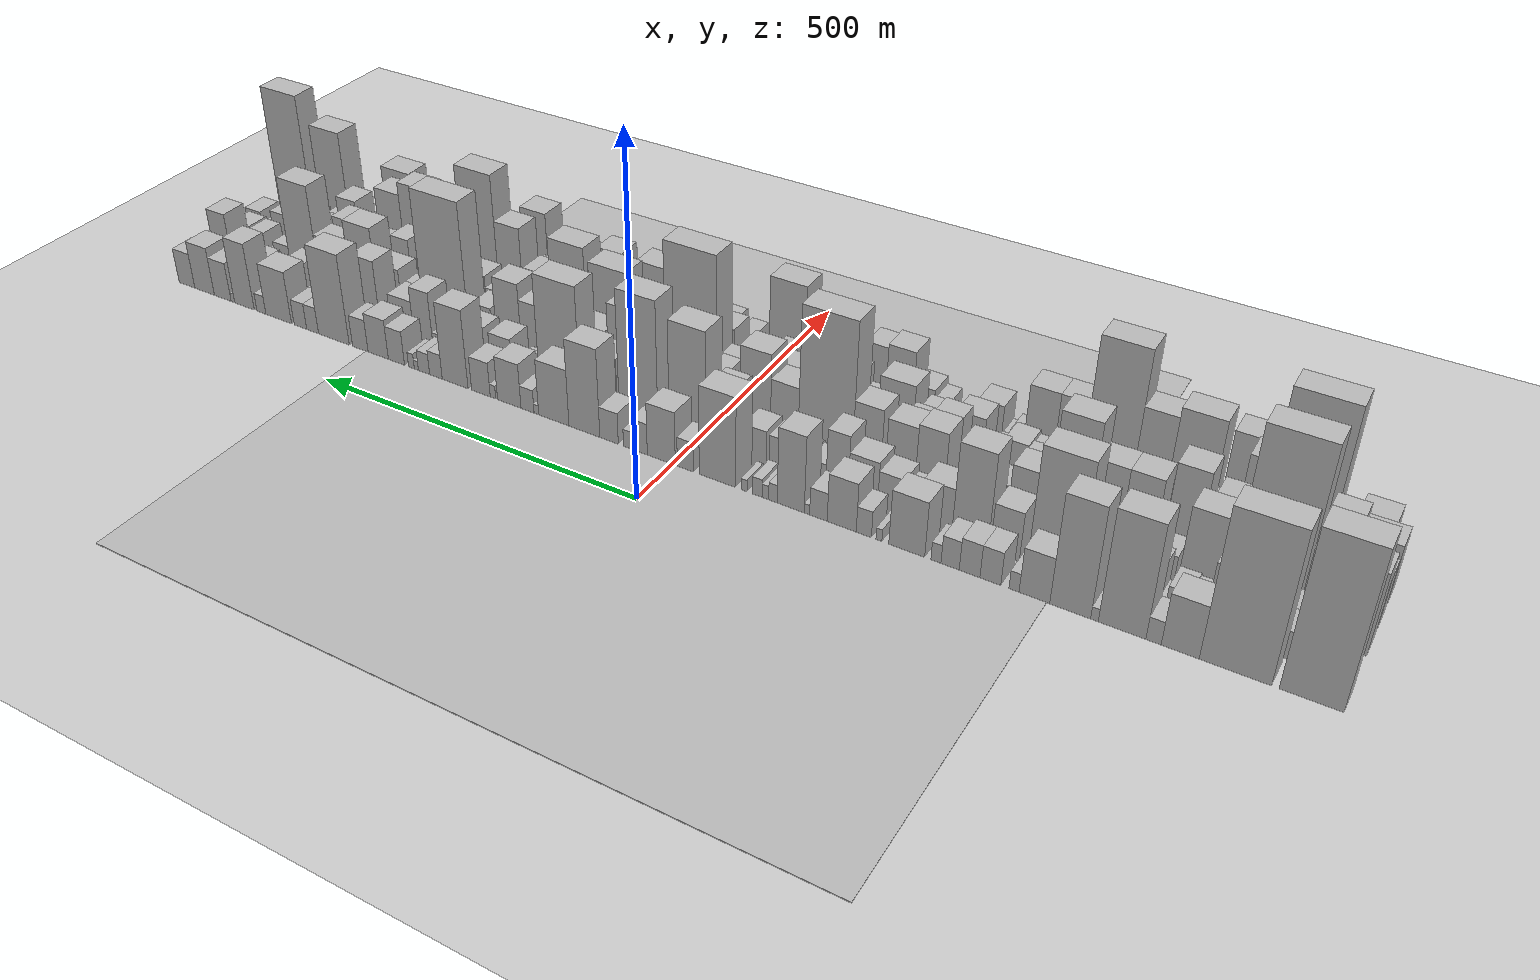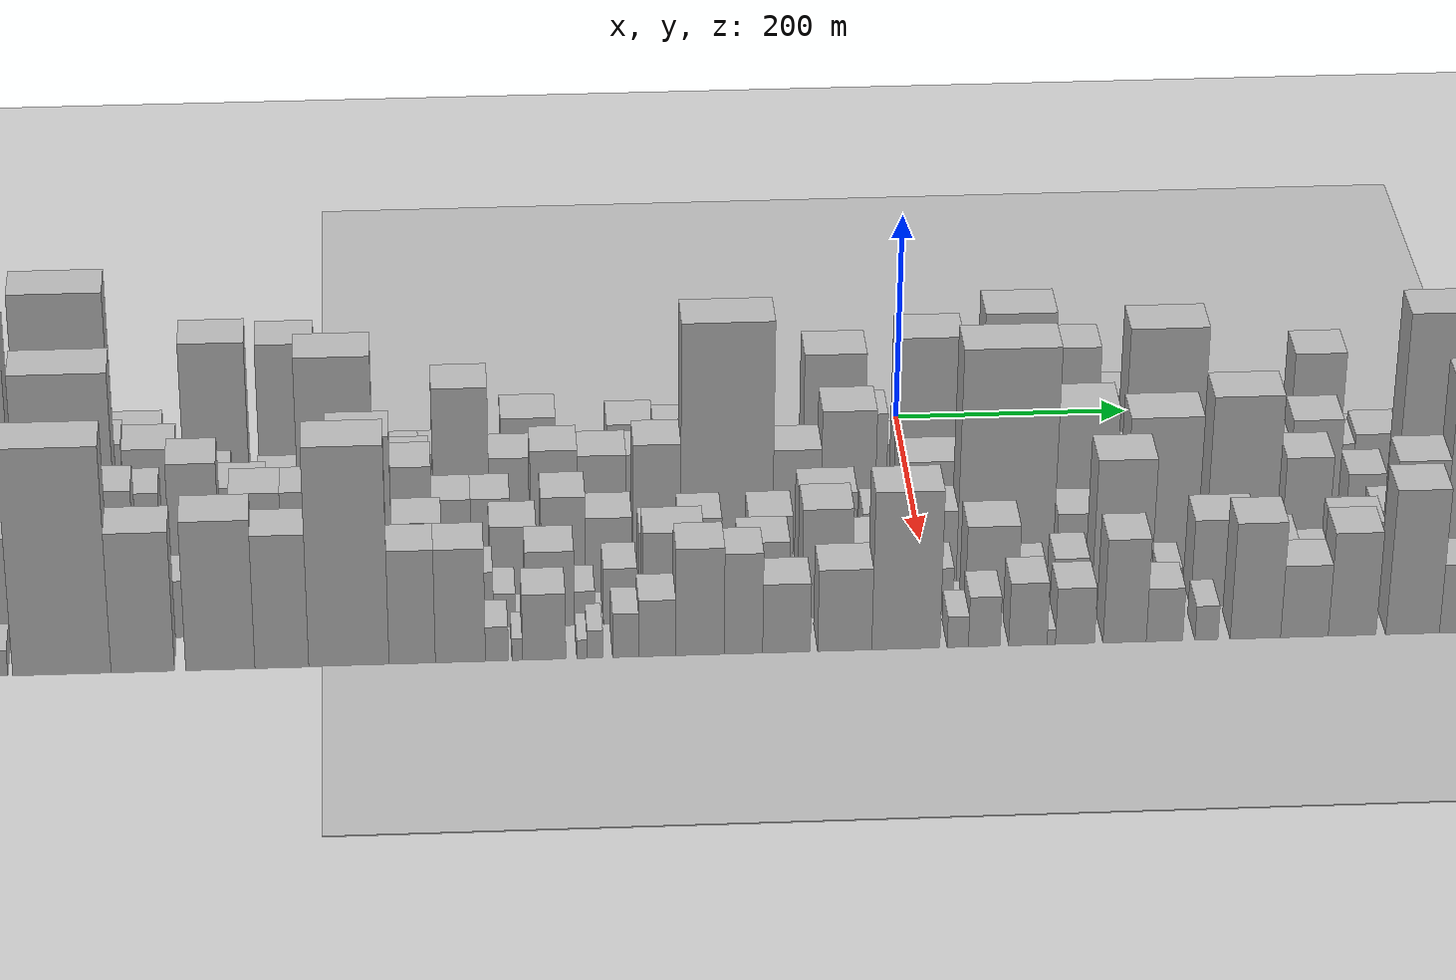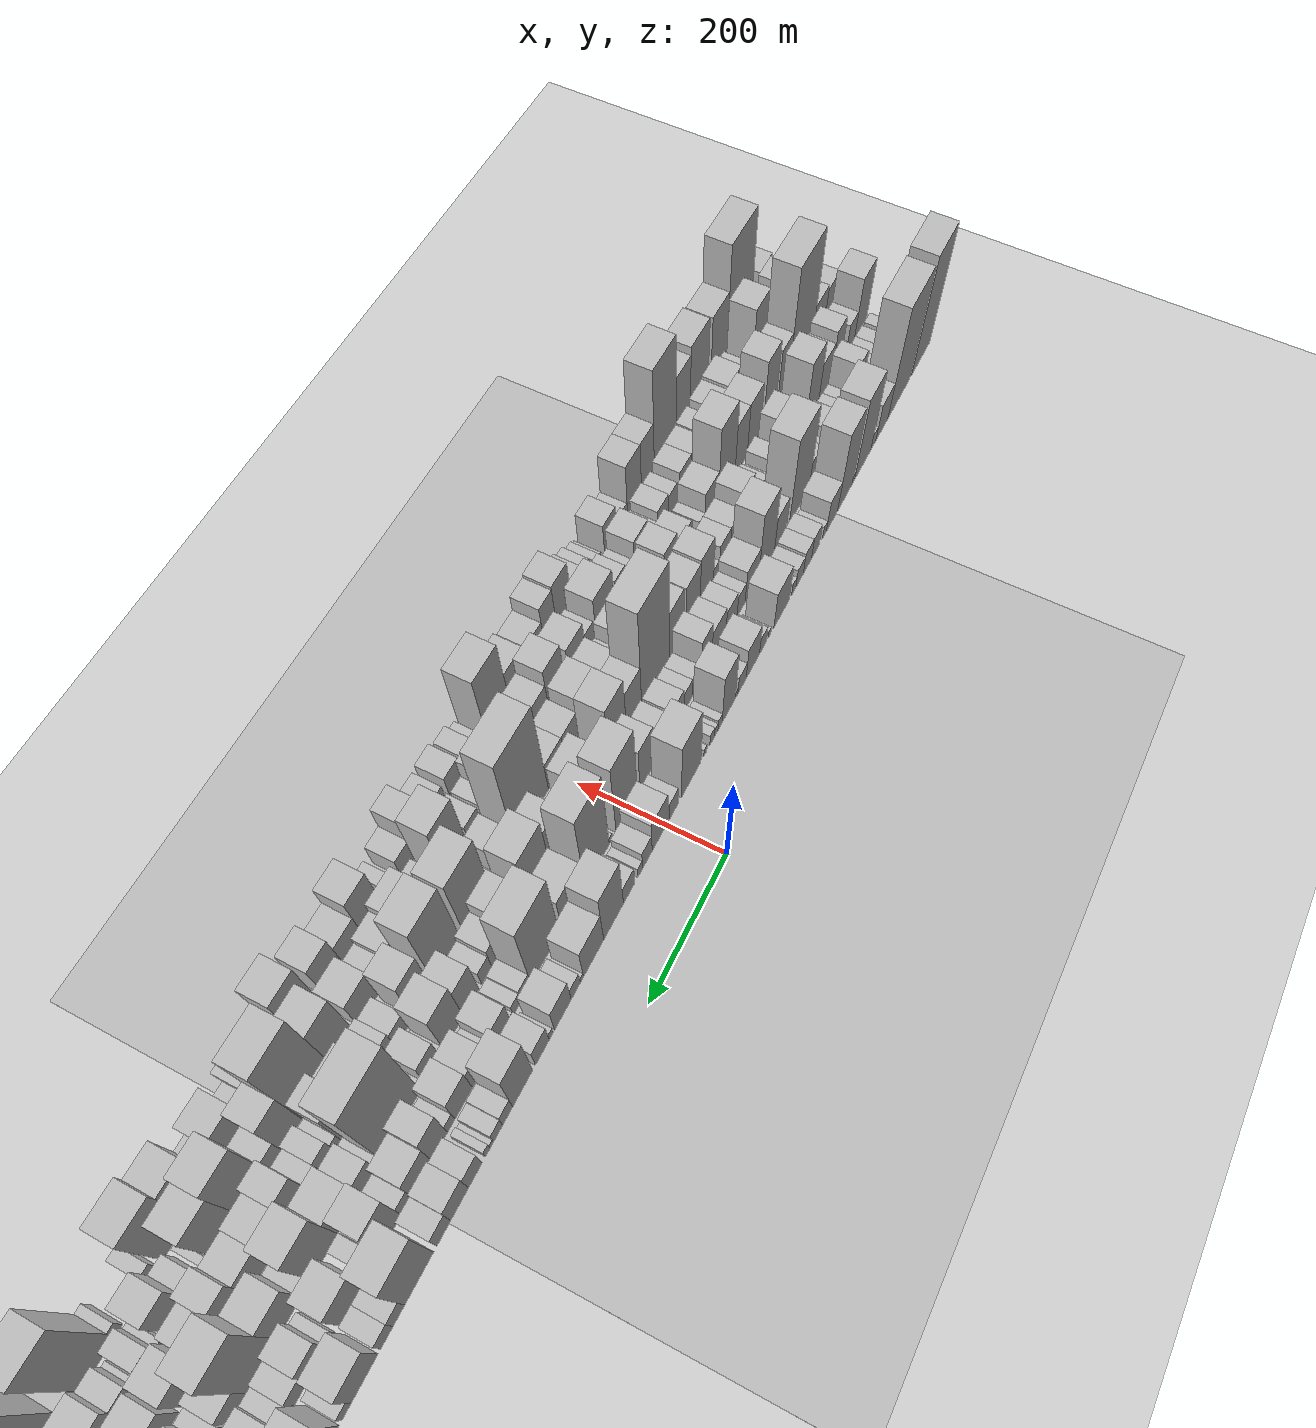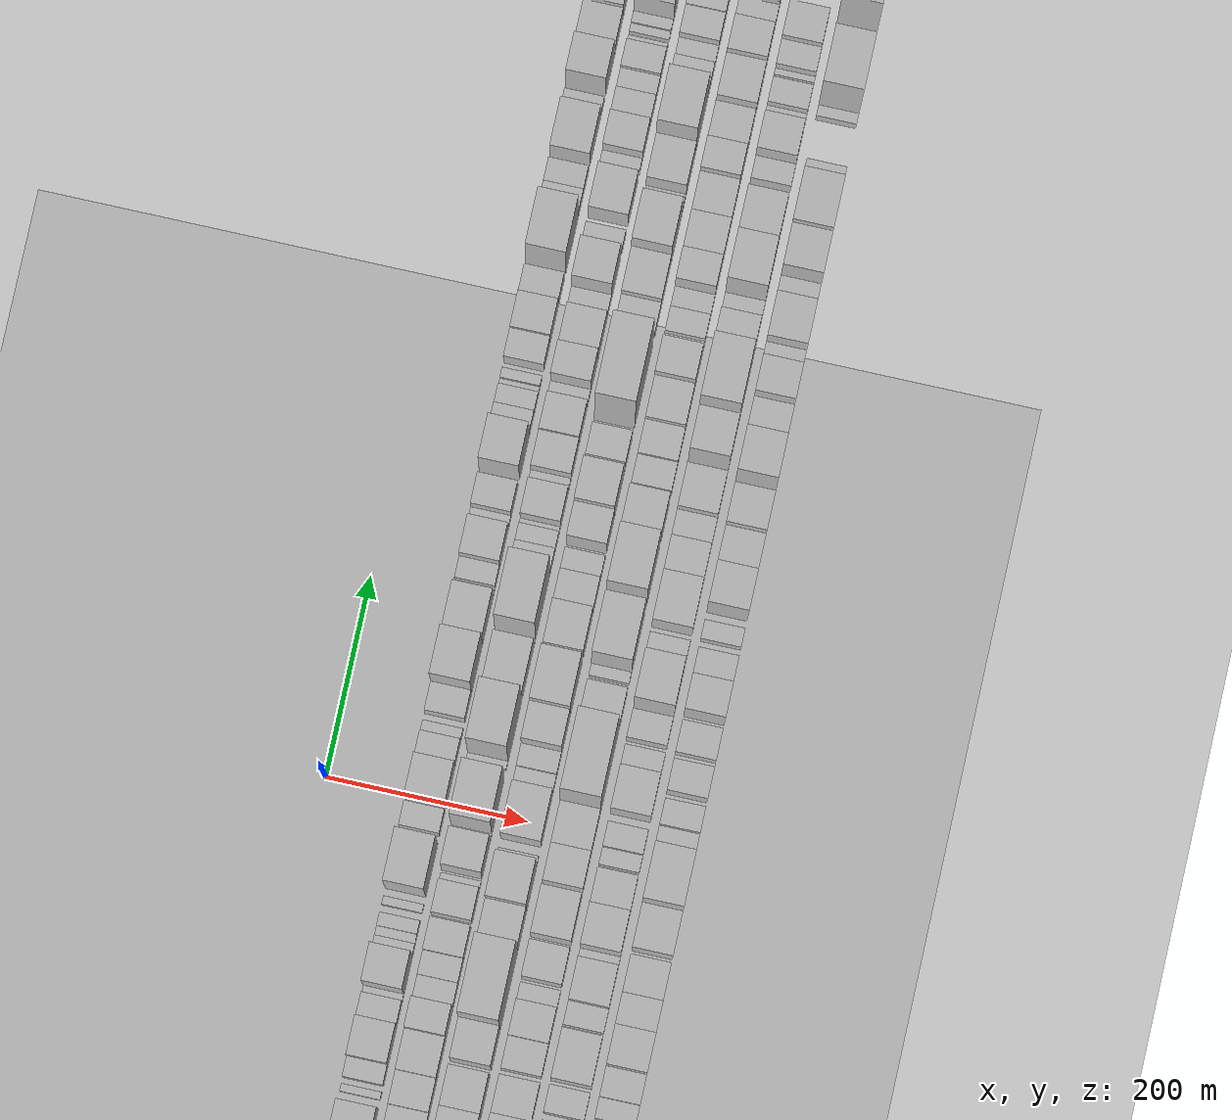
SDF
<?xml version="1.0" encoding="utf-8"?>

<sdf version="1.6">

   <world name="default">

      <gui fullscreen="0">

         <camera name="user_camera">

            <pose>-15 0 4.57585 0 0 0</pose>

            <view_controller>orbit</view_controller>

         </camera>

      </gui>

      <scene>

         <sky>

           <clouds>

             <speed>12</speed>

           </clouds>

         </sky>

         <ambient>0.4 0.4 0.4 1</ambient>

         <background>0.7 0.7 0.7 1</background>

         <shadows>1</shadows>

      </scene>

      <gravity>0 0 -9.8066</gravity>

      <magnetic_field>6e-06 2.3e-05 -4.2e-05</magnetic_field>

      <physics default="0" name="default_physics" type="ode">

         <ode>

            <solver>

               <type>quick</type>

               <iters>10</iters>

               <sor>1.0</sor>

               <use_dynamic_moi_rescaling>0</use_dynamic_moi_rescaling>

            </solver>

            <constraints>

               <cfm>0</cfm>

               <erp>0.2</erp>

               <contact_max_correcting_vel>100</contact_max_correcting_vel>

               <contact_surface_layer>0.001</contact_surface_layer>

            </constraints>

         </ode>

         <max_step_size>0.004</max_step_size>

         <real_time_factor>1</real_time_factor>

         <real_time_update_rate>250</real_time_update_rate>

      </physics>

      <light name="sun" type="directional">

         <cast_shadows>1</cast_shadows>

         <pose>0 0 10 0 0 0</pose>

         <diffuse>0.8 0.8 0.8 1</diffuse>

         <specular>0.2 0.2 0.2 1</specular>

         <attenuation>

            <range>1000</range>

            <constant>0.9</constant>

            <linear>0.01</linear>

            <quadratic>0.001</quadratic>

         </attenuation>

         <direction>-0.5 0.1 -0.9</direction>

      </light>

      <include>

         <name>ground_plane_1</name>

         <uri>model://HANNAS_ground_plane</uri>

         <pose>0 0 0  0 0 0</pose>

      </include>

      <include>

         <name>ground_plane_2</name>

         <uri>model://HANNAS_ground_plane</uri>

         <pose>100 0 0  0 0 0</pose>

      </include>

      <model name="building_1">

         <static>1</static>

         <pose frame="">100.0000 -796.0572 0 0.000000 0.000000 0.000000</pose>

         <link name="link">

            <pose frame="">0 0 111.00 0 0 0</pose>

            <collision name="collision">

               <geometry>

                  <box>

                     <size>40.0000 67.8856 222.0000</size>

                  </box>

               </geometry>

               <max_contacts>10</max_contacts>

               <surface>

                  <contact>

                     <ode/>

                  </contact>

                  <bounce/>

                  <friction>

                     <torsional>

                        <ode/>

                     </torsional>

                     <ode/>

                  </friction>

               </surface>

            </collision>

            <visual name="visual">

               <cast_shadows>0</cast_shadows>

               <geometry>

                  <box>

                     <size>40.0000 67.8856 222.0000</size>

                  </box>

               </geometry>

               <material>

                  <script>

                     <uri>model://HANNAS_wall/materials/scripts</uri>

                     <uri>model://HANNAS_wall/materials/textures</uri>

                     <name>vrc/HANNAS_wall</name>

                  </script>

               </material>

            </visual>

            <self_collide>0</self_collide>

            <enable_wind>0</enable_wind>

            <kinematic>0</kinematic>

         </link>

      </model>

      <model name="building_2">

         <static>1</static>

         <pose frame="">100.0000 -714.7521 0 0.000000 0.000000 0.000000</pose>

         <link name="link">

            <pose frame="">0 0 106.50 0 0 0</pose>

            <collision name="collision">

               <geometry>

                  <box>

                     <size>40.0000 78.7246 213.0000</size>

                  </box>

               </geometry>

               <max_contacts>10</max_contacts>

               <surface>

                  <contact>

                     <ode/>

                  </contact>

                  <bounce/>

                  <friction>

                     <torsional>

                        <ode/>

                     </torsional>

                     <ode/>

                  </friction>

               </surface>

            </collision>

            <visual name="visual">

               <cast_shadows>0</cast_shadows>

               <geometry>

                  <box>

                     <size>40.0000 78.7246 213.0000</size>

                  </box>

               </geometry>

               <material>

                  <script>

                     <uri>model://HANNAS_wall/materials/scripts</uri>

                     <uri>model://HANNAS_wall/materials/textures</uri>

                     <name>vrc/HANNAS_wall</name>

                  </script>

               </material>

            </visual>

            <self_collide>0</self_collide>

            <enable_wind>0</enable_wind>

            <kinematic>0</kinematic>

         </link>

      </model>

      <model name="building_3">

         <static>1</static>

         <pose frame="">100.0000 -654.1740 0 0.000000 0.000000 0.000000</pose>

         <link name="link">

            <pose frame="">0 0 37.50 0 0 0</pose>

            <collision name="collision">

               <geometry>

                  <box>

                     <size>40.0000 42.4316 75.0000</size>

                  </box>

               </geometry>

               <max_contacts>10</max_contacts>

               <surface>

                  <contact>

                     <ode/>

                  </contact>

                  <bounce/>

                  <friction>

                     <torsional>

                        <ode/>

                     </torsional>

                     <ode/>

                  </friction>

               </surface>

            </collision>

            <visual name="visual">

               <cast_shadows>0</cast_shadows>

               <geometry>

                  <box>

                     <size>40.0000 42.4316 75.0000</size>

                  </box>

               </geometry>

               <material>

                  <script>

                     <uri>model://HANNAS_wall/materials/scripts</uri>

                     <uri>model://HANNAS_wall/materials/textures</uri>

                     <name>vrc/HANNAS_wall</name>

                  </script>

               </material>

            </visual>

            <self_collide>0</self_collide>

            <enable_wind>0</enable_wind>

            <kinematic>0</kinematic>

         </link>

      </model>

      <model name="building_4">

         <static>1</static>

         <pose frame="">100.0000 -624.2647 0 0.000000 0.000000 0.000000</pose>

         <link name="link">

            <pose frame="">0 0 16.50 0 0 0</pose>

            <collision name="collision">

               <geometry>

                  <box>

                     <size>40.0000 17.3870 33.0000</size>

                  </box>

               </geometry>

               <max_contacts>10</max_contacts>

               <surface>

                  <contact>

                     <ode/>

                  </contact>

                  <bounce/>

                  <friction>

                     <torsional>

                        <ode/>

                     </torsional>

                     <ode/>

                  </friction>

               </surface>

            </collision>

            <visual name="visual">

               <cast_shadows>0</cast_shadows>

               <geometry>

                  <box>

                     <size>40.0000 17.3870 33.0000</size>

                  </box>

               </geometry>

               <material>

                  <script>

                     <uri>model://HANNAS_wall/materials/scripts</uri>

                     <uri>model://HANNAS_wall/materials/textures</uri>

                     <name>vrc/HANNAS_wall</name>

                  </script>

               </material>

            </visual>

            <self_collide>0</self_collide>

            <enable_wind>0</enable_wind>

            <kinematic>0</kinematic>

         </link>

      </model>

      <model name="building_5">

         <static>1</static>

         <pose frame="">100.0000 -588.1427 0 0.000000 0.000000 0.000000</pose>

         <link name="link">

            <pose frame="">0 0 81.00 0 0 0</pose>

            <collision name="collision">

               <geometry>

                  <box>

                     <size>40.0000 54.8569 162.0000</size>

                  </box>

               </geometry>

               <max_contacts>10</max_contacts>

               <surface>

                  <contact>

                     <ode/>

                  </contact>

                  <bounce/>

                  <friction>

                     <torsional>

                        <ode/>

                     </torsional>

                     <ode/>

                  </friction>

               </surface>

            </collision>

            <visual name="visual">

               <cast_shadows>0</cast_shadows>

               <geometry>

                  <box>

                     <size>40.0000 54.8569 162.0000</size>

                  </box>

               </geometry>

               <material>

                  <script>

                     <uri>model://HANNAS_wall/materials/scripts</uri>

                     <uri>model://HANNAS_wall/materials/textures</uri>

                     <name>vrc/HANNAS_wall</name>

                  </script>

               </material>

            </visual>

            <self_collide>0</self_collide>

            <enable_wind>0</enable_wind>

            <kinematic>0</kinematic>

         </link>

      </model>

      <model name="building_6">

         <static>1</static>

         <pose frame="">100.0000 -556.2341 0 0.000000 0.000000 0.000000</pose>

         <link name="link">

            <pose frame="">0 0 9.00 0 0 0</pose>

            <collision name="collision">

               <geometry>

                  <box>

                     <size>40.0000 8.9603 18.0000</size>

                  </box>

               </geometry>

               <max_contacts>10</max_contacts>

               <surface>

                  <contact>

                     <ode/>

                  </contact>

                  <bounce/>

                  <friction>

                     <torsional>

                        <ode/>

                     </torsional>

                     <ode/>

                  </friction>

               </surface>

            </collision>

            <visual name="visual">

               <cast_shadows>0</cast_shadows>

               <geometry>

                  <box>

                     <size>40.0000 8.9603 18.0000</size>

                  </box>

               </geometry>

               <material>

                  <script>

                     <uri>model://HANNAS_wall/materials/scripts</uri>

                     <uri>model://HANNAS_wall/materials/textures</uri>

                     <name>vrc/HANNAS_wall</name>

                  </script>

               </material>

            </visual>

            <self_collide>0</self_collide>

            <enable_wind>0</enable_wind>

            <kinematic>0</kinematic>

         </link>

      </model>

      <model name="building_7">

         <static>1</static>

         <pose frame="">100.0000 -527.5284 0 0.000000 0.000000 0.000000</pose>

         <link name="link">

            <pose frame="">0 0 79.50 0 0 0</pose>

            <collision name="collision">

               <geometry>

                  <box>

                     <size>40.0000 48.4513 159.0000</size>

                  </box>

               </geometry>

               <max_contacts>10</max_contacts>

               <surface>

                  <contact>

                     <ode/>

                  </contact>

                  <bounce/>

                  <friction>

                     <torsional>

                        <ode/>

                     </torsional>

                     <ode/>

                  </friction>

               </surface>

            </collision>

            <visual name="visual">

               <cast_shadows>0</cast_shadows>

               <geometry>

                  <box>

                     <size>40.0000 48.4513 159.0000</size>

                  </box>

               </geometry>

               <material>

                  <script>

                     <uri>model://HANNAS_wall/materials/scripts</uri>

                     <uri>model://HANNAS_wall/materials/textures</uri>

                     <name>vrc/HANNAS_wall</name>

                  </script>

               </material>

            </visual>

            <self_collide>0</self_collide>

            <enable_wind>0</enable_wind>

            <kinematic>0</kinematic>

         </link>

      </model>

      <model name="building_8">

         <static>1</static>

         <pose frame="">100.0000 -484.7975 0 0.000000 0.000000 0.000000</pose>

         <link name="link">

            <pose frame="">0 0 33.00 0 0 0</pose>

            <collision name="collision">

               <geometry>

                  <box>

                     <size>40.0000 37.0104 66.0000</size>

                  </box>

               </geometry>

               <max_contacts>10</max_contacts>

               <surface>

                  <contact>

                     <ode/>

                  </contact>

                  <bounce/>

                  <friction>

                     <torsional>

                        <ode/>

                     </torsional>

                     <ode/>

                  </friction>

               </surface>

            </collision>

            <visual name="visual">

               <cast_shadows>0</cast_shadows>

               <geometry>

                  <box>

                     <size>40.0000 37.0104 66.0000</size>

                  </box>

               </geometry>

               <material>

                  <script>

                     <uri>model://HANNAS_wall/materials/scripts</uri>

                     <uri>model://HANNAS_wall/materials/textures</uri>

                     <name>vrc/HANNAS_wall</name>

                  </script>

               </material>

            </visual>

            <self_collide>0</self_collide>

            <enable_wind>0</enable_wind>

            <kinematic>0</kinematic>

         </link>

      </model>

      <model name="building_9">

         <static>1</static>

         <pose frame="">100.0000 -460.1134 0 0.000000 0.000000 0.000000</pose>

         <link name="link">

            <pose frame="">0 0 13.50 0 0 0</pose>

            <collision name="collision">

               <geometry>

                  <box>

                     <size>40.0000 12.3579 27.0000</size>

                  </box>

               </geometry>

               <max_contacts>10</max_contacts>

               <surface>

                  <contact>

                     <ode/>

                  </contact>

                  <bounce/>

                  <friction>

                     <torsional>

                        <ode/>

                     </torsional>

                     <ode/>

                  </friction>

               </surface>

            </collision>

            <visual name="visual">

               <cast_shadows>0</cast_shadows>

               <geometry>

                  <box>

                     <size>40.0000 12.3579 27.0000</size>

                  </box>

               </geometry>

               <material>

                  <script>

                     <uri>model://HANNAS_wall/materials/scripts</uri>

                     <uri>model://HANNAS_wall/materials/textures</uri>

                     <name>vrc/HANNAS_wall</name>

                  </script>

               </material>

            </visual>

            <self_collide>0</self_collide>

            <enable_wind>0</enable_wind>

            <kinematic>0</kinematic>

         </link>

      </model>

      <model name="building_10">

         <static>1</static>

         <pose frame="">100.0000 -431.0310 0 0.000000 0.000000 0.000000</pose>

         <link name="link">

            <pose frame="">0 0 24.00 0 0 0</pose>

            <collision name="collision">

               <geometry>

                  <box>

                     <size>40.0000 25.8069 48.0000</size>

                  </box>

               </geometry>

               <max_contacts>10</max_contacts>

               <surface>

                  <contact>

                     <ode/>

                  </contact>

                  <bounce/>

                  <friction>

                     <torsional>

                        <ode/>

                     </torsional>

                     <ode/>

                  </friction>

               </surface>

            </collision>

            <visual name="visual">

               <cast_shadows>0</cast_shadows>

               <geometry>

                  <box>

                     <size>40.0000 25.8069 48.0000</size>

                  </box>

               </geometry>

               <material>

                  <script>

                     <uri>model://HANNAS_wall/materials/scripts</uri>

                     <uri>model://HANNAS_wall/materials/textures</uri>

                     <name>vrc/HANNAS_wall</name>

                  </script>

               </material>

            </visual>

            <self_collide>0</self_collide>

            <enable_wind>0</enable_wind>

            <kinematic>0</kinematic>

         </link>

      </model>

      <model name="building_11">

         <static>1</static>

         <pose frame="">100.0000 -405.2154 0 0.000000 0.000000 0.000000</pose>

         <link name="link">

            <pose frame="">0 0 24.00 0 0 0</pose>

            <collision name="collision">

               <geometry>

                  <box>

                     <size>40.0000 25.8243 48.0000</size>

                  </box>

               </geometry>

               <max_contacts>10</max_contacts>

               <surface>

                  <contact>

                     <ode/>

                  </contact>

                  <bounce/>

                  <friction>

                     <torsional>

                        <ode/>

                     </torsional>

                     <ode/>

                  </friction>

               </surface>

            </collision>

            <visual name="visual">

               <cast_shadows>0</cast_shadows>

               <geometry>

                  <box>

                     <size>40.0000 25.8243 48.0000</size>

                  </box>

               </geometry>

               <material>

                  <script>

                     <uri>model://HANNAS_wall/materials/scripts</uri>

                     <uri>model://HANNAS_wall/materials/textures</uri>

                     <name>vrc/HANNAS_wall</name>

                  </script>

               </material>

            </visual>

            <self_collide>0</self_collide>

            <enable_wind>0</enable_wind>

            <kinematic>0</kinematic>

         </link>

      </model>

      <model name="building_12">

         <static>1</static>

         <pose frame="">100.0000 -380.7069 0 0.000000 0.000000 0.000000</pose>

         <link name="link">

            <pose frame="">0 0 21.00 0 0 0</pose>

            <collision name="collision">

               <geometry>

                  <box>

                     <size>40.0000 23.1926 42.0000</size>

                  </box>

               </geometry>

               <max_contacts>10</max_contacts>

               <surface>

                  <contact>

                     <ode/>

                  </contact>

                  <bounce/>

                  <friction>

                     <torsional>

                        <ode/>

                     </torsional>

                     <ode/>

                  </friction>

               </surface>

            </collision>

            <visual name="visual">

               <cast_shadows>0</cast_shadows>

               <geometry>

                  <box>

                     <size>40.0000 23.1926 42.0000</size>

                  </box>

               </geometry>

               <material>

                  <script>

                     <uri>model://HANNAS_wall/materials/scripts</uri>

                     <uri>model://HANNAS_wall/materials/textures</uri>

                     <name>vrc/HANNAS_wall</name>

                  </script>

               </material>

            </visual>

            <self_collide>0</self_collide>

            <enable_wind>0</enable_wind>

            <kinematic>0</kinematic>

         </link>

      </model>

      <model name="building_13">

         <static>1</static>

         <pose frame="">100.0000 -362.7196 0 0.000000 0.000000 0.000000</pose>

         <link name="link">

            <pose frame="">0 0 13.50 0 0 0</pose>

            <collision name="collision">

               <geometry>

                  <box>

                     <size>40.0000 12.7820 27.0000</size>

                  </box>

               </geometry>

               <max_contacts>10</max_contacts>

               <surface>

                  <contact>

                     <ode/>

                  </contact>

                  <bounce/>

                  <friction>

                     <torsional>

                        <ode/>

                     </torsional>

                     <ode/>

                  </friction>

               </surface>

            </collision>

            <visual name="visual">

               <cast_shadows>0</cast_shadows>

               <geometry>

                  <box>

                     <size>40.0000 12.7820 27.0000</size>

                  </box>

               </geometry>

               <material>

                  <script>

                     <uri>model://HANNAS_wall/materials/scripts</uri>

                     <uri>model://HANNAS_wall/materials/textures</uri>

                     <name>vrc/HANNAS_wall</name>

                  </script>

               </material>

            </visual>

            <self_collide>0</self_collide>

            <enable_wind>0</enable_wind>

            <kinematic>0</kinematic>

         </link>

      </model>

      <model name="building_14">

         <static>1</static>

         <pose frame="">100.0000 -325.0952 0 0.000000 0.000000 0.000000</pose>

         <link name="link">

            <pose frame="">0 0 40.50 0 0 0</pose>

            <collision name="collision">

               <geometry>

                  <box>

                     <size>40.0000 46.4668 81.0000</size>

                  </box>

               </geometry>

               <max_contacts>10</max_contacts>

               <surface>

                  <contact>

                     <ode/>

                  </contact>

                  <bounce/>

                  <friction>

                     <torsional>

                        <ode/>

                     </torsional>

                     <ode/>

                  </friction>

               </surface>

            </collision>

            <visual name="visual">

               <cast_shadows>0</cast_shadows>

               <geometry>

                  <box>

                     <size>40.0000 46.4668 81.0000</size>

                  </box>

               </geometry>

               <material>

                  <script>

                     <uri>model://HANNAS_wall/materials/scripts</uri>

                     <uri>model://HANNAS_wall/materials/textures</uri>

                     <name>vrc/HANNAS_wall</name>

                  </script>

               </material>

            </visual>

            <self_collide>0</self_collide>

            <enable_wind>0</enable_wind>

            <kinematic>0</kinematic>

         </link>

      </model>

      <model name="building_15">

         <static>1</static>

         <pose frame="">100.0000 -288.9566 0 0.000000 0.000000 0.000000</pose>

         <link name="link">

            <pose frame="">0 0 9.00 0 0 0</pose>

            <collision name="collision">

               <geometry>

                  <box>

                     <size>40.0000 7.8104 18.0000</size>

                  </box>

               </geometry>

               <max_contacts>10</max_contacts>

               <surface>

                  <contact>

                     <ode/>

                  </contact>

                  <bounce/>

                  <friction>

                     <torsional>

                        <ode/>

                     </torsional>

                     <ode/>

                  </friction>

               </surface>

            </collision>

            <visual name="visual">

               <cast_shadows>0</cast_shadows>

               <geometry>

                  <box>

                     <size>40.0000 7.8104 18.0000</size>

                  </box>

               </geometry>

               <material>

                  <script>

                     <uri>model://HANNAS_wall/materials/scripts</uri>

                     <uri>model://HANNAS_wall/materials/textures</uri>

                     <name>vrc/HANNAS_wall</name>

                  </script>

               </material>

            </visual>

            <self_collide>0</self_collide>

            <enable_wind>0</enable_wind>

            <kinematic>0</kinematic>

         </link>

      </model>

      <model name="building_16">

         <static>1</static>

         <pose frame="">100.0000 -268.9484 0 0.000000 0.000000 0.000000</pose>

         <link name="link">

            <pose frame="">0 0 19.50 0 0 0</pose>

            <collision name="collision">

               <geometry>

                  <box>

                     <size>40.0000 20.2061 39.0000</size>

                  </box>

               </geometry>

               <max_contacts>10</max_contacts>

               <surface>

                  <contact>

                     <ode/>

                  </contact>

                  <bounce/>

                  <friction>

                     <torsional>

                        <ode/>

                     </torsional>

                     <ode/>

                  </friction>

               </surface>

            </collision>

            <visual name="visual">

               <cast_shadows>0</cast_shadows>

               <geometry>

                  <box>

                     <size>40.0000 20.2061 39.0000</size>

                  </box>

               </geometry>

               <material>

                  <script>

                     <uri>model://HANNAS_wall/materials/scripts</uri>

                     <uri>model://HANNAS_wall/materials/textures</uri>

                     <name>vrc/HANNAS_wall</name>

                  </script>

               </material>

            </visual>

            <self_collide>0</self_collide>

            <enable_wind>0</enable_wind>

            <kinematic>0</kinematic>

         </link>

      </model>

      <model name="building_17">

         <static>1</static>

         <pose frame="">100.0000 -239.3086 0 0.000000 0.000000 0.000000</pose>

         <link name="link">

            <pose frame="">0 0 36.00 0 0 0</pose>

            <collision name="collision">

               <geometry>

                  <box>

                     <size>40.0000 39.0734 72.0000</size>

                  </box>

               </geometry>

               <max_contacts>10</max_contacts>

               <surface>

                  <contact>

                     <ode/>

                  </contact>

                  <bounce/>

                  <friction>

                     <torsional>

                        <ode/>

                     </torsional>

                     <ode/>

                  </friction>

               </surface>

            </collision>

            <visual name="visual">

               <cast_shadows>0</cast_shadows>

               <geometry>

                  <box>

                     <size>40.0000 39.0734 72.0000</size>

                  </box>

               </geometry>

               <material>

                  <script>

                     <uri>model://HANNAS_wall/materials/scripts</uri>

                     <uri>model://HANNAS_wall/materials/textures</uri>

                     <name>vrc/HANNAS_wall</name>

                  </script>

               </material>

            </visual>

            <self_collide>0</self_collide>

            <enable_wind>0</enable_wind>

            <kinematic>0</kinematic>

         </link>

      </model>

      <model name="building_18">

         <static>1</static>

         <pose frame="">100.0000 -207.8517 0 0.000000 0.000000 0.000000</pose>

         <link name="link">

            <pose frame="">0 0 21.00 0 0 0</pose>

            <collision name="collision">

               <geometry>

                  <box>

                     <size>40.0000 23.8405 42.0000</size>

                  </box>

               </geometry>

               <max_contacts>10</max_contacts>

               <surface>

                  <contact>

                     <ode/>

                  </contact>

                  <bounce/>

                  <friction>

                     <torsional>

                        <ode/>

                     </torsional>

                     <ode/>

                  </friction>

               </surface>

            </collision>

            <visual name="visual">

               <cast_shadows>0</cast_shadows>

               <geometry>

                  <box>

                     <size>40.0000 23.8405 42.0000</size>

                  </box>

               </geometry>

               <material>

                  <script>

                     <uri>model://HANNAS_wall/materials/scripts</uri>

                     <uri>model://HANNAS_wall/materials/textures</uri>

                     <name>vrc/HANNAS_wall</name>

                  </script>

               </material>

            </visual>

            <self_collide>0</self_collide>

            <enable_wind>0</enable_wind>

            <kinematic>0</kinematic>

         </link>

      </model>

      <model name="building_19">

         <static>1</static>

         <pose frame="">100.0000 -192.2362 0 0.000000 0.000000 0.000000</pose>

         <link name="link">

            <pose frame="">0 0 7.50 0 0 0</pose>

            <collision name="collision">

               <geometry>

                  <box>

                     <size>40.0000 7.3903 15.0000</size>

                  </box>

               </geometry>

               <max_contacts>10</max_contacts>

               <surface>

                  <contact>

                     <ode/>

                  </contact>

                  <bounce/>

                  <friction>

                     <torsional>

                        <ode/>

                     </torsional>

                     <ode/>

                  </friction>

               </surface>

            </collision>

            <visual name="visual">

               <cast_shadows>0</cast_shadows>

               <geometry>

                  <box>

                     <size>40.0000 7.3903 15.0000</size>

                  </box>

               </geometry>

               <material>

                  <script>

                     <uri>model://HANNAS_wall/materials/scripts</uri>

                     <uri>model://HANNAS_wall/materials/textures</uri>

                     <name>vrc/HANNAS_wall</name>

                  </script>

               </material>

            </visual>

            <self_collide>0</self_collide>

            <enable_wind>0</enable_wind>

            <kinematic>0</kinematic>

         </link>

      </model>

      <model name="building_20">

         <static>1</static>

         <pose frame="">100.0000 -169.7350 0 0.000000 0.000000 0.000000</pose>

         <link name="link">

            <pose frame="">0 0 57.00 0 0 0</pose>

            <collision name="collision">

               <geometry>

                  <box>

                     <size>40.0000 37.6122 114.0000</size>

                  </box>

               </geometry>

               <max_contacts>10</max_contacts>

               <surface>

                  <contact>

                     <ode/>

                  </contact>

                  <bounce/>

                  <friction>

                     <torsional>

                        <ode/>

                     </torsional>

                     <ode/>

                  </friction>

               </surface>

            </collision>

            <visual name="visual">

               <cast_shadows>0</cast_shadows>

               <geometry>

                  <box>

                     <size>40.0000 37.6122 114.0000</size>

                  </box>

               </geometry>

               <material>

                  <script>

                     <uri>model://HANNAS_wall/materials/scripts</uri>

                     <uri>model://HANNAS_wall/materials/textures</uri>

                     <name>vrc/HANNAS_wall</name>

                  </script>

               </material>

            </visual>

            <self_collide>0</self_collide>

            <enable_wind>0</enable_wind>

            <kinematic>0</kinematic>

         </link>

      </model>

      <model name="building_21">

         <static>1</static>

         <pose frame="">100.0000 -145.0932 0 0.000000 0.000000 0.000000</pose>

         <link name="link">

            <pose frame="">0 0 13.50 0 0 0</pose>

            <collision name="collision">

               <geometry>

                  <box>

                     <size>40.0000 11.6714 27.0000</size>

                  </box>

               </geometry>

               <max_contacts>10</max_contacts>

               <surface>

                  <contact>

                     <ode/>

                  </contact>

                  <bounce/>

                  <friction>

                     <torsional>

                        <ode/>

                     </torsional>

                     <ode/>

                  </friction>

               </surface>

            </collision>

            <visual name="visual">

               <cast_shadows>0</cast_shadows>

               <geometry>

                  <box>

                     <size>40.0000 11.6714 27.0000</size>

                  </box>

               </geometry>

               <material>

                  <script>

                     <uri>model://HANNAS_wall/materials/scripts</uri>

                     <uri>model://HANNAS_wall/materials/textures</uri>

                     <name>vrc/HANNAS_wall</name>

                  </script>

               </material>

            </visual>

            <self_collide>0</self_collide>

            <enable_wind>0</enable_wind>

            <kinematic>0</kinematic>

         </link>

      </model>

      <model name="building_22">

         <static>1</static>

         <pose frame="">100.0000 -134.6083 0 0.000000 0.000000 0.000000</pose>

         <link name="link">

            <pose frame="">0 0 10.50 0 0 0</pose>

            <collision name="collision">

               <geometry>

                  <box>

                     <size>40.0000 9.2983 21.0000</size>

                  </box>

               </geometry>

               <max_contacts>10</max_contacts>

               <surface>

                  <contact>

                     <ode/>

                  </contact>

                  <bounce/>

                  <friction>

                     <torsional>

                        <ode/>

                     </torsional>

                     <ode/>

                  </friction>

               </surface>

            </collision>

            <visual name="visual">

               <cast_shadows>0</cast_shadows>

               <geometry>

                  <box>

                     <size>40.0000 9.2983 21.0000</size>

                  </box>

               </geometry>

               <material>

                  <script>

                     <uri>model://HANNAS_wall/materials/scripts</uri>

                     <uri>model://HANNAS_wall/materials/textures</uri>

                     <name>vrc/HANNAS_wall</name>

                  </script>

               </material>

            </visual>

            <self_collide>0</self_collide>

            <enable_wind>0</enable_wind>

            <kinematic>0</kinematic>

         </link>

      </model>

      <model name="building_23">

         <static>1</static>

         <pose frame="">100.0000 -123.3137 0 0.000000 0.000000 0.000000</pose>

         <link name="link">

            <pose frame="">0 0 13.50 0 0 0</pose>

            <collision name="collision">

               <geometry>

                  <box>

                     <size>40.0000 13.2908 27.0000</size>

                  </box>

               </geometry>

               <max_contacts>10</max_contacts>

               <surface>

                  <contact>

                     <ode/>

                  </contact>

                  <bounce/>

                  <friction>

                     <torsional>

                        <ode/>

                     </torsional>

                     <ode/>

                  </friction>

               </surface>

            </collision>

            <visual name="visual">

               <cast_shadows>0</cast_shadows>

               <geometry>

                  <box>

                     <size>40.0000 13.2908 27.0000</size>

                  </box>

               </geometry>

               <material>

                  <script>

                     <uri>model://HANNAS_wall/materials/scripts</uri>

                     <uri>model://HANNAS_wall/materials/textures</uri>

                     <name>vrc/HANNAS_wall</name>

                  </script>

               </material>

            </visual>

            <self_collide>0</self_collide>

            <enable_wind>0</enable_wind>

            <kinematic>0</kinematic>

         </link>

      </model>

      <model name="building_24">

         <static>1</static>

         <pose frame="">100.0000 -104.4396 0 0.000000 0.000000 0.000000</pose>

         <link name="link">

            <pose frame="">0 0 9.00 0 0 0</pose>

            <collision name="collision">

               <geometry>

                  <box>

                     <size>40.0000 8.4573 18.0000</size>

                  </box>

               </geometry>

               <max_contacts>10</max_contacts>

               <surface>

                  <contact>

                     <ode/>

                  </contact>

                  <bounce/>

                  <friction>

                     <torsional>

                        <ode/>

                     </torsional>

                     <ode/>

                  </friction>

               </surface>

            </collision>

            <visual name="visual">

               <cast_shadows>0</cast_shadows>

               <geometry>

                  <box>

                     <size>40.0000 8.4573 18.0000</size>

                  </box>

               </geometry>

               <material>

                  <script>

                     <uri>model://HANNAS_wall/materials/scripts</uri>

                     <uri>model://HANNAS_wall/materials/textures</uri>

                     <name>vrc/HANNAS_wall</name>

                  </script>

               </material>

            </visual>

            <self_collide>0</self_collide>

            <enable_wind>0</enable_wind>

            <kinematic>0</kinematic>

         </link>

      </model>

      <model name="building_25">

         <static>1</static>

         <pose frame="">100.0000 -66.0082 0 0.000000 0.000000 0.000000</pose>

         <link name="link">

            <pose frame="">0 0 67.50 0 0 0</pose>

            <collision name="collision">

               <geometry>

                  <box>

                     <size>40.0000 52.4056 135.0000</size>

                  </box>

               </geometry>

               <max_contacts>10</max_contacts>

               <surface>

                  <contact>

                     <ode/>

                  </contact>

                  <bounce/>

                  <friction>

                     <torsional>

                        <ode/>

                     </torsional>

                     <ode/>

                  </friction>

               </surface>

            </collision>

            <visual name="visual">

               <cast_shadows>0</cast_shadows>

               <geometry>

                  <box>

                     <size>40.0000 52.4056 135.0000</size>

                  </box>

               </geometry>

               <material>

                  <script>

                     <uri>model://HANNAS_wall/materials/scripts</uri>

                     <uri>model://HANNAS_wall/materials/textures</uri>

                     <name>vrc/HANNAS_wall</name>

                  </script>

               </material>

            </visual>

            <self_collide>0</self_collide>

            <enable_wind>0</enable_wind>

            <kinematic>0</kinematic>

         </link>

      </model>

      <model name="building_26">

         <static>1</static>

         <pose frame="">100.0000 -19.6957 0 0.000000 0.000000 0.000000</pose>

         <link name="link">

            <pose frame="">0 0 22.50 0 0 0</pose>

            <collision name="collision">

               <geometry>

                  <box>

                     <size>40.0000 24.2194 45.0000</size>

                  </box>

               </geometry>

               <max_contacts>10</max_contacts>

               <surface>

                  <contact>

                     <ode/>

                  </contact>

                  <bounce/>

                  <friction>

                     <torsional>

                        <ode/>

                     </torsional>

                     <ode/>

                  </friction>

               </surface>

            </collision>

            <visual name="visual">

               <cast_shadows>0</cast_shadows>

               <geometry>

                  <box>

                     <size>40.0000 24.2194 45.0000</size>

                  </box>

               </geometry>

               <material>

                  <script>

                     <uri>model://HANNAS_wall/materials/scripts</uri>

                     <uri>model://HANNAS_wall/materials/textures</uri>

                     <name>vrc/HANNAS_wall</name>

                  </script>

               </material>

            </visual>

            <self_collide>0</self_collide>

            <enable_wind>0</enable_wind>

            <kinematic>0</kinematic>

         </link>

      </model>

      <model name="building_27">

         <static>1</static>

         <pose frame="">100.0000 16.2949 0 0.000000 0.000000 0.000000</pose>

         <link name="link">

            <pose frame="">0 0 40.50 0 0 0</pose>

            <collision name="collision">

               <geometry>

                  <box>

                     <size>40.0000 41.7618 81.0000</size>

                  </box>

               </geometry>

               <max_contacts>10</max_contacts>

               <surface>

                  <contact>

                     <ode/>

                  </contact>

                  <bounce/>

                  <friction>

                     <torsional>

                        <ode/>

                     </torsional>

                     <ode/>

                  </friction>

               </surface>

            </collision>

            <visual name="visual">

               <cast_shadows>0</cast_shadows>

               <geometry>

                  <box>

                     <size>40.0000 41.7618 81.0000</size>

                  </box>

               </geometry>

               <material>

                  <script>

                     <uri>model://HANNAS_wall/materials/scripts</uri>

                     <uri>model://HANNAS_wall/materials/textures</uri>

                     <name>vrc/HANNAS_wall</name>

                  </script>

               </material>

            </visual>

            <self_collide>0</self_collide>

            <enable_wind>0</enable_wind>

            <kinematic>0</kinematic>

         </link>

      </model>

      <model name="building_28">

         <static>1</static>

         <pose frame="">100.0000 49.4250 0 0.000000 0.000000 0.000000</pose>

         <link name="link">

            <pose frame="">0 0 24.00 0 0 0</pose>

            <collision name="collision">

               <geometry>

                  <box>

                     <size>40.0000 24.4985 48.0000</size>

                  </box>

               </geometry>

               <max_contacts>10</max_contacts>

               <surface>

                  <contact>

                     <ode/>

                  </contact>

                  <bounce/>

                  <friction>

                     <torsional>

                        <ode/>

                     </torsional>

                     <ode/>

                  </friction>

               </surface>

            </collision>

            <visual name="visual">

               <cast_shadows>0</cast_shadows>

               <geometry>

                  <box>

                     <size>40.0000 24.4985 48.0000</size>

                  </box>

               </geometry>

               <material>

                  <script>

                     <uri>model://HANNAS_wall/materials/scripts</uri>

                     <uri>model://HANNAS_wall/materials/textures</uri>

                     <name>vrc/HANNAS_wall</name>

                  </script>

               </material>

            </visual>

            <self_collide>0</self_collide>

            <enable_wind>0</enable_wind>

            <kinematic>0</kinematic>

         </link>

      </model>

      <model name="building_29">

         <static>1</static>

         <pose frame="">100.0000 67.4773 0 0.000000 0.000000 0.000000</pose>

         <link name="link">

            <pose frame="">0 0 13.50 0 0 0</pose>

            <collision name="collision">

               <geometry>

                  <box>

                     <size>40.0000 11.6061 27.0000</size>

                  </box>

               </geometry>

               <max_contacts>10</max_contacts>

               <surface>

                  <contact>

                     <ode/>

                  </contact>

                  <bounce/>

                  <friction>

                     <torsional>

                        <ode/>

                     </torsional>

                     <ode/>

                  </friction>

               </surface>

            </collision>

            <visual name="visual">

               <cast_shadows>0</cast_shadows>

               <geometry>

                  <box>

                     <size>40.0000 11.6061 27.0000</size>

                  </box>

               </geometry>

               <material>

                  <script>

                     <uri>model://HANNAS_wall/materials/scripts</uri>

                     <uri>model://HANNAS_wall/materials/textures</uri>

                     <name>vrc/HANNAS_wall</name>

                  </script>

               </material>

            </visual>

            <self_collide>0</self_collide>

            <enable_wind>0</enable_wind>

            <kinematic>0</kinematic>

         </link>

      </model>

      <model name="building_30">

         <static>1</static>

         <pose frame="">100.0000 95.4846 0 0.000000 0.000000 0.000000</pose>

         <link name="link">

            <pose frame="">0 0 24.00 0 0 0</pose>

            <collision name="collision">

               <geometry>

                  <box>

                     <size>40.0000 28.4085 48.0000</size>

                  </box>

               </geometry>

               <max_contacts>10</max_contacts>

               <surface>

                  <contact>

                     <ode/>

                  </contact>

                  <bounce/>

                  <friction>

                     <torsional>

                        <ode/>

                     </torsional>

                     <ode/>

                  </friction>

               </surface>

            </collision>

            <visual name="visual">

               <cast_shadows>0</cast_shadows>

               <geometry>

                  <box>

                     <size>40.0000 28.4085 48.0000</size>

                  </box>

               </geometry>

               <material>

                  <script>

                     <uri>model://HANNAS_wall/materials/scripts</uri>

                     <uri>model://HANNAS_wall/materials/textures</uri>

                     <name>vrc/HANNAS_wall</name>

                  </script>

               </material>

            </visual>

            <self_collide>0</self_collide>

            <enable_wind>0</enable_wind>

            <kinematic>0</kinematic>

         </link>

      </model>

      <model name="building_31">

         <static>1</static>

         <pose frame="">100.0000 133.8912 0 0.000000 0.000000 0.000000</pose>

         <link name="link">

            <pose frame="">0 0 67.50 0 0 0</pose>

            <collision name="collision">

               <geometry>

                  <box>

                     <size>40.0000 48.4046 135.0000</size>

                  </box>

               </geometry>

               <max_contacts>10</max_contacts>

               <surface>

                  <contact>

                     <ode/>

                  </contact>

                  <bounce/>

                  <friction>

                     <torsional>

                        <ode/>

                     </torsional>

                     <ode/>

                  </friction>

               </surface>

            </collision>

            <visual name="visual">

               <cast_shadows>0</cast_shadows>

               <geometry>

                  <box>

                     <size>40.0000 48.4046 135.0000</size>

                  </box>

               </geometry>

               <material>

                  <script>

                     <uri>model://HANNAS_wall/materials/scripts</uri>

                     <uri>model://HANNAS_wall/materials/textures</uri>

                     <name>vrc/HANNAS_wall</name>

                  </script>

               </material>

            </visual>

            <self_collide>0</self_collide>

            <enable_wind>0</enable_wind>

            <kinematic>0</kinematic>

         </link>

      </model>

      <model name="building_32">

         <static>1</static>

         <pose frame="">100.0000 182.2587 0 0.000000 0.000000 0.000000</pose>

         <link name="link">

            <pose frame="">0 0 43.50 0 0 0</pose>

            <collision name="collision">

               <geometry>

                  <box>

                     <size>40.0000 48.3305 87.0000</size>

                  </box>

               </geometry>

               <max_contacts>10</max_contacts>

               <surface>

                  <contact>

                     <ode/>

                  </contact>

                  <bounce/>

                  <friction>

                     <torsional>

                        <ode/>

                     </torsional>

                     <ode/>

                  </friction>

               </surface>

            </collision>

            <visual name="visual">

               <cast_shadows>0</cast_shadows>

               <geometry>

                  <box>

                     <size>40.0000 48.3305 87.0000</size>

                  </box>

               </geometry>

               <material>

                  <script>

                     <uri>model://HANNAS_wall/materials/scripts</uri>

                     <uri>model://HANNAS_wall/materials/textures</uri>

                     <name>vrc/HANNAS_wall</name>

                  </script>

               </material>

            </visual>

            <self_collide>0</self_collide>

            <enable_wind>0</enable_wind>

            <kinematic>0</kinematic>

         </link>

      </model>

      <model name="building_33">

         <static>1</static>

         <pose frame="">100.0000 210.1511 0 0.000000 0.000000 0.000000</pose>

         <link name="link">

            <pose frame="">0 0 7.50 0 0 0</pose>

            <collision name="collision">

               <geometry>

                  <box>

                     <size>40.0000 7.4541 15.0000</size>

                  </box>

               </geometry>

               <max_contacts>10</max_contacts>

               <surface>

                  <contact>

                     <ode/>

                  </contact>

                  <bounce/>

                  <friction>

                     <torsional>

                        <ode/>

                     </torsional>

                     <ode/>

                  </friction>

               </surface>

            </collision>

            <visual name="visual">

               <cast_shadows>0</cast_shadows>

               <geometry>

                  <box>

                     <size>40.0000 7.4541 15.0000</size>

                  </box>

               </geometry>

               <material>

                  <script>

                     <uri>model://HANNAS_wall/materials/scripts</uri>

                     <uri>model://HANNAS_wall/materials/textures</uri>

                     <name>vrc/HANNAS_wall</name>

                  </script>

               </material>

            </visual>

            <self_collide>0</self_collide>

            <enable_wind>0</enable_wind>

            <kinematic>0</kinematic>

         </link>

      </model>

      <model name="building_34">

         <static>1</static>

         <pose frame="">100.0000 224.5080 0 0.000000 0.000000 0.000000</pose>

         <link name="link">

            <pose frame="">0 0 18.00 0 0 0</pose>

            <collision name="collision">

               <geometry>

                  <box>

                     <size>40.0000 21.2596 36.0000</size>

                  </box>

               </geometry>

               <max_contacts>10</max_contacts>

               <surface>

                  <contact>

                     <ode/>

                  </contact>

                  <bounce/>

                  <friction>

                     <torsional>

                        <ode/>

                     </torsional>

                     <ode/>

                  </friction>

               </surface>

            </collision>

            <visual name="visual">

               <cast_shadows>0</cast_shadows>

               <geometry>

                  <box>

                     <size>40.0000 21.2596 36.0000</size>

                  </box>

               </geometry>

               <material>

                  <script>

                     <uri>model://HANNAS_wall/materials/scripts</uri>

                     <uri>model://HANNAS_wall/materials/textures</uri>

                     <name>vrc/HANNAS_wall</name>

                  </script>

               </material>

            </visual>

            <self_collide>0</self_collide>

            <enable_wind>0</enable_wind>

            <kinematic>0</kinematic>

         </link>

      </model>

      <model name="building_35">

         <static>1</static>

         <pose frame="">100.0000 254.3415 0 0.000000 0.000000 0.000000</pose>

         <link name="link">

            <pose frame="">0 0 34.50 0 0 0</pose>

            <collision name="collision">

               <geometry>

                  <box>

                     <size>40.0000 38.4075 69.0000</size>

                  </box>

               </geometry>

               <max_contacts>10</max_contacts>

               <surface>

                  <contact>

                     <ode/>

                  </contact>

                  <bounce/>

                  <friction>

                     <torsional>

                        <ode/>

                     </torsional>

                     <ode/>

                  </friction>

               </surface>

            </collision>

            <visual name="visual">

               <cast_shadows>0</cast_shadows>

               <geometry>

                  <box>

                     <size>40.0000 38.4075 69.0000</size>

                  </box>

               </geometry>

               <material>

                  <script>

                     <uri>model://HANNAS_wall/materials/scripts</uri>

                     <uri>model://HANNAS_wall/materials/textures</uri>

                     <name>vrc/HANNAS_wall</name>

                  </script>

               </material>

            </visual>

            <self_collide>0</self_collide>

            <enable_wind>0</enable_wind>

            <kinematic>0</kinematic>

         </link>

      </model>

      <model name="building_36">

         <static>1</static>

         <pose frame="">100.0000 281.0811 0 0.000000 0.000000 0.000000</pose>

         <link name="link">

            <pose frame="">0 0 10.50 0 0 0</pose>

            <collision name="collision">

               <geometry>

                  <box>

                     <size>40.0000 9.0717 21.0000</size>

                  </box>

               </geometry>

               <max_contacts>10</max_contacts>

               <surface>

                  <contact>

                     <ode/>

                  </contact>

                  <bounce/>

                  <friction>

                     <torsional>

                        <ode/>

                     </torsional>

                     <ode/>

                  </friction>

               </surface>

            </collision>

            <visual name="visual">

               <cast_shadows>0</cast_shadows>

               <geometry>

                  <box>

                     <size>40.0000 9.0717 21.0000</size>

                  </box>

               </geometry>

               <material>

                  <script>

                     <uri>model://HANNAS_wall/materials/scripts</uri>

                     <uri>model://HANNAS_wall/materials/textures</uri>

                     <name>vrc/HANNAS_wall</name>

                  </script>

               </material>

            </visual>

            <self_collide>0</self_collide>

            <enable_wind>0</enable_wind>

            <kinematic>0</kinematic>

         </link>

      </model>

      <model name="building_37">

         <static>1</static>

         <pose frame="">100.0000 301.2184 0 0.000000 0.000000 0.000000</pose>

         <link name="link">

            <pose frame="">0 0 27.00 0 0 0</pose>

            <collision name="collision">

               <geometry>

                  <box>

                     <size>40.0000 31.2029 54.0000</size>

                  </box>

               </geometry>

               <max_contacts>10</max_contacts>

               <surface>

                  <contact>

                     <ode/>

                  </contact>

                  <bounce/>

                  <friction>

                     <torsional>

                        <ode/>

                     </torsional>

                     <ode/>

                  </friction>

               </surface>

            </collision>

            <visual name="visual">

               <cast_shadows>0</cast_shadows>

               <geometry>

                  <box>

                     <size>40.0000 31.2029 54.0000</size>

                  </box>

               </geometry>

               <material>

                  <script>

                     <uri>model://HANNAS_wall/materials/scripts</uri>

                     <uri>model://HANNAS_wall/materials/textures</uri>

                     <name>vrc/HANNAS_wall</name>

                  </script>

               </material>

            </visual>

            <self_collide>0</self_collide>

            <enable_wind>0</enable_wind>

            <kinematic>0</kinematic>

         </link>

      </model>

      <model name="building_38">

         <static>1</static>

         <pose frame="">100.0000 344.7618 0 0.000000 0.000000 0.000000</pose>

         <link name="link">

            <pose frame="">0 0 61.50 0 0 0</pose>

            <collision name="collision">

               <geometry>

                  <box>

                     <size>40.0000 43.8839 123.0000</size>

                  </box>

               </geometry>

               <max_contacts>10</max_contacts>

               <surface>

                  <contact>

                     <ode/>

                  </contact>

                  <bounce/>

                  <friction>

                     <torsional>

                        <ode/>

                     </torsional>

                     <ode/>

                  </friction>

               </surface>

            </collision>

            <visual name="visual">

               <cast_shadows>0</cast_shadows>

               <geometry>

                  <box>

                     <size>40.0000 43.8839 123.0000</size>

                  </box>

               </geometry>

               <material>

                  <script>

                     <uri>model://HANNAS_wall/materials/scripts</uri>

                     <uri>model://HANNAS_wall/materials/textures</uri>

                     <name>vrc/HANNAS_wall</name>

                  </script>

               </material>

            </visual>

            <self_collide>0</self_collide>

            <enable_wind>0</enable_wind>

            <kinematic>0</kinematic>

         </link>

      </model>

      <model name="building_39">

         <static>1</static>

         <pose frame="">100.0000 377.5432 0 0.000000 0.000000 0.000000</pose>

         <link name="link">

            <pose frame="">0 0 19.50 0 0 0</pose>

            <collision name="collision">

               <geometry>

                  <box>

                     <size>40.0000 21.6790 39.0000</size>

                  </box>

               </geometry>

               <max_contacts>10</max_contacts>

               <surface>

                  <contact>

                     <ode/>

                  </contact>

                  <bounce/>

                  <friction>

                     <torsional>

                        <ode/>

                     </torsional>

                     <ode/>

                  </friction>

               </surface>

            </collision>

            <visual name="visual">

               <cast_shadows>0</cast_shadows>

               <geometry>

                  <box>

                     <size>40.0000 21.6790 39.0000</size>

                  </box>

               </geometry>

               <material>

                  <script>

                     <uri>model://HANNAS_wall/materials/scripts</uri>

                     <uri>model://HANNAS_wall/materials/textures</uri>

                     <name>vrc/HANNAS_wall</name>

                  </script>

               </material>

            </visual>

            <self_collide>0</self_collide>

            <enable_wind>0</enable_wind>

            <kinematic>0</kinematic>

         </link>

      </model>

      <model name="building_40">

         <static>1</static>

         <pose frame="">100.0000 398.1407 0 0.000000 0.000000 0.000000</pose>

         <link name="link">

            <pose frame="">0 0 16.50 0 0 0</pose>

            <collision name="collision">

               <geometry>

                  <box>

                     <size>40.0000 19.5160 33.0000</size>

                  </box>

               </geometry>

               <max_contacts>10</max_contacts>

               <surface>

                  <contact>

                     <ode/>

                  </contact>

                  <bounce/>

                  <friction>

                     <torsional>

                        <ode/>

                     </torsional>

                     <ode/>

                  </friction>

               </surface>

            </collision>

            <visual name="visual">

               <cast_shadows>0</cast_shadows>

               <geometry>

                  <box>

                     <size>40.0000 19.5160 33.0000</size>

                  </box>

               </geometry>

               <material>

                  <script>

                     <uri>model://HANNAS_wall/materials/scripts</uri>

                     <uri>model://HANNAS_wall/materials/textures</uri>

                     <name>vrc/HANNAS_wall</name>

                  </script>

               </material>

            </visual>

            <self_collide>0</self_collide>

            <enable_wind>0</enable_wind>

            <kinematic>0</kinematic>

         </link>

      </model>

      <model name="building_41">

         <static>1</static>

         <pose frame="">100.0000 411.3787 0 0.000000 0.000000 0.000000</pose>

         <link name="link">

            <pose frame="">0 0 7.50 0 0 0</pose>

            <collision name="collision">

               <geometry>

                  <box>

                     <size>40.0000 6.9599 15.0000</size>

                  </box>

               </geometry>

               <max_contacts>10</max_contacts>

               <surface>

                  <contact>

                     <ode/>

                  </contact>

                  <bounce/>

                  <friction>

                     <torsional>

                        <ode/>

                     </torsional>

                     <ode/>

                  </friction>

               </surface>

            </collision>

            <visual name="visual">

               <cast_shadows>0</cast_shadows>

               <geometry>

                  <box>

                     <size>40.0000 6.9599 15.0000</size>

                  </box>

               </geometry>

               <material>

                  <script>

                     <uri>model://HANNAS_wall/materials/scripts</uri>

                     <uri>model://HANNAS_wall/materials/textures</uri>

                     <name>vrc/HANNAS_wall</name>

                  </script>

               </material>

            </visual>

            <self_collide>0</self_collide>

            <enable_wind>0</enable_wind>

            <kinematic>0</kinematic>

         </link>

      </model>

      <model name="building_42">

         <static>1</static>

         <pose frame="">100.0000 419.9391 0 0.000000 0.000000 0.000000</pose>

         <link name="link">

            <pose frame="">0 0 12.00 0 0 0</pose>

            <collision name="collision">

               <geometry>

                  <box>

                     <size>40.0000 10.1609 24.0000</size>

                  </box>

               </geometry>

               <max_contacts>10</max_contacts>

               <surface>

                  <contact>

                     <ode/>

                  </contact>

                  <bounce/>

                  <friction>

                     <torsional>

                        <ode/>

                     </torsional>

                     <ode/>

                  </friction>

               </surface>

            </collision>

            <visual name="visual">

               <cast_shadows>0</cast_shadows>

               <geometry>

                  <box>

                     <size>40.0000 10.1609 24.0000</size>

                  </box>

               </geometry>

               <material>

                  <script>

                     <uri>model://HANNAS_wall/materials/scripts</uri>

                     <uri>model://HANNAS_wall/materials/textures</uri>

                     <name>vrc/HANNAS_wall</name>

                  </script>

               </material>

            </visual>

            <self_collide>0</self_collide>

            <enable_wind>0</enable_wind>

            <kinematic>0</kinematic>

         </link>

      </model>

      <model name="building_43">

         <static>1</static>

         <pose frame="">100.0000 446.2726 0 0.000000 0.000000 0.000000</pose>

         <link name="link">

            <pose frame="">0 0 27.00 0 0 0</pose>

            <collision name="collision">

               <geometry>

                  <box>

                     <size>40.0000 28.5061 54.0000</size>

                  </box>

               </geometry>

               <max_contacts>10</max_contacts>

               <surface>

                  <contact>

                     <ode/>

                  </contact>

                  <bounce/>

                  <friction>

                     <torsional>

                        <ode/>

                     </torsional>

                     <ode/>

                  </friction>

               </surface>

            </collision>

            <visual name="visual">

               <cast_shadows>0</cast_shadows>

               <geometry>

                  <box>

                     <size>40.0000 28.5061 54.0000</size>

                  </box>

               </geometry>

               <material>

                  <script>

                     <uri>model://HANNAS_wall/materials/scripts</uri>

                     <uri>model://HANNAS_wall/materials/textures</uri>

                     <name>vrc/HANNAS_wall</name>

                  </script>

               </material>

            </visual>

            <self_collide>0</self_collide>

            <enable_wind>0</enable_wind>

            <kinematic>0</kinematic>

         </link>

      </model>

      <model name="building_44">

         <static>1</static>

         <pose frame="">100.0000 478.7097 0 0.000000 0.000000 0.000000</pose>

         <link name="link">

            <pose frame="">0 0 31.50 0 0 0</pose>

            <collision name="collision">

               <geometry>

                  <box>

                     <size>40.0000 36.3681 63.0000</size>

                  </box>

               </geometry>

               <max_contacts>10</max_contacts>

               <surface>

                  <contact>

                     <ode/>

                  </contact>

                  <bounce/>

                  <friction>

                     <torsional>

                        <ode/>

                     </torsional>

                     <ode/>

                  </friction>

               </surface>

            </collision>

            <visual name="visual">

               <cast_shadows>0</cast_shadows>

               <geometry>

                  <box>

                     <size>40.0000 36.3681 63.0000</size>

                  </box>

               </geometry>

               <material>

                  <script>

                     <uri>model://HANNAS_wall/materials/scripts</uri>

                     <uri>model://HANNAS_wall/materials/textures</uri>

                     <name>vrc/HANNAS_wall</name>

                  </script>

               </material>

            </visual>

            <self_collide>0</self_collide>

            <enable_wind>0</enable_wind>

            <kinematic>0</kinematic>

         </link>

      </model>

      <model name="building_45">

         <static>1</static>

         <pose frame="">100.0000 510.9054 0 0.000000 0.000000 0.000000</pose>

         <link name="link">

            <pose frame="">0 0 25.50 0 0 0</pose>

            <collision name="collision">

               <geometry>

                  <box>

                     <size>40.0000 28.0233 51.0000</size>

                  </box>

               </geometry>

               <max_contacts>10</max_contacts>

               <surface>

                  <contact>

                     <ode/>

                  </contact>

                  <bounce/>

                  <friction>

                     <torsional>

                        <ode/>

                     </torsional>

                     <ode/>

                  </friction>

               </surface>

            </collision>

            <visual name="visual">

               <cast_shadows>0</cast_shadows>

               <geometry>

                  <box>

                     <size>40.0000 28.0233 51.0000</size>

                  </box>

               </geometry>

               <material>

                  <script>

                     <uri>model://HANNAS_wall/materials/scripts</uri>

                     <uri>model://HANNAS_wall/materials/textures</uri>

                     <name>vrc/HANNAS_wall</name>

                  </script>

               </material>

            </visual>

            <self_collide>0</self_collide>

            <enable_wind>0</enable_wind>

            <kinematic>0</kinematic>

         </link>

      </model>

      <model name="building_46">

         <static>1</static>

         <pose frame="">100.0000 559.2429 0 0.000000 0.000000 0.000000</pose>

         <link name="link">

            <pose frame="">0 0 72.00 0 0 0</pose>

            <collision name="collision">

               <geometry>

                  <box>

                     <size>40.0000 56.6516 144.0000</size>

                  </box>

               </geometry>

               <max_contacts>10</max_contacts>

               <surface>

                  <contact>

                     <ode/>

                  </contact>

                  <bounce/>

                  <friction>

                     <torsional>

                        <ode/>

                     </torsional>

                     <ode/>

                  </friction>

               </surface>

            </collision>

            <visual name="visual">

               <cast_shadows>0</cast_shadows>

               <geometry>

                  <box>

                     <size>40.0000 56.6516 144.0000</size>

                  </box>

               </geometry>

               <material>

                  <script>

                     <uri>model://HANNAS_wall/materials/scripts</uri>

                     <uri>model://HANNAS_wall/materials/textures</uri>

                     <name>vrc/HANNAS_wall</name>

                  </script>

               </material>

            </visual>

            <self_collide>0</self_collide>

            <enable_wind>0</enable_wind>

            <kinematic>0</kinematic>

         </link>

      </model>

      <model name="building_47">

         <static>1</static>

         <pose frame="">100.0000 598.6686 0 0.000000 0.000000 0.000000</pose>

         <link name="link">

            <pose frame="">0 0 21.00 0 0 0</pose>

            <collision name="collision">

               <geometry>

                  <box>

                     <size>40.0000 22.1999 42.0000</size>

                  </box>

               </geometry>

               <max_contacts>10</max_contacts>

               <surface>

                  <contact>

                     <ode/>

                  </contact>

                  <bounce/>

                  <friction>

                     <torsional>

                        <ode/>

                     </torsional>

                     <ode/>

                  </friction>

               </surface>

            </collision>

            <visual name="visual">

               <cast_shadows>0</cast_shadows>

               <geometry>

                  <box>

                     <size>40.0000 22.1999 42.0000</size>

                  </box>

               </geometry>

               <material>

                  <script>

                     <uri>model://HANNAS_wall/materials/scripts</uri>

                     <uri>model://HANNAS_wall/materials/textures</uri>

                     <name>vrc/HANNAS_wall</name>

                  </script>

               </material>

            </visual>

            <self_collide>0</self_collide>

            <enable_wind>0</enable_wind>

            <kinematic>0</kinematic>

         </link>

      </model>

      <model name="building_48">

         <static>1</static>

         <pose frame="">100.0000 621.4675 0 0.000000 0.000000 0.000000</pose>

         <link name="link">

            <pose frame="">0 0 21.00 0 0 0</pose>

            <collision name="collision">

               <geometry>

                  <box>

                     <size>40.0000 23.3979 42.0000</size>

                  </box>

               </geometry>

               <max_contacts>10</max_contacts>

               <surface>

                  <contact>

                     <ode/>

                  </contact>

                  <bounce/>

                  <friction>

                     <torsional>

                        <ode/>

                     </torsional>

                     <ode/>

                  </friction>

               </surface>

            </collision>

            <visual name="visual">

               <cast_shadows>0</cast_shadows>

               <geometry>

                  <box>

                     <size>40.0000 23.3979 42.0000</size>

                  </box>

               </geometry>

               <material>

                  <script>

                     <uri>model://HANNAS_wall/materials/scripts</uri>

                     <uri>model://HANNAS_wall/materials/textures</uri>

                     <name>vrc/HANNAS_wall</name>

                  </script>

               </material>

            </visual>

            <self_collide>0</self_collide>

            <enable_wind>0</enable_wind>

            <kinematic>0</kinematic>

         </link>

      </model>

      <model name="building_49">

         <static>1</static>

         <pose frame="">100.0000 662.6678 0 0.000000 0.000000 0.000000</pose>

         <link name="link">

            <pose frame="">0 0 42.00 0 0 0</pose>

            <collision name="collision">

               <geometry>

                  <box>

                     <size>40.0000 49.0027 84.0000</size>

                  </box>

               </geometry>

               <max_contacts>10</max_contacts>

               <surface>

                  <contact>

                     <ode/>

                  </contact>

                  <bounce/>

                  <friction>

                     <torsional>

                        <ode/>

                     </torsional>

                     <ode/>

                  </friction>

               </surface>

            </collision>

            <visual name="visual">

               <cast_shadows>0</cast_shadows>

               <geometry>

                  <box>

                     <size>40.0000 49.0027 84.0000</size>

                  </box>

               </geometry>

               <material>

                  <script>

                     <uri>model://HANNAS_wall/materials/scripts</uri>

                     <uri>model://HANNAS_wall/materials/textures</uri>

                     <name>vrc/HANNAS_wall</name>

                  </script>

               </material>

            </visual>

            <self_collide>0</self_collide>

            <enable_wind>0</enable_wind>

            <kinematic>0</kinematic>

         </link>

      </model>

      <model name="building_50">

         <static>1</static>

         <pose frame="">100.0000 695.8638 0 0.000000 0.000000 0.000000</pose>

         <link name="link">

            <pose frame="">0 0 15.00 0 0 0</pose>

            <collision name="collision">

               <geometry>

                  <box>

                     <size>40.0000 17.3894 30.0000</size>

                  </box>

               </geometry>

               <max_contacts>10</max_contacts>

               <surface>

                  <contact>

                     <ode/>

                  </contact>

                  <bounce/>

                  <friction>

                     <torsional>

                        <ode/>

                     </torsional>

                     <ode/>

                  </friction>

               </surface>

            </collision>

            <visual name="visual">

               <cast_shadows>0</cast_shadows>

               <geometry>

                  <box>

                     <size>40.0000 17.3894 30.0000</size>

                  </box>

               </geometry>

               <material>

                  <script>

                     <uri>model://HANNAS_wall/materials/scripts</uri>

                     <uri>model://HANNAS_wall/materials/textures</uri>

                     <name>vrc/HANNAS_wall</name>

                  </script>

               </material>

            </visual>

            <self_collide>0</self_collide>

            <enable_wind>0</enable_wind>

            <kinematic>0</kinematic>

         </link>

      </model>

      <model name="building_51">

         <static>1</static>

         <pose frame="">100.0000 728.7496 0 0.000000 0.000000 0.000000</pose>

         <link name="link">

            <pose frame="">0 0 54.00 0 0 0</pose>

            <collision name="collision">

               <geometry>

                  <box>

                     <size>40.0000 38.3821 108.0000</size>

                  </box>

               </geometry>

               <max_contacts>10</max_contacts>

               <surface>

                  <contact>

                     <ode/>

                  </contact>

                  <bounce/>

                  <friction>

                     <torsional>

                        <ode/>

                     </torsional>

                     <ode/>

                  </friction>

               </surface>

            </collision>

            <visual name="visual">

               <cast_shadows>0</cast_shadows>

               <geometry>

                  <box>

                     <size>40.0000 38.3821 108.0000</size>

                  </box>

               </geometry>

               <material>

                  <script>

                     <uri>model://HANNAS_wall/materials/scripts</uri>

                     <uri>model://HANNAS_wall/materials/textures</uri>

                     <name>vrc/HANNAS_wall</name>

                  </script>

               </material>

            </visual>

            <self_collide>0</self_collide>

            <enable_wind>0</enable_wind>

            <kinematic>0</kinematic>

         </link>

      </model>

      <model name="building_52">

         <static>1</static>

         <pose frame="">100.0000 751.4779 0 0.000000 0.000000 0.000000</pose>

         <link name="link">

            <pose frame="">0 0 7.50 0 0 0</pose>

            <collision name="collision">

               <geometry>

                  <box>

                     <size>40.0000 7.0746 15.0000</size>

                  </box>

               </geometry>

               <max_contacts>10</max_contacts>

               <surface>

                  <contact>

                     <ode/>

                  </contact>

                  <bounce/>

                  <friction>

                     <torsional>

                        <ode/>

                     </torsional>

                     <ode/>

                  </friction>

               </surface>

            </collision>

            <visual name="visual">

               <cast_shadows>0</cast_shadows>

               <geometry>

                  <box>

                     <size>40.0000 7.0746 15.0000</size>

                  </box>

               </geometry>

               <material>

                  <script>

                     <uri>model://HANNAS_wall/materials/scripts</uri>

                     <uri>model://HANNAS_wall/materials/textures</uri>

                     <name>vrc/HANNAS_wall</name>

                  </script>

               </material>

            </visual>

            <self_collide>0</self_collide>

            <enable_wind>0</enable_wind>

            <kinematic>0</kinematic>

         </link>

      </model>

      <model name="building_53">

         <static>1</static>

         <pose frame="">100.0000 771.5114 0 0.000000 0.000000 0.000000</pose>

         <link name="link">

            <pose frame="">0 0 31.50 0 0 0</pose>

            <collision name="collision">

               <geometry>

                  <box>

                     <size>40.0000 32.9924 63.0000</size>

                  </box>

               </geometry>

               <max_contacts>10</max_contacts>

               <surface>

                  <contact>

                     <ode/>

                  </contact>

                  <bounce/>

                  <friction>

                     <torsional>

                        <ode/>

                     </torsional>

                     <ode/>

                  </friction>

               </surface>

            </collision>

            <visual name="visual">

               <cast_shadows>0</cast_shadows>

               <geometry>

                  <box>

                     <size>40.0000 32.9924 63.0000</size>

                  </box>

               </geometry>

               <material>

                  <script>

                     <uri>model://HANNAS_wall/materials/scripts</uri>

                     <uri>model://HANNAS_wall/materials/textures</uri>

                     <name>vrc/HANNAS_wall</name>

                  </script>

               </material>

            </visual>

            <self_collide>0</self_collide>

            <enable_wind>0</enable_wind>

            <kinematic>0</kinematic>

         </link>

      </model>

      <model name="building_54">

         <static>1</static>

         <pose frame="">100.0000 807.7288 0 0.000000 0.000000 0.000000</pose>

         <link name="link">

            <pose frame="">0 0 39.00 0 0 0</pose>

            <collision name="collision">

               <geometry>

                  <box>

                     <size>40.0000 39.4424 78.0000</size>

                  </box>

               </geometry>

               <max_contacts>10</max_contacts>

               <surface>

                  <contact>

                     <ode/>

                  </contact>

                  <bounce/>

                  <friction>

                     <torsional>

                        <ode/>

                     </torsional>

                     <ode/>

                  </friction>

               </surface>

            </collision>

            <visual name="visual">

               <cast_shadows>0</cast_shadows>

               <geometry>

                  <box>

                     <size>40.0000 39.4424 78.0000</size>

                  </box>

               </geometry>

               <material>

                  <script>

                     <uri>model://HANNAS_wall/materials/scripts</uri>

                     <uri>model://HANNAS_wall/materials/textures</uri>

                     <name>vrc/HANNAS_wall</name>

                  </script>

               </material>

            </visual>

            <self_collide>0</self_collide>

            <enable_wind>0</enable_wind>

            <kinematic>0</kinematic>

         </link>

      </model>

      <model name="building_55">

         <static>1</static>

         <pose frame="">100.0000 843.3820 0 0.000000 0.000000 0.000000</pose>

         <link name="link">

            <pose frame="">0 0 28.50 0 0 0</pose>

            <collision name="collision">

               <geometry>

                  <box>

                     <size>40.0000 31.8641 57.0000</size>

                  </box>

               </geometry>

               <max_contacts>10</max_contacts>

               <surface>

                  <contact>

                     <ode/>

                  </contact>

                  <bounce/>

                  <friction>

                     <torsional>

                        <ode/>

                     </torsional>

                     <ode/>

                  </friction>

               </surface>

            </collision>

            <visual name="visual">

               <cast_shadows>0</cast_shadows>

               <geometry>

                  <box>

                     <size>40.0000 31.8641 57.0000</size>

                  </box>

               </geometry>

               <material>

                  <script>

                     <uri>model://HANNAS_wall/materials/scripts</uri>

                     <uri>model://HANNAS_wall/materials/textures</uri>

                     <name>vrc/HANNAS_wall</name>

                  </script>

               </material>

            </visual>

            <self_collide>0</self_collide>

            <enable_wind>0</enable_wind>

            <kinematic>0</kinematic>

         </link>

      </model>

      <model name="building_56">

         <static>1</static>

         <pose frame="">149.0000 -821.3005 0 0.000000 0.000000 0.000000</pose>

         <link name="link">

            <pose frame="">0 0 7.50 0 0 0</pose>

            <collision name="collision">

               <geometry>

                  <box>

                     <size>40.0000 7.3990 15.0000</size>

                  </box>

               </geometry>

               <max_contacts>10</max_contacts>

               <surface>

                  <contact>

                     <ode/>

                  </contact>

                  <bounce/>

                  <friction>

                     <torsional>

                        <ode/>

                     </torsional>

                     <ode/>

                  </friction>

               </surface>

            </collision>

            <visual name="visual">

               <cast_shadows>0</cast_shadows>

               <geometry>

                  <box>

                     <size>40.0000 7.3990 15.0000</size>

                  </box>

               </geometry>

               <material>

                  <script>

                     <uri>model://HANNAS_wall/materials/scripts</uri>

                     <uri>model://HANNAS_wall/materials/textures</uri>

                     <name>vrc/HANNAS_wall</name>

                  </script>

               </material>

            </visual>

            <self_collide>0</self_collide>

            <enable_wind>0</enable_wind>

            <kinematic>0</kinematic>

         </link>

      </model>

      <model name="building_57">

         <static>1</static>

         <pose frame="">149.0000 -813.9377 0 0.000000 0.000000 0.000000</pose>

         <link name="link">

            <pose frame="">0 0 7.50 0 0 0</pose>

            <collision name="collision">

               <geometry>

                  <box>

                     <size>40.0000 7.3267 15.0000</size>

                  </box>

               </geometry>

               <max_contacts>10</max_contacts>

               <surface>

                  <contact>

                     <ode/>

                  </contact>

                  <bounce/>

                  <friction>

                     <torsional>

                        <ode/>

                     </torsional>

                     <ode/>

                  </friction>

               </surface>

            </collision>

            <visual name="visual">

               <cast_shadows>0</cast_shadows>

               <geometry>

                  <box>

                     <size>40.0000 7.3267 15.0000</size>

                  </box>

               </geometry>

               <material>

                  <script>

                     <uri>model://HANNAS_wall/materials/scripts</uri>

                     <uri>model://HANNAS_wall/materials/textures</uri>

                     <name>vrc/HANNAS_wall</name>

                  </script>

               </material>

            </visual>

            <self_collide>0</self_collide>

            <enable_wind>0</enable_wind>

            <kinematic>0</kinematic>

         </link>

      </model>

      <model name="building_58">

         <static>1</static>

         <pose frame="">149.0000 -800.3064 0 0.000000 0.000000 0.000000</pose>

         <link name="link">

            <pose frame="">0 0 18.00 0 0 0</pose>

            <collision name="collision">

               <geometry>

                  <box>

                     <size>40.0000 19.9360 36.0000</size>

                  </box>

               </geometry>

               <max_contacts>10</max_contacts>

               <surface>

                  <contact>

                     <ode/>

                  </contact>

                  <bounce/>

                  <friction>

                     <torsional>

                        <ode/>

                     </torsional>

                     <ode/>

                  </friction>

               </surface>

            </collision>

            <visual name="visual">

               <cast_shadows>0</cast_shadows>

               <geometry>

                  <box>

                     <size>40.0000 19.9360 36.0000</size>

                  </box>

               </geometry>

               <material>

                  <script>

                     <uri>model://HANNAS_wall/materials/scripts</uri>

                     <uri>model://HANNAS_wall/materials/textures</uri>

                     <name>vrc/HANNAS_wall</name>

                  </script>

               </material>

            </visual>

            <self_collide>0</self_collide>

            <enable_wind>0</enable_wind>

            <kinematic>0</kinematic>

         </link>

      </model>

      <model name="building_59">

         <static>1</static>

         <pose frame="">149.0000 -769.9749 0 0.000000 0.000000 0.000000</pose>

         <link name="link">

            <pose frame="">0 0 19.50 0 0 0</pose>

            <collision name="collision">

               <geometry>

                  <box>

                     <size>40.0000 22.7270 39.0000</size>

                  </box>

               </geometry>

               <max_contacts>10</max_contacts>

               <surface>

                  <contact>

                     <ode/>

                  </contact>

                  <bounce/>

                  <friction>

                     <torsional>

                        <ode/>

                     </torsional>

                     <ode/>

                  </friction>

               </surface>

            </collision>

            <visual name="visual">

               <cast_shadows>0</cast_shadows>

               <geometry>

                  <box>

                     <size>40.0000 22.7270 39.0000</size>

                  </box>

               </geometry>

               <material>

                  <script>

                     <uri>model://HANNAS_wall/materials/scripts</uri>

                     <uri>model://HANNAS_wall/materials/textures</uri>

                     <name>vrc/HANNAS_wall</name>

                  </script>

               </material>

            </visual>

            <self_collide>0</self_collide>

            <enable_wind>0</enable_wind>

            <kinematic>0</kinematic>

         </link>

      </model>

      <model name="building_60">

         <static>1</static>

         <pose frame="">149.0000 -747.7355 0 0.000000 0.000000 0.000000</pose>

         <link name="link">

            <pose frame="">0 0 19.50 0 0 0</pose>

            <collision name="collision">

               <geometry>

                  <box>

                     <size>40.0000 21.7517 39.0000</size>

                  </box>

               </geometry>

               <max_contacts>10</max_contacts>

               <surface>

                  <contact>

                     <ode/>

                  </contact>

                  <bounce/>

                  <friction>

                     <torsional>

                        <ode/>

                     </torsional>

                     <ode/>

                  </friction>

               </surface>

            </collision>

            <visual name="visual">

               <cast_shadows>0</cast_shadows>

               <geometry>

                  <box>

                     <size>40.0000 21.7517 39.0000</size>

                  </box>

               </geometry>

               <material>

                  <script>

                     <uri>model://HANNAS_wall/materials/scripts</uri>

                     <uri>model://HANNAS_wall/materials/textures</uri>

                     <name>vrc/HANNAS_wall</name>

                  </script>

               </material>

            </visual>

            <self_collide>0</self_collide>

            <enable_wind>0</enable_wind>

            <kinematic>0</kinematic>

         </link>

      </model>

      <model name="building_61">

         <static>1</static>

         <pose frame="">149.0000 -712.1185 0 0.000000 0.000000 0.000000</pose>

         <link name="link">

            <pose frame="">0 0 27.00 0 0 0</pose>

            <collision name="collision">

               <geometry>

                  <box>

                     <size>40.0000 29.4824 54.0000</size>

                  </box>

               </geometry>

               <max_contacts>10</max_contacts>

               <surface>

                  <contact>

                     <ode/>

                  </contact>

                  <bounce/>

                  <friction>

                     <torsional>

                        <ode/>

                     </torsional>

                     <ode/>

                  </friction>

               </surface>

            </collision>

            <visual name="visual">

               <cast_shadows>0</cast_shadows>

               <geometry>

                  <box>

                     <size>40.0000 29.4824 54.0000</size>

                  </box>

               </geometry>

               <material>

                  <script>

                     <uri>model://HANNAS_wall/materials/scripts</uri>

                     <uri>model://HANNAS_wall/materials/textures</uri>

                     <name>vrc/HANNAS_wall</name>

                  </script>

               </material>

            </visual>

            <self_collide>0</self_collide>

            <enable_wind>0</enable_wind>

            <kinematic>0</kinematic>

         </link>

      </model>

      <model name="building_62">

         <static>1</static>

         <pose frame="">149.0000 -678.7876 0 0.000000 0.000000 0.000000</pose>

         <link name="link">

            <pose frame="">0 0 48.00 0 0 0</pose>

            <collision name="collision">

               <geometry>

                  <box>

                     <size>40.0000 29.1794 96.0000</size>

                  </box>

               </geometry>

               <max_contacts>10</max_contacts>

               <surface>

                  <contact>

                     <ode/>

                  </contact>

                  <bounce/>

                  <friction>

                     <torsional>

                        <ode/>

                     </torsional>

                     <ode/>

                  </friction>

               </surface>

            </collision>

            <visual name="visual">

               <cast_shadows>0</cast_shadows>

               <geometry>

                  <box>

                     <size>40.0000 29.1794 96.0000</size>

                  </box>

               </geometry>

               <material>

                  <script>

                     <uri>model://HANNAS_wall/materials/scripts</uri>

                     <uri>model://HANNAS_wall/materials/textures</uri>

                     <name>vrc/HANNAS_wall</name>

                  </script>

               </material>

            </visual>

            <self_collide>0</self_collide>

            <enable_wind>0</enable_wind>

            <kinematic>0</kinematic>

         </link>

      </model>

      <model name="building_63">

         <static>1</static>

         <pose frame="">149.0000 -654.0382 0 0.000000 0.000000 0.000000</pose>

         <link name="link">

            <pose frame="">0 0 19.50 0 0 0</pose>

            <collision name="collision">

               <geometry>

                  <box>

                     <size>40.0000 20.3195 39.0000</size>

                  </box>

               </geometry>

               <max_contacts>10</max_contacts>

               <surface>

                  <contact>

                     <ode/>

                  </contact>

                  <bounce/>

                  <friction>

                     <torsional>

                        <ode/>

                     </torsional>

                     <ode/>

                  </friction>

               </surface>

            </collision>

            <visual name="visual">

               <cast_shadows>0</cast_shadows>

               <geometry>

                  <box>

                     <size>40.0000 20.3195 39.0000</size>

                  </box>

               </geometry>

               <material>

                  <script>

                     <uri>model://HANNAS_wall/materials/scripts</uri>

                     <uri>model://HANNAS_wall/materials/textures</uri>

                     <name>vrc/HANNAS_wall</name>

                  </script>

               </material>

            </visual>

            <self_collide>0</self_collide>

            <enable_wind>0</enable_wind>

            <kinematic>0</kinematic>

         </link>

      </model>

      <model name="building_64">

         <static>1</static>

         <pose frame="">149.0000 -631.6424 0 0.000000 0.000000 0.000000</pose>

         <link name="link">

            <pose frame="">0 0 21.00 0 0 0</pose>

            <collision name="collision">

               <geometry>

                  <box>

                     <size>40.0000 24.4722 42.0000</size>

                  </box>

               </geometry>

               <max_contacts>10</max_contacts>

               <surface>

                  <contact>

                     <ode/>

                  </contact>

                  <bounce/>

                  <friction>

                     <torsional>

                        <ode/>

                     </torsional>

                     <ode/>

                  </friction>

               </surface>

            </collision>

            <visual name="visual">

               <cast_shadows>0</cast_shadows>

               <geometry>

                  <box>

                     <size>40.0000 24.4722 42.0000</size>

                  </box>

               </geometry>

               <material>

                  <script>

                     <uri>model://HANNAS_wall/materials/scripts</uri>

                     <uri>model://HANNAS_wall/materials/textures</uri>

                     <name>vrc/HANNAS_wall</name>

                  </script>

               </material>

            </visual>

            <self_collide>0</self_collide>

            <enable_wind>0</enable_wind>

            <kinematic>0</kinematic>

         </link>

      </model>

      <model name="building_65">

         <static>1</static>

         <pose frame="">149.0000 -615.0078 0 0.000000 0.000000 0.000000</pose>

         <link name="link">

            <pose frame="">0 0 9.00 0 0 0</pose>

            <collision name="collision">

               <geometry>

                  <box>

                     <size>40.0000 8.7971 18.0000</size>

                  </box>

               </geometry>

               <max_contacts>10</max_contacts>

               <surface>

                  <contact>

                     <ode/>

                  </contact>

                  <bounce/>

                  <friction>

                     <torsional>

                        <ode/>

                     </torsional>

                     <ode/>

                  </friction>

               </surface>

            </collision>

            <visual name="visual">

               <cast_shadows>0</cast_shadows>

               <geometry>

                  <box>

                     <size>40.0000 8.7971 18.0000</size>

                  </box>

               </geometry>

               <material>

                  <script>

                     <uri>model://HANNAS_wall/materials/scripts</uri>

                     <uri>model://HANNAS_wall/materials/textures</uri>

                     <name>vrc/HANNAS_wall</name>

                  </script>

               </material>

            </visual>

            <self_collide>0</self_collide>

            <enable_wind>0</enable_wind>

            <kinematic>0</kinematic>

         </link>

      </model>

      <model name="building_66">

         <static>1</static>

         <pose frame="">149.0000 -592.6483 0 0.000000 0.000000 0.000000</pose>

         <link name="link">

            <pose frame="">0 0 31.50 0 0 0</pose>

            <collision name="collision">

               <geometry>

                  <box>

                     <size>40.0000 35.9217 63.0000</size>

                  </box>

               </geometry>

               <max_contacts>10</max_contacts>

               <surface>

                  <contact>

                     <ode/>

                  </contact>

                  <bounce/>

                  <friction>

                     <torsional>

                        <ode/>

                     </torsional>

                     <ode/>

                  </friction>

               </surface>

            </collision>

            <visual name="visual">

               <cast_shadows>0</cast_shadows>

               <geometry>

                  <box>

                     <size>40.0000 35.9217 63.0000</size>

                  </box>

               </geometry>

               <material>

                  <script>

                     <uri>model://HANNAS_wall/materials/scripts</uri>

                     <uri>model://HANNAS_wall/materials/textures</uri>

                     <name>vrc/HANNAS_wall</name>

                  </script>

               </material>

            </visual>

            <self_collide>0</self_collide>

            <enable_wind>0</enable_wind>

            <kinematic>0</kinematic>

         </link>

      </model>

      <model name="building_67">

         <static>1</static>

         <pose frame="">149.0000 -563.5514 0 0.000000 0.000000 0.000000</pose>

         <link name="link">

            <pose frame="">0 0 21.00 0 0 0</pose>

            <collision name="collision">

               <geometry>

                  <box>

                     <size>40.0000 22.2722 42.0000</size>

                  </box>

               </geometry>

               <max_contacts>10</max_contacts>

               <surface>

                  <contact>

                     <ode/>

                  </contact>

                  <bounce/>

                  <friction>

                     <torsional>

                        <ode/>

                     </torsional>

                     <ode/>

                  </friction>

               </surface>

            </collision>

            <visual name="visual">

               <cast_shadows>0</cast_shadows>

               <geometry>

                  <box>

                     <size>40.0000 22.2722 42.0000</size>

                  </box>

               </geometry>

               <material>

                  <script>

                     <uri>model://HANNAS_wall/materials/scripts</uri>

                     <uri>model://HANNAS_wall/materials/textures</uri>

                     <name>vrc/HANNAS_wall</name>

                  </script>

               </material>

            </visual>

            <self_collide>0</self_collide>

            <enable_wind>0</enable_wind>

            <kinematic>0</kinematic>

         </link>

      </model>

      <model name="building_68">

         <static>1</static>

         <pose frame="">149.0000 -535.8548 0 0.000000 0.000000 0.000000</pose>

         <link name="link">

            <pose frame="">0 0 28.50 0 0 0</pose>

            <collision name="collision">

               <geometry>

                  <box>

                     <size>40.0000 33.1210 57.0000</size>

                  </box>

               </geometry>

               <max_contacts>10</max_contacts>

               <surface>

                  <contact>

                     <ode/>

                  </contact>

                  <bounce/>

                  <friction>

                     <torsional>

                        <ode/>

                     </torsional>

                     <ode/>

                  </friction>

               </surface>

            </collision>

            <visual name="visual">

               <cast_shadows>0</cast_shadows>

               <geometry>

                  <box>

                     <size>40.0000 33.1210 57.0000</size>

                  </box>

               </geometry>

               <material>

                  <script>

                     <uri>model://HANNAS_wall/materials/scripts</uri>

                     <uri>model://HANNAS_wall/materials/textures</uri>

                     <name>vrc/HANNAS_wall</name>

                  </script>

               </material>

            </visual>

            <self_collide>0</self_collide>

            <enable_wind>0</enable_wind>

            <kinematic>0</kinematic>

         </link>

      </model>

      <model name="building_69">

         <static>1</static>

         <pose frame="">149.0000 -487.6769 0 0.000000 0.000000 0.000000</pose>

         <link name="link">

            <pose frame="">0 0 87.00 0 0 0</pose>

            <collision name="collision">

               <geometry>

                  <box>

                     <size>40.0000 63.2347 174.0000</size>

                  </box>

               </geometry>

               <max_contacts>10</max_contacts>

               <surface>

                  <contact>

                     <ode/>

                  </contact>

                  <bounce/>

                  <friction>

                     <torsional>

                        <ode/>

                     </torsional>

                     <ode/>

                  </friction>

               </surface>

            </collision>

            <visual name="visual">

               <cast_shadows>0</cast_shadows>

               <geometry>

                  <box>

                     <size>40.0000 63.2347 174.0000</size>

                  </box>

               </geometry>

               <material>

                  <script>

                     <uri>model://HANNAS_wall/materials/scripts</uri>

                     <uri>model://HANNAS_wall/materials/textures</uri>

                     <name>vrc/HANNAS_wall</name>

                  </script>

               </material>

            </visual>

            <self_collide>0</self_collide>

            <enable_wind>0</enable_wind>

            <kinematic>0</kinematic>

         </link>

      </model>

      <model name="building_70">

         <static>1</static>

         <pose frame="">149.0000 -427.7737 0 0.000000 0.000000 0.000000</pose>

         <link name="link">

            <pose frame="">0 0 36.00 0 0 0</pose>

            <collision name="collision">

               <geometry>

                  <box>

                     <size>40.0000 36.5717 72.0000</size>

                  </box>

               </geometry>

               <max_contacts>10</max_contacts>

               <surface>

                  <contact>

                     <ode/>

                  </contact>

                  <bounce/>

                  <friction>

                     <torsional>

                        <ode/>

                     </torsional>

                     <ode/>

                  </friction>

               </surface>

            </collision>

            <visual name="visual">

               <cast_shadows>0</cast_shadows>

               <geometry>

                  <box>

                     <size>40.0000 36.5717 72.0000</size>

                  </box>

               </geometry>

               <material>

                  <script>

                     <uri>model://HANNAS_wall/materials/scripts</uri>

                     <uri>model://HANNAS_wall/materials/textures</uri>

                     <name>vrc/HANNAS_wall</name>

                  </script>

               </material>

            </visual>

            <self_collide>0</self_collide>

            <enable_wind>0</enable_wind>

            <kinematic>0</kinematic>

         </link>

      </model>

      <model name="building_71">

         <static>1</static>

         <pose frame="">149.0000 -383.2356 0 0.000000 0.000000 0.000000</pose>

         <link name="link">

            <pose frame="">0 0 70.50 0 0 0</pose>

            <collision name="collision">

               <geometry>

                  <box>

                     <size>40.0000 46.5044 141.0000</size>

                  </box>

               </geometry>

               <max_contacts>10</max_contacts>

               <surface>

                  <contact>

                     <ode/>

                  </contact>

                  <bounce/>

                  <friction>

                     <torsional>

                        <ode/>

                     </torsional>

                     <ode/>

                  </friction>

               </surface>

            </collision>

            <visual name="visual">

               <cast_shadows>0</cast_shadows>

               <geometry>

                  <box>

                     <size>40.0000 46.5044 141.0000</size>

                  </box>

               </geometry>

               <material>

                  <script>

                     <uri>model://HANNAS_wall/materials/scripts</uri>

                     <uri>model://HANNAS_wall/materials/textures</uri>

                     <name>vrc/HANNAS_wall</name>

                  </script>

               </material>

            </visual>

            <self_collide>0</self_collide>

            <enable_wind>0</enable_wind>

            <kinematic>0</kinematic>

         </link>

      </model>

      <model name="building_72">

         <static>1</static>

         <pose frame="">149.0000 -339.8218 0 0.000000 0.000000 0.000000</pose>

         <link name="link">

            <pose frame="">0 0 36.00 0 0 0</pose>

            <collision name="collision">

               <geometry>

                  <box>

                     <size>40.0000 40.3234 72.0000</size>

                  </box>

               </geometry>

               <max_contacts>10</max_contacts>

               <surface>

                  <contact>

                     <ode/>

                  </contact>

                  <bounce/>

                  <friction>

                     <torsional>

                        <ode/>

                     </torsional>

                     <ode/>

                  </friction>

               </surface>

            </collision>

            <visual name="visual">

               <cast_shadows>0</cast_shadows>

               <geometry>

                  <box>

                     <size>40.0000 40.3234 72.0000</size>

                  </box>

               </geometry>

               <material>

                  <script>

                     <uri>model://HANNAS_wall/materials/scripts</uri>

                     <uri>model://HANNAS_wall/materials/textures</uri>

                     <name>vrc/HANNAS_wall</name>

                  </script>

               </material>

            </visual>

            <self_collide>0</self_collide>

            <enable_wind>0</enable_wind>

            <kinematic>0</kinematic>

         </link>

      </model>

      <model name="building_73">

         <static>1</static>

         <pose frame="">149.0000 -307.6276 0 0.000000 0.000000 0.000000</pose>

         <link name="link">

            <pose frame="">0 0 24.00 0 0 0</pose>

            <collision name="collision">

               <geometry>

                  <box>

                     <size>40.0000 24.0650 48.0000</size>

                  </box>

               </geometry>

               <max_contacts>10</max_contacts>

               <surface>

                  <contact>

                     <ode/>

                  </contact>

                  <bounce/>

                  <friction>

                     <torsional>

                        <ode/>

                     </torsional>

                     <ode/>

                  </friction>

               </surface>

            </collision>

            <visual name="visual">

               <cast_shadows>0</cast_shadows>

               <geometry>

                  <box>

                     <size>40.0000 24.0650 48.0000</size>

                  </box>

               </geometry>

               <material>

                  <script>

                     <uri>model://HANNAS_wall/materials/scripts</uri>

                     <uri>model://HANNAS_wall/materials/textures</uri>

                     <name>vrc/HANNAS_wall</name>

                  </script>

               </material>

            </visual>

            <self_collide>0</self_collide>

            <enable_wind>0</enable_wind>

            <kinematic>0</kinematic>

         </link>

      </model>

      <model name="building_74">

         <static>1</static>

         <pose frame="">149.0000 -278.8777 0 0.000000 0.000000 0.000000</pose>

         <link name="link">

            <pose frame="">0 0 30.00 0 0 0</pose>

            <collision name="collision">

               <geometry>

                  <box>

                     <size>40.0000 33.4348 60.0000</size>

                  </box>

               </geometry>

               <max_contacts>10</max_contacts>

               <surface>

                  <contact>

                     <ode/>

                  </contact>

                  <bounce/>

                  <friction>

                     <torsional>

                        <ode/>

                     </torsional>

                     <ode/>

                  </friction>

               </surface>

            </collision>

            <visual name="visual">

               <cast_shadows>0</cast_shadows>

               <geometry>

                  <box>

                     <size>40.0000 33.4348 60.0000</size>

                  </box>

               </geometry>

               <material>

                  <script>

                     <uri>model://HANNAS_wall/materials/scripts</uri>

                     <uri>model://HANNAS_wall/materials/textures</uri>

                     <name>vrc/HANNAS_wall</name>

                  </script>

               </material>

            </visual>

            <self_collide>0</self_collide>

            <enable_wind>0</enable_wind>

            <kinematic>0</kinematic>

         </link>

      </model>

      <model name="building_75">

         <static>1</static>

         <pose frame="">149.0000 -242.0687 0 0.000000 0.000000 0.000000</pose>

         <link name="link">

            <pose frame="">0 0 36.00 0 0 0</pose>

            <collision name="collision">

               <geometry>

                  <box>

                     <size>40.0000 40.1833 72.0000</size>

                  </box>

               </geometry>

               <max_contacts>10</max_contacts>

               <surface>

                  <contact>

                     <ode/>

                  </contact>

                  <bounce/>

                  <friction>

                     <torsional>

                        <ode/>

                     </torsional>

                     <ode/>

                  </friction>

               </surface>

            </collision>

            <visual name="visual">

               <cast_shadows>0</cast_shadows>

               <geometry>

                  <box>

                     <size>40.0000 40.1833 72.0000</size>

                  </box>

               </geometry>

               <material>

                  <script>

                     <uri>model://HANNAS_wall/materials/scripts</uri>

                     <uri>model://HANNAS_wall/materials/textures</uri>

                     <name>vrc/HANNAS_wall</name>

                  </script>

               </material>

            </visual>

            <self_collide>0</self_collide>

            <enable_wind>0</enable_wind>

            <kinematic>0</kinematic>

         </link>

      </model>

      <model name="building_76">

         <static>1</static>

         <pose frame="">149.0000 -206.7712 0 0.000000 0.000000 0.000000</pose>

         <link name="link">

            <pose frame="">0 0 48.00 0 0 0</pose>

            <collision name="collision">

               <geometry>

                  <box>

                     <size>40.0000 30.4117 96.0000</size>

                  </box>

               </geometry>

               <max_contacts>10</max_contacts>

               <surface>

                  <contact>

                     <ode/>

                  </contact>

                  <bounce/>

                  <friction>

                     <torsional>

                        <ode/>

                     </torsional>

                     <ode/>

                  </friction>

               </surface>

            </collision>

            <visual name="visual">

               <cast_shadows>0</cast_shadows>

               <geometry>

                  <box>

                     <size>40.0000 30.4117 96.0000</size>

                  </box>

               </geometry>

               <material>

                  <script>

                     <uri>model://HANNAS_wall/materials/scripts</uri>

                     <uri>model://HANNAS_wall/materials/textures</uri>

                     <name>vrc/HANNAS_wall</name>

                  </script>

               </material>

            </visual>

            <self_collide>0</self_collide>

            <enable_wind>0</enable_wind>

            <kinematic>0</kinematic>

         </link>

      </model>

      <model name="building_77">

         <static>1</static>

         <pose frame="">149.0000 -179.8009 0 0.000000 0.000000 0.000000</pose>

         <link name="link">

            <pose frame="">0 0 21.00 0 0 0</pose>

            <collision name="collision">

               <geometry>

                  <box>

                     <size>40.0000 23.5288 42.0000</size>

                  </box>

               </geometry>

               <max_contacts>10</max_contacts>

               <surface>

                  <contact>

                     <ode/>

                  </contact>

                  <bounce/>

                  <friction>

                     <torsional>

                        <ode/>

                     </torsional>

                     <ode/>

                  </friction>

               </surface>

            </collision>

            <visual name="visual">

               <cast_shadows>0</cast_shadows>

               <geometry>

                  <box>

                     <size>40.0000 23.5288 42.0000</size>

                  </box>

               </geometry>

               <material>

                  <script>

                     <uri>model://HANNAS_wall/materials/scripts</uri>

                     <uri>model://HANNAS_wall/materials/textures</uri>

                     <name>vrc/HANNAS_wall</name>

                  </script>

               </material>

            </visual>

            <self_collide>0</self_collide>

            <enable_wind>0</enable_wind>

            <kinematic>0</kinematic>

         </link>

      </model>

      <model name="building_78">

         <static>1</static>

         <pose frame="">149.0000 -156.0595 0 0.000000 0.000000 0.000000</pose>

         <link name="link">

            <pose frame="">0 0 22.50 0 0 0</pose>

            <collision name="collision">

               <geometry>

                  <box>

                     <size>40.0000 23.9540 45.0000</size>

                  </box>

               </geometry>

               <max_contacts>10</max_contacts>

               <surface>

                  <contact>

                     <ode/>

                  </contact>

                  <bounce/>

                  <friction>

                     <torsional>

                        <ode/>

                     </torsional>

                     <ode/>

                  </friction>

               </surface>

            </collision>

            <visual name="visual">

               <cast_shadows>0</cast_shadows>

               <geometry>

                  <box>

                     <size>40.0000 23.9540 45.0000</size>

                  </box>

               </geometry>

               <material>

                  <script>

                     <uri>model://HANNAS_wall/materials/scripts</uri>

                     <uri>model://HANNAS_wall/materials/textures</uri>

                     <name>vrc/HANNAS_wall</name>

                  </script>

               </material>

            </visual>

            <self_collide>0</self_collide>

            <enable_wind>0</enable_wind>

            <kinematic>0</kinematic>

         </link>

      </model>

      <model name="building_79">

         <static>1</static>

         <pose frame="">149.0000 -127.8496 0 0.000000 0.000000 0.000000</pose>

         <link name="link">

            <pose frame="">0 0 28.50 0 0 0</pose>

            <collision name="collision">

               <geometry>

                  <box>

                     <size>40.0000 32.4659 57.0000</size>

                  </box>

               </geometry>

               <max_contacts>10</max_contacts>

               <surface>

                  <contact>

                     <ode/>

                  </contact>

                  <bounce/>

                  <friction>

                     <torsional>

                        <ode/>

                     </torsional>

                     <ode/>

                  </friction>

               </surface>

            </collision>

            <visual name="visual">

               <cast_shadows>0</cast_shadows>

               <geometry>

                  <box>

                     <size>40.0000 32.4659 57.0000</size>

                  </box>

               </geometry>

               <material>

                  <script>

                     <uri>model://HANNAS_wall/materials/scripts</uri>

                     <uri>model://HANNAS_wall/materials/textures</uri>

                     <name>vrc/HANNAS_wall</name>

                  </script>

               </material>

            </visual>

            <self_collide>0</self_collide>

            <enable_wind>0</enable_wind>

            <kinematic>0</kinematic>

         </link>

      </model>

      <model name="building_80">

         <static>1</static>

         <pose frame="">149.0000 -91.1820 0 0.000000 0.000000 0.000000</pose>

         <link name="link">

            <pose frame="">0 0 30.00 0 0 0</pose>

            <collision name="collision">

               <geometry>

                  <box>

                     <size>40.0000 32.8693 60.0000</size>

                  </box>

               </geometry>

               <max_contacts>10</max_contacts>

               <surface>

                  <contact>

                     <ode/>

                  </contact>

                  <bounce/>

                  <friction>

                     <torsional>

                        <ode/>

                     </torsional>

                     <ode/>

                  </friction>

               </surface>

            </collision>

            <visual name="visual">

               <cast_shadows>0</cast_shadows>

               <geometry>

                  <box>

                     <size>40.0000 32.8693 60.0000</size>

                  </box>

               </geometry>

               <material>

                  <script>

                     <uri>model://HANNAS_wall/materials/scripts</uri>

                     <uri>model://HANNAS_wall/materials/textures</uri>

                     <name>vrc/HANNAS_wall</name>

                  </script>

               </material>

            </visual>

            <self_collide>0</self_collide>

            <enable_wind>0</enable_wind>

            <kinematic>0</kinematic>

         </link>

      </model>

      <model name="building_81">

         <static>1</static>

         <pose frame="">149.0000 -70.4984 0 0.000000 0.000000 0.000000</pose>

         <link name="link">

            <pose frame="">0 0 9.00 0 0 0</pose>

            <collision name="collision">

               <geometry>

                  <box>

                     <size>40.0000 8.4979 18.0000</size>

                  </box>

               </geometry>

               <max_contacts>10</max_contacts>

               <surface>

                  <contact>

                     <ode/>

                  </contact>

                  <bounce/>

                  <friction>

                     <torsional>

                        <ode/>

                     </torsional>

                     <ode/>

                  </friction>

               </surface>

            </collision>

            <visual name="visual">

               <cast_shadows>0</cast_shadows>

               <geometry>

                  <box>

                     <size>40.0000 8.4979 18.0000</size>

                  </box>

               </geometry>

               <material>

                  <script>

                     <uri>model://HANNAS_wall/materials/scripts</uri>

                     <uri>model://HANNAS_wall/materials/textures</uri>

                     <name>vrc/HANNAS_wall</name>

                  </script>

               </material>

            </visual>

            <self_collide>0</self_collide>

            <enable_wind>0</enable_wind>

            <kinematic>0</kinematic>

         </link>

      </model>

      <model name="building_82">

         <static>1</static>

         <pose frame="">149.0000 -44.6579 0 0.000000 0.000000 0.000000</pose>

         <link name="link">

            <pose frame="">0 0 52.50 0 0 0</pose>

            <collision name="collision">

               <geometry>

                  <box>

                     <size>40.0000 37.1831 105.0000</size>

                  </box>

               </geometry>

               <max_contacts>10</max_contacts>

               <surface>

                  <contact>

                     <ode/>

                  </contact>

                  <bounce/>

                  <friction>

                     <torsional>

                        <ode/>

                     </torsional>

                     <ode/>

                  </friction>

               </surface>

            </collision>

            <visual name="visual">

               <cast_shadows>0</cast_shadows>

               <geometry>

                  <box>

                     <size>40.0000 37.1831 105.0000</size>

                  </box>

               </geometry>

               <material>

                  <script>

                     <uri>model://HANNAS_wall/materials/scripts</uri>

                     <uri>model://HANNAS_wall/materials/textures</uri>

                     <name>vrc/HANNAS_wall</name>

                  </script>

               </material>

            </visual>

            <self_collide>0</self_collide>

            <enable_wind>0</enable_wind>

            <kinematic>0</kinematic>

         </link>

      </model>

      <model name="building_83">

         <static>1</static>

         <pose frame="">149.0000 -22.7511 0 0.000000 0.000000 0.000000</pose>

         <link name="link">

            <pose frame="">0 0 7.50 0 0 0</pose>

            <collision name="collision">

               <geometry>

                  <box>

                     <size>40.0000 6.6305 15.0000</size>

                  </box>

               </geometry>

               <max_contacts>10</max_contacts>

               <surface>

                  <contact>

                     <ode/>

                  </contact>

                  <bounce/>

                  <friction>

                     <torsional>

                        <ode/>

                     </torsional>

                     <ode/>

                  </friction>

               </surface>

            </collision>

            <visual name="visual">

               <cast_shadows>0</cast_shadows>

               <geometry>

                  <box>

                     <size>40.0000 6.6305 15.0000</size>

                  </box>

               </geometry>

               <material>

                  <script>

                     <uri>model://HANNAS_wall/materials/scripts</uri>

                     <uri>model://HANNAS_wall/materials/textures</uri>

                     <name>vrc/HANNAS_wall</name>

                  </script>

               </material>

            </visual>

            <self_collide>0</self_collide>

            <enable_wind>0</enable_wind>

            <kinematic>0</kinematic>

         </link>

      </model>

      <model name="building_84">

         <static>1</static>

         <pose frame="">149.0000 7.8253 0 0.000000 0.000000 0.000000</pose>

         <link name="link">

            <pose frame="">0 0 88.50 0 0 0</pose>

            <collision name="collision">

               <geometry>

                  <box>

                     <size>40.0000 54.5223 177.0000</size>

                  </box>

               </geometry>

               <max_contacts>10</max_contacts>

               <surface>

                  <contact>

                     <ode/>

                  </contact>

                  <bounce/>

                  <friction>

                     <torsional>

                        <ode/>

                     </torsional>

                     <ode/>

                  </friction>

               </surface>

            </collision>

            <visual name="visual">

               <cast_shadows>0</cast_shadows>

               <geometry>

                  <box>

                     <size>40.0000 54.5223 177.0000</size>

                  </box>

               </geometry>

               <material>

                  <script>

                     <uri>model://HANNAS_wall/materials/scripts</uri>

                     <uri>model://HANNAS_wall/materials/textures</uri>

                     <name>vrc/HANNAS_wall</name>

                  </script>

               </material>

            </visual>

            <self_collide>0</self_collide>

            <enable_wind>0</enable_wind>

            <kinematic>0</kinematic>

         </link>

      </model>

      <model name="building_85">

         <static>1</static>

         <pose frame="">149.0000 48.2555 0 0.000000 0.000000 0.000000</pose>

         <link name="link">

            <pose frame="">0 0 9.00 0 0 0</pose>

            <collision name="collision">

               <geometry>

                  <box>

                     <size>40.0000 8.3381 18.0000</size>

                  </box>

               </geometry>

               <max_contacts>10</max_contacts>

               <surface>

                  <contact>

                     <ode/>

                  </contact>

                  <bounce/>

                  <friction>

                     <torsional>

                        <ode/>

                     </torsional>

                     <ode/>

                  </friction>

               </surface>

            </collision>

            <visual name="visual">

               <cast_shadows>0</cast_shadows>

               <geometry>

                  <box>

                     <size>40.0000 8.3381 18.0000</size>

                  </box>

               </geometry>

               <material>

                  <script>

                     <uri>model://HANNAS_wall/materials/scripts</uri>

                     <uri>model://HANNAS_wall/materials/textures</uri>

                     <name>vrc/HANNAS_wall</name>

                  </script>

               </material>

            </visual>

            <self_collide>0</self_collide>

            <enable_wind>0</enable_wind>

            <kinematic>0</kinematic>

         </link>

      </model>

      <model name="building_86">

         <static>1</static>

         <pose frame="">149.0000 82.2153 0 0.000000 0.000000 0.000000</pose>

         <link name="link">

            <pose frame="">0 0 99.00 0 0 0</pose>

            <collision name="collision">

               <geometry>

                  <box>

                     <size>40.0000 59.5814 198.0000</size>

                  </box>

               </geometry>

               <max_contacts>10</max_contacts>

               <surface>

                  <contact>

                     <ode/>

                  </contact>

                  <bounce/>

                  <friction>

                     <torsional>

                        <ode/>

                     </torsional>

                     <ode/>

                  </friction>

               </surface>

            </collision>

            <visual name="visual">

               <cast_shadows>0</cast_shadows>

               <geometry>

                  <box>

                     <size>40.0000 59.5814 198.0000</size>

                  </box>

               </geometry>

               <material>

                  <script>

                     <uri>model://HANNAS_wall/materials/scripts</uri>

                     <uri>model://HANNAS_wall/materials/textures</uri>

                     <name>vrc/HANNAS_wall</name>

                  </script>

               </material>

            </visual>

            <self_collide>0</self_collide>

            <enable_wind>0</enable_wind>

            <kinematic>0</kinematic>

         </link>

      </model>

      <model name="building_87">

         <static>1</static>

         <pose frame="">149.0000 141.4080 0 0.000000 0.000000 0.000000</pose>

         <link name="link">

            <pose frame="">0 0 45.00 0 0 0</pose>

            <collision name="collision">

               <geometry>

                  <box>

                     <size>40.0000 52.8040 90.0000</size>

                  </box>

               </geometry>

               <max_contacts>10</max_contacts>

               <surface>

                  <contact>

                     <ode/>

                  </contact>

                  <bounce/>

                  <friction>

                     <torsional>

                        <ode/>

                     </torsional>

                     <ode/>

                  </friction>

               </surface>

            </collision>

            <visual name="visual">

               <cast_shadows>0</cast_shadows>

               <geometry>

                  <box>

                     <size>40.0000 52.8040 90.0000</size>

                  </box>

               </geometry>

               <material>

                  <script>

                     <uri>model://HANNAS_wall/materials/scripts</uri>

                     <uri>model://HANNAS_wall/materials/textures</uri>

                     <name>vrc/HANNAS_wall</name>

                  </script>

               </material>

            </visual>

            <self_collide>0</self_collide>

            <enable_wind>0</enable_wind>

            <kinematic>0</kinematic>

         </link>

      </model>

      <model name="building_88">

         <static>1</static>

         <pose frame="">149.0000 170.8141 0 0.000000 0.000000 0.000000</pose>

         <link name="link">

            <pose frame="">0 0 7.50 0 0 0</pose>

            <collision name="collision">

               <geometry>

                  <box>

                     <size>40.0000 6.0082 15.0000</size>

                  </box>

               </geometry>

               <max_contacts>10</max_contacts>

               <surface>

                  <contact>

                     <ode/>

                  </contact>

                  <bounce/>

                  <friction>

                     <torsional>

                        <ode/>

                     </torsional>

                     <ode/>

                  </friction>

               </surface>

            </collision>

            <visual name="visual">

               <cast_shadows>0</cast_shadows>

               <geometry>

                  <box>

                     <size>40.0000 6.0082 15.0000</size>

                  </box>

               </geometry>

               <material>

                  <script>

                     <uri>model://HANNAS_wall/materials/scripts</uri>

                     <uri>model://HANNAS_wall/materials/textures</uri>

                     <name>vrc/HANNAS_wall</name>

                  </script>

               </material>

            </visual>

            <self_collide>0</self_collide>

            <enable_wind>0</enable_wind>

            <kinematic>0</kinematic>

         </link>

      </model>

      <model name="building_89">

         <static>1</static>

         <pose frame="">149.0000 206.8154 0 0.000000 0.000000 0.000000</pose>

         <link name="link">

            <pose frame="">0 0 90.00 0 0 0</pose>

            <collision name="collision">

               <geometry>

                  <box>

                     <size>40.0000 65.9945 180.0000</size>

                  </box>

               </geometry>

               <max_contacts>10</max_contacts>

               <surface>

                  <contact>

                     <ode/>

                  </contact>

                  <bounce/>

                  <friction>

                     <torsional>

                        <ode/>

                     </torsional>

                     <ode/>

                  </friction>

               </surface>

            </collision>

            <visual name="visual">

               <cast_shadows>0</cast_shadows>

               <geometry>

                  <box>

                     <size>40.0000 65.9945 180.0000</size>

                  </box>

               </geometry>

               <material>

                  <script>

                     <uri>model://HANNAS_wall/materials/scripts</uri>

                     <uri>model://HANNAS_wall/materials/textures</uri>

                     <name>vrc/HANNAS_wall</name>

                  </script>

               </material>

            </visual>

            <self_collide>0</self_collide>

            <enable_wind>0</enable_wind>

            <kinematic>0</kinematic>

         </link>

      </model>

      <model name="building_90">

         <static>1</static>

         <pose frame="">149.0000 250.9738 0 0.000000 0.000000 0.000000</pose>

         <link name="link">

            <pose frame="">0 0 19.50 0 0 0</pose>

            <collision name="collision">

               <geometry>

                  <box>

                     <size>40.0000 22.3221 39.0000</size>

                  </box>

               </geometry>

               <max_contacts>10</max_contacts>

               <surface>

                  <contact>

                     <ode/>

                  </contact>

                  <bounce/>

                  <friction>

                     <torsional>

                        <ode/>

                     </torsional>

                     <ode/>

                  </friction>

               </surface>

            </collision>

            <visual name="visual">

               <cast_shadows>0</cast_shadows>

               <geometry>

                  <box>

                     <size>40.0000 22.3221 39.0000</size>

                  </box>

               </geometry>

               <material>

                  <script>

                     <uri>model://HANNAS_wall/materials/scripts</uri>

                     <uri>model://HANNAS_wall/materials/textures</uri>

                     <name>vrc/HANNAS_wall</name>

                  </script>

               </material>

            </visual>

            <self_collide>0</self_collide>

            <enable_wind>0</enable_wind>

            <kinematic>0</kinematic>

         </link>

      </model>

      <model name="building_91">

         <static>1</static>

         <pose frame="">149.0000 270.9331 0 0.000000 0.000000 0.000000</pose>

         <link name="link">

            <pose frame="">0 0 16.50 0 0 0</pose>

            <collision name="collision">

               <geometry>

                  <box>

                     <size>40.0000 17.5966 33.0000</size>

                  </box>

               </geometry>

               <max_contacts>10</max_contacts>

               <surface>

                  <contact>

                     <ode/>

                  </contact>

                  <bounce/>

                  <friction>

                     <torsional>

                        <ode/>

                     </torsional>

                     <ode/>

                  </friction>

               </surface>

            </collision>

            <visual name="visual">

               <cast_shadows>0</cast_shadows>

               <geometry>

                  <box>

                     <size>40.0000 17.5966 33.0000</size>

                  </box>

               </geometry>

               <material>

                  <script>

                     <uri>model://HANNAS_wall/materials/scripts</uri>

                     <uri>model://HANNAS_wall/materials/textures</uri>

                     <name>vrc/HANNAS_wall</name>

                  </script>

               </material>

            </visual>

            <self_collide>0</self_collide>

            <enable_wind>0</enable_wind>

            <kinematic>0</kinematic>

         </link>

      </model>

      <model name="building_92">

         <static>1</static>

         <pose frame="">149.0000 282.7939 0 0.000000 0.000000 0.000000</pose>

         <link name="link">

            <pose frame="">0 0 7.50 0 0 0</pose>

            <collision name="collision">

               <geometry>

                  <box>

                     <size>40.0000 6.1250 15.0000</size>

                  </box>

               </geometry>

               <max_contacts>10</max_contacts>

               <surface>

                  <contact>

                     <ode/>

                  </contact>

                  <bounce/>

                  <friction>

                     <torsional>

                        <ode/>

                     </torsional>

                     <ode/>

                  </friction>

               </surface>

            </collision>

            <visual name="visual">

               <cast_shadows>0</cast_shadows>

               <geometry>

                  <box>

                     <size>40.0000 6.1250 15.0000</size>

                  </box>

               </geometry>

               <material>

                  <script>

                     <uri>model://HANNAS_wall/materials/scripts</uri>

                     <uri>model://HANNAS_wall/materials/textures</uri>

                     <name>vrc/HANNAS_wall</name>

                  </script>

               </material>

            </visual>

            <self_collide>0</self_collide>

            <enable_wind>0</enable_wind>

            <kinematic>0</kinematic>

         </link>

      </model>

      <model name="building_93">

         <static>1</static>

         <pose frame="">149.0000 303.6468 0 0.000000 0.000000 0.000000</pose>

         <link name="link">

            <pose frame="">0 0 31.50 0 0 0</pose>

            <collision name="collision">

               <geometry>

                  <box>

                     <size>40.0000 35.5808 63.0000</size>

                  </box>

               </geometry>

               <max_contacts>10</max_contacts>

               <surface>

                  <contact>

                     <ode/>

                  </contact>

                  <bounce/>

                  <friction>

                     <torsional>

                        <ode/>

                     </torsional>

                     <ode/>

                  </friction>

               </surface>

            </collision>

            <visual name="visual">

               <cast_shadows>0</cast_shadows>

               <geometry>

                  <box>

                     <size>40.0000 35.5808 63.0000</size>

                  </box>

               </geometry>

               <material>

                  <script>

                     <uri>model://HANNAS_wall/materials/scripts</uri>

                     <uri>model://HANNAS_wall/materials/textures</uri>

                     <name>vrc/HANNAS_wall</name>

                  </script>

               </material>

            </visual>

            <self_collide>0</self_collide>

            <enable_wind>0</enable_wind>

            <kinematic>0</kinematic>

         </link>

      </model>

      <model name="building_94">

         <static>1</static>

         <pose frame="">149.0000 327.3391 0 0.000000 0.000000 0.000000</pose>

         <link name="link">

            <pose frame="">0 0 12.00 0 0 0</pose>

            <collision name="collision">

               <geometry>

                  <box>

                     <size>40.0000 11.8040 24.0000</size>

                  </box>

               </geometry>

               <max_contacts>10</max_contacts>

               <surface>

                  <contact>

                     <ode/>

                  </contact>

                  <bounce/>

                  <friction>

                     <torsional>

                        <ode/>

                     </torsional>

                     <ode/>

                  </friction>

               </surface>

            </collision>

            <visual name="visual">

               <cast_shadows>0</cast_shadows>

               <geometry>

                  <box>

                     <size>40.0000 11.8040 24.0000</size>

                  </box>

               </geometry>

               <material>

                  <script>

                     <uri>model://HANNAS_wall/materials/scripts</uri>

                     <uri>model://HANNAS_wall/materials/textures</uri>

                     <name>vrc/HANNAS_wall</name>

                  </script>

               </material>

            </visual>

            <self_collide>0</self_collide>

            <enable_wind>0</enable_wind>

            <kinematic>0</kinematic>

         </link>

      </model>

      <model name="building_95">

         <static>1</static>

         <pose frame="">149.0000 351.0810 0 0.000000 0.000000 0.000000</pose>

         <link name="link">

            <pose frame="">0 0 31.50 0 0 0</pose>

            <collision name="collision">

               <geometry>

                  <box>

                     <size>40.0000 35.6799 63.0000</size>

                  </box>

               </geometry>

               <max_contacts>10</max_contacts>

               <surface>

                  <contact>

                     <ode/>

                  </contact>

                  <bounce/>

                  <friction>

                     <torsional>

                        <ode/>

                     </torsional>

                     <ode/>

                  </friction>

               </surface>

            </collision>

            <visual name="visual">

               <cast_shadows>0</cast_shadows>

               <geometry>

                  <box>

                     <size>40.0000 35.6799 63.0000</size>

                  </box>

               </geometry>

               <material>

                  <script>

                     <uri>model://HANNAS_wall/materials/scripts</uri>

                     <uri>model://HANNAS_wall/materials/textures</uri>

                     <name>vrc/HANNAS_wall</name>

                  </script>

               </material>

            </visual>

            <self_collide>0</self_collide>

            <enable_wind>0</enable_wind>

            <kinematic>0</kinematic>

         </link>

      </model>

      <model name="building_96">

         <static>1</static>

         <pose frame="">149.0000 387.4846 0 0.000000 0.000000 0.000000</pose>

         <link name="link">

            <pose frame="">0 0 36.00 0 0 0</pose>

            <collision name="collision">

               <geometry>

                  <box>

                     <size>40.0000 37.1271 72.0000</size>

                  </box>

               </geometry>

               <max_contacts>10</max_contacts>

               <surface>

                  <contact>

                     <ode/>

                  </contact>

                  <bounce/>

                  <friction>

                     <torsional>

                        <ode/>

                     </torsional>

                     <ode/>

                  </friction>

               </surface>

            </collision>

            <visual name="visual">

               <cast_shadows>0</cast_shadows>

               <geometry>

                  <box>

                     <size>40.0000 37.1271 72.0000</size>

                  </box>

               </geometry>

               <material>

                  <script>

                     <uri>model://HANNAS_wall/materials/scripts</uri>

                     <uri>model://HANNAS_wall/materials/textures</uri>

                     <name>vrc/HANNAS_wall</name>

                  </script>

               </material>

            </visual>

            <self_collide>0</self_collide>

            <enable_wind>0</enable_wind>

            <kinematic>0</kinematic>

         </link>

      </model>

      <model name="building_97">

         <static>1</static>

         <pose frame="">149.0000 413.6735 0 0.000000 0.000000 0.000000</pose>

         <link name="link">

            <pose frame="">0 0 15.00 0 0 0</pose>

            <collision name="collision">

               <geometry>

                  <box>

                     <size>40.0000 15.2506 30.0000</size>

                  </box>

               </geometry>

               <max_contacts>10</max_contacts>

               <surface>

                  <contact>

                     <ode/>

                  </contact>

                  <bounce/>

                  <friction>

                     <torsional>

                        <ode/>

                     </torsional>

                     <ode/>

                  </friction>

               </surface>

            </collision>

            <visual name="visual">

               <cast_shadows>0</cast_shadows>

               <geometry>

                  <box>

                     <size>40.0000 15.2506 30.0000</size>

                  </box>

               </geometry>

               <material>

                  <script>

                     <uri>model://HANNAS_wall/materials/scripts</uri>

                     <uri>model://HANNAS_wall/materials/textures</uri>

                     <name>vrc/HANNAS_wall</name>

                  </script>

               </material>

            </visual>

            <self_collide>0</self_collide>

            <enable_wind>0</enable_wind>

            <kinematic>0</kinematic>

         </link>

      </model>

      <model name="building_98">

         <static>1</static>

         <pose frame="">149.0000 437.7267 0 0.000000 0.000000 0.000000</pose>

         <link name="link">

            <pose frame="">0 0 46.50 0 0 0</pose>

            <collision name="collision">

               <geometry>

                  <box>

                     <size>40.0000 32.8558 93.0000</size>

                  </box>

               </geometry>

               <max_contacts>10</max_contacts>

               <surface>

                  <contact>

                     <ode/>

                  </contact>

                  <bounce/>

                  <friction>

                     <torsional>

                        <ode/>

                     </torsional>

                     <ode/>

                  </friction>

               </surface>

            </collision>

            <visual name="visual">

               <cast_shadows>0</cast_shadows>

               <geometry>

                  <box>

                     <size>40.0000 32.8558 93.0000</size>

                  </box>

               </geometry>

               <material>

                  <script>

                     <uri>model://HANNAS_wall/materials/scripts</uri>

                     <uri>model://HANNAS_wall/materials/textures</uri>

                     <name>vrc/HANNAS_wall</name>

                  </script>

               </material>

            </visual>

            <self_collide>0</self_collide>

            <enable_wind>0</enable_wind>

            <kinematic>0</kinematic>

         </link>

      </model>

      <model name="building_99">

         <static>1</static>

         <pose frame="">149.0000 474.5249 0 0.000000 0.000000 0.000000</pose>

         <link name="link">

            <pose frame="">0 0 34.50 0 0 0</pose>

            <collision name="collision">

               <geometry>

                  <box>

                     <size>40.0000 40.7406 69.0000</size>

                  </box>

               </geometry>

               <max_contacts>10</max_contacts>

               <surface>

                  <contact>

                     <ode/>

                  </contact>

                  <bounce/>

                  <friction>

                     <torsional>

                        <ode/>

                     </torsional>

                     <ode/>

                  </friction>

               </surface>

            </collision>

            <visual name="visual">

               <cast_shadows>0</cast_shadows>

               <geometry>

                  <box>

                     <size>40.0000 40.7406 69.0000</size>

                  </box>

               </geometry>

               <material>

                  <script>

                     <uri>model://HANNAS_wall/materials/scripts</uri>

                     <uri>model://HANNAS_wall/materials/textures</uri>

                     <name>vrc/HANNAS_wall</name>

                  </script>

               </material>

            </visual>

            <self_collide>0</self_collide>

            <enable_wind>0</enable_wind>

            <kinematic>0</kinematic>

         </link>

      </model>

      <model name="building_100">

         <static>1</static>

         <pose frame="">149.0000 504.8816 0 0.000000 0.000000 0.000000</pose>

         <link name="link">

            <pose frame="">0 0 19.50 0 0 0</pose>

            <collision name="collision">

               <geometry>

                  <box>

                     <size>40.0000 19.9729 39.0000</size>

                  </box>

               </geometry>

               <max_contacts>10</max_contacts>

               <surface>

                  <contact>

                     <ode/>

                  </contact>

                  <bounce/>

                  <friction>

                     <torsional>

                        <ode/>

                     </torsional>

                     <ode/>

                  </friction>

               </surface>

            </collision>

            <visual name="visual">

               <cast_shadows>0</cast_shadows>

               <geometry>

                  <box>

                     <size>40.0000 19.9729 39.0000</size>

                  </box>

               </geometry>

               <material>

                  <script>

                     <uri>model://HANNAS_wall/materials/scripts</uri>

                     <uri>model://HANNAS_wall/materials/textures</uri>

                     <name>vrc/HANNAS_wall</name>

                  </script>

               </material>

            </visual>

            <self_collide>0</self_collide>

            <enable_wind>0</enable_wind>

            <kinematic>0</kinematic>

         </link>

      </model>

      <model name="building_101">

         <static>1</static>

         <pose frame="">149.0000 534.9951 0 0.000000 0.000000 0.000000</pose>

         <link name="link">

            <pose frame="">0 0 57.00 0 0 0</pose>

            <collision name="collision">

               <geometry>

                  <box>

                     <size>40.0000 40.2542 114.0000</size>

                  </box>

               </geometry>

               <max_contacts>10</max_contacts>

               <surface>

                  <contact>

                     <ode/>

                  </contact>

                  <bounce/>

                  <friction>

                     <torsional>

                        <ode/>

                     </torsional>

                     <ode/>

                  </friction>

               </surface>

            </collision>

            <visual name="visual">

               <cast_shadows>0</cast_shadows>

               <geometry>

                  <box>

                     <size>40.0000 40.2542 114.0000</size>

                  </box>

               </geometry>

               <material>

                  <script>

                     <uri>model://HANNAS_wall/materials/scripts</uri>

                     <uri>model://HANNAS_wall/materials/textures</uri>

                     <name>vrc/HANNAS_wall</name>

                  </script>

               </material>

            </visual>

            <self_collide>0</self_collide>

            <enable_wind>0</enable_wind>

            <kinematic>0</kinematic>

         </link>

      </model>

      <model name="building_102">

         <static>1</static>

         <pose frame="">149.0000 569.5381 0 0.000000 0.000000 0.000000</pose>

         <link name="link">

            <pose frame="">0 0 19.50 0 0 0</pose>

            <collision name="collision">

               <geometry>

                  <box>

                     <size>40.0000 20.8317 39.0000</size>

                  </box>

               </geometry>

               <max_contacts>10</max_contacts>

               <surface>

                  <contact>

                     <ode/>

                  </contact>

                  <bounce/>

                  <friction>

                     <torsional>

                        <ode/>

                     </torsional>

                     <ode/>

                  </friction>

               </surface>

            </collision>

            <visual name="visual">

               <cast_shadows>0</cast_shadows>

               <geometry>

                  <box>

                     <size>40.0000 20.8317 39.0000</size>

                  </box>

               </geometry>

               <material>

                  <script>

                     <uri>model://HANNAS_wall/materials/scripts</uri>

                     <uri>model://HANNAS_wall/materials/textures</uri>

                     <name>vrc/HANNAS_wall</name>

                  </script>

               </material>

            </visual>

            <self_collide>0</self_collide>

            <enable_wind>0</enable_wind>

            <kinematic>0</kinematic>

         </link>

      </model>

      <model name="building_103">

         <static>1</static>

         <pose frame="">149.0000 611.3906 0 0.000000 0.000000 0.000000</pose>

         <link name="link">

            <pose frame="">0 0 39.00 0 0 0</pose>

            <collision name="collision">

               <geometry>

                  <box>

                     <size>40.0000 44.8732 78.0000</size>

                  </box>

               </geometry>

               <max_contacts>10</max_contacts>

               <surface>

                  <contact>

                     <ode/>

                  </contact>

                  <bounce/>

                  <friction>

                     <torsional>

                        <ode/>

                     </torsional>

                     <ode/>

                  </friction>

               </surface>

            </collision>

            <visual name="visual">

               <cast_shadows>0</cast_shadows>

               <geometry>

                  <box>

                     <size>40.0000 44.8732 78.0000</size>

                  </box>

               </geometry>

               <material>

                  <script>

                     <uri>model://HANNAS_wall/materials/scripts</uri>

                     <uri>model://HANNAS_wall/materials/textures</uri>

                     <name>vrc/HANNAS_wall</name>

                  </script>

               </material>

            </visual>

            <self_collide>0</self_collide>

            <enable_wind>0</enable_wind>

            <kinematic>0</kinematic>

         </link>

      </model>

      <model name="building_104">

         <static>1</static>

         <pose frame="">149.0000 647.1816 0 0.000000 0.000000 0.000000</pose>

         <link name="link">

            <pose frame="">0 0 13.50 0 0 0</pose>

            <collision name="collision">

               <geometry>

                  <box>

                     <size>40.0000 12.7090 27.0000</size>

                  </box>

               </geometry>

               <max_contacts>10</max_contacts>

               <surface>

                  <contact>

                     <ode/>

                  </contact>

                  <bounce/>

                  <friction>

                     <torsional>

                        <ode/>

                     </torsional>

                     <ode/>

                  </friction>

               </surface>

            </collision>

            <visual name="visual">

               <cast_shadows>0</cast_shadows>

               <geometry>

                  <box>

                     <size>40.0000 12.7090 27.0000</size>

                  </box>

               </geometry>

               <material>

                  <script>

                     <uri>model://HANNAS_wall/materials/scripts</uri>

                     <uri>model://HANNAS_wall/materials/textures</uri>

                     <name>vrc/HANNAS_wall</name>

                  </script>

               </material>

            </visual>

            <self_collide>0</self_collide>

            <enable_wind>0</enable_wind>

            <kinematic>0</kinematic>

         </link>

      </model>

      <model name="building_105">

         <static>1</static>

         <pose frame="">149.0000 670.7707 0 0.000000 0.000000 0.000000</pose>

         <link name="link">

            <pose frame="">0 0 33.00 0 0 0</pose>

            <collision name="collision">

               <geometry>

                  <box>

                     <size>40.0000 34.4691 66.0000</size>

                  </box>

               </geometry>

               <max_contacts>10</max_contacts>

               <surface>

                  <contact>

                     <ode/>

                  </contact>

                  <bounce/>

                  <friction>

                     <torsional>

                        <ode/>

                     </torsional>

                     <ode/>

                  </friction>

               </surface>

            </collision>

            <visual name="visual">

               <cast_shadows>0</cast_shadows>

               <geometry>

                  <box>

                     <size>40.0000 34.4691 66.0000</size>

                  </box>

               </geometry>

               <material>

                  <script>

                     <uri>model://HANNAS_wall/materials/scripts</uri>

                     <uri>model://HANNAS_wall/materials/textures</uri>

                     <name>vrc/HANNAS_wall</name>

                  </script>

               </material>

            </visual>

            <self_collide>0</self_collide>

            <enable_wind>0</enable_wind>

            <kinematic>0</kinematic>

         </link>

      </model>

      <model name="building_106">

         <static>1</static>

         <pose frame="">149.0000 701.3755 0 0.000000 0.000000 0.000000</pose>

         <link name="link">

            <pose frame="">0 0 22.50 0 0 0</pose>

            <collision name="collision">

               <geometry>

                  <box>

                     <size>40.0000 26.7407 45.0000</size>

                  </box>

               </geometry>

               <max_contacts>10</max_contacts>

               <surface>

                  <contact>

                     <ode/>

                  </contact>

                  <bounce/>

                  <friction>

                     <torsional>

                        <ode/>

                     </torsional>

                     <ode/>

                  </friction>

               </surface>

            </collision>

            <visual name="visual">

               <cast_shadows>0</cast_shadows>

               <geometry>

                  <box>

                     <size>40.0000 26.7407 45.0000</size>

                  </box>

               </geometry>

               <material>

                  <script>

                     <uri>model://HANNAS_wall/materials/scripts</uri>

                     <uri>model://HANNAS_wall/materials/textures</uri>

                     <name>vrc/HANNAS_wall</name>

                  </script>

               </material>

            </visual>

            <self_collide>0</self_collide>

            <enable_wind>0</enable_wind>

            <kinematic>0</kinematic>

         </link>

      </model>

      <model name="building_107">

         <static>1</static>

         <pose frame="">149.0000 724.8934 0 0.000000 0.000000 0.000000</pose>

         <link name="link">

            <pose frame="">0 0 18.00 0 0 0</pose>

            <collision name="collision">

               <geometry>

                  <box>

                     <size>40.0000 20.2952 36.0000</size>

                  </box>

               </geometry>

               <max_contacts>10</max_contacts>

               <surface>

                  <contact>

                     <ode/>

                  </contact>

                  <bounce/>

                  <friction>

                     <torsional>

                        <ode/>

                     </torsional>

                     <ode/>

                  </friction>

               </surface>

            </collision>

            <visual name="visual">

               <cast_shadows>0</cast_shadows>

               <geometry>

                  <box>

                     <size>40.0000 20.2952 36.0000</size>

                  </box>

               </geometry>

               <material>

                  <script>

                     <uri>model://HANNAS_wall/materials/scripts</uri>

                     <uri>model://HANNAS_wall/materials/textures</uri>

                     <name>vrc/HANNAS_wall</name>

                  </script>

               </material>

            </visual>

            <self_collide>0</self_collide>

            <enable_wind>0</enable_wind>

            <kinematic>0</kinematic>

         </link>

      </model>

      <model name="building_108">

         <static>1</static>

         <pose frame="">149.0000 748.5967 0 0.000000 0.000000 0.000000</pose>

         <link name="link">

            <pose frame="">0 0 24.00 0 0 0</pose>

            <collision name="collision">

               <geometry>

                  <box>

                     <size>40.0000 27.1114 48.0000</size>

                  </box>

               </geometry>

               <max_contacts>10</max_contacts>

               <surface>

                  <contact>

                     <ode/>

                  </contact>

                  <bounce/>

                  <friction>

                     <torsional>

                        <ode/>

                     </torsional>

                     <ode/>

                  </friction>

               </surface>

            </collision>

            <visual name="visual">

               <cast_shadows>0</cast_shadows>

               <geometry>

                  <box>

                     <size>40.0000 27.1114 48.0000</size>

                  </box>

               </geometry>

               <material>

                  <script>

                     <uri>model://HANNAS_wall/materials/scripts</uri>

                     <uri>model://HANNAS_wall/materials/textures</uri>

                     <name>vrc/HANNAS_wall</name>

                  </script>

               </material>

            </visual>

            <self_collide>0</self_collide>

            <enable_wind>0</enable_wind>

            <kinematic>0</kinematic>

         </link>

      </model>

      <model name="building_109">

         <static>1</static>

         <pose frame="">149.0000 766.4073 0 0.000000 0.000000 0.000000</pose>

         <link name="link">

            <pose frame="">0 0 10.50 0 0 0</pose>

            <collision name="collision">

               <geometry>

                  <box>

                     <size>40.0000 8.5098 21.0000</size>

                  </box>

               </geometry>

               <max_contacts>10</max_contacts>

               <surface>

                  <contact>

                     <ode/>

                  </contact>

                  <bounce/>

                  <friction>

                     <torsional>

                        <ode/>

                     </torsional>

                     <ode/>

                  </friction>

               </surface>

            </collision>

            <visual name="visual">

               <cast_shadows>0</cast_shadows>

               <geometry>

                  <box>

                     <size>40.0000 8.5098 21.0000</size>

                  </box>

               </geometry>

               <material>

                  <script>

                     <uri>model://HANNAS_wall/materials/scripts</uri>

                     <uri>model://HANNAS_wall/materials/textures</uri>

                     <name>vrc/HANNAS_wall</name>

                  </script>

               </material>

            </visual>

            <self_collide>0</self_collide>

            <enable_wind>0</enable_wind>

            <kinematic>0</kinematic>

         </link>

      </model>

      <model name="building_110">

         <static>1</static>

         <pose frame="">149.0000 778.8269 0 0.000000 0.000000 0.000000</pose>

         <link name="link">

            <pose frame="">0 0 9.00 0 0 0</pose>

            <collision name="collision">

               <geometry>

                  <box>

                     <size>40.0000 8.3294 18.0000</size>

                  </box>

               </geometry>

               <max_contacts>10</max_contacts>

               <surface>

                  <contact>

                     <ode/>

                  </contact>

                  <bounce/>

                  <friction>

                     <torsional>

                        <ode/>

                     </torsional>

                     <ode/>

                  </friction>

               </surface>

            </collision>

            <visual name="visual">

               <cast_shadows>0</cast_shadows>

               <geometry>

                  <box>

                     <size>40.0000 8.3294 18.0000</size>

                  </box>

               </geometry>

               <material>

                  <script>

                     <uri>model://HANNAS_wall/materials/scripts</uri>

                     <uri>model://HANNAS_wall/materials/textures</uri>

                     <name>vrc/HANNAS_wall</name>

                  </script>

               </material>

            </visual>

            <self_collide>0</self_collide>

            <enable_wind>0</enable_wind>

            <kinematic>0</kinematic>

         </link>

      </model>

      <model name="building_111">

         <static>1</static>

         <pose frame="">149.0000 788.6554 0 0.000000 0.000000 0.000000</pose>

         <link name="link">

            <pose frame="">0 0 12.00 0 0 0</pose>

            <collision name="collision">

               <geometry>

                  <box>

                     <size>40.0000 11.3275 24.0000</size>

                  </box>

               </geometry>

               <max_contacts>10</max_contacts>

               <surface>

                  <contact>

                     <ode/>

                  </contact>

                  <bounce/>

                  <friction>

                     <torsional>

                        <ode/>

                     </torsional>

                     <ode/>

                  </friction>

               </surface>

            </collision>

            <visual name="visual">

               <cast_shadows>0</cast_shadows>

               <geometry>

                  <box>

                     <size>40.0000 11.3275 24.0000</size>

                  </box>

               </geometry>

               <material>

                  <script>

                     <uri>model://HANNAS_wall/materials/scripts</uri>

                     <uri>model://HANNAS_wall/materials/textures</uri>

                     <name>vrc/HANNAS_wall</name>

                  </script>

               </material>

            </visual>

            <self_collide>0</self_collide>

            <enable_wind>0</enable_wind>

            <kinematic>0</kinematic>

         </link>

      </model>

      <model name="building_112">

         <static>1</static>

         <pose frame="">149.0000 811.8567 0 0.000000 0.000000 0.000000</pose>

         <link name="link">

            <pose frame="">0 0 54.00 0 0 0</pose>

            <collision name="collision">

               <geometry>

                  <box>

                     <size>40.0000 35.0752 108.0000</size>

                  </box>

               </geometry>

               <max_contacts>10</max_contacts>

               <surface>

                  <contact>

                     <ode/>

                  </contact>

                  <bounce/>

                  <friction>

                     <torsional>

                        <ode/>

                     </torsional>

                     <ode/>

                  </friction>

               </surface>

            </collision>

            <visual name="visual">

               <cast_shadows>0</cast_shadows>

               <geometry>

                  <box>

                     <size>40.0000 35.0752 108.0000</size>

                  </box>

               </geometry>

               <material>

                  <script>

                     <uri>model://HANNAS_wall/materials/scripts</uri>

                     <uri>model://HANNAS_wall/materials/textures</uri>

                     <name>vrc/HANNAS_wall</name>

                  </script>

               </material>

            </visual>

            <self_collide>0</self_collide>

            <enable_wind>0</enable_wind>

            <kinematic>0</kinematic>

         </link>

      </model>

      <model name="building_113">

         <static>1</static>

         <pose frame="">149.0000 833.7537 0 0.000000 0.000000 0.000000</pose>

         <link name="link">

            <pose frame="">0 0 10.50 0 0 0</pose>

            <collision name="collision">

               <geometry>

                  <box>

                     <size>40.0000 8.7186 21.0000</size>

                  </box>

               </geometry>

               <max_contacts>10</max_contacts>

               <surface>

                  <contact>

                     <ode/>

                  </contact>

                  <bounce/>

                  <friction>

                     <torsional>

                        <ode/>

                     </torsional>

                     <ode/>

                  </friction>

               </surface>

            </collision>

            <visual name="visual">

               <cast_shadows>0</cast_shadows>

               <geometry>

                  <box>

                     <size>40.0000 8.7186 21.0000</size>

                  </box>

               </geometry>

               <material>

                  <script>

                     <uri>model://HANNAS_wall/materials/scripts</uri>

                     <uri>model://HANNAS_wall/materials/textures</uri>

                     <name>vrc/HANNAS_wall</name>

                  </script>

               </material>

            </visual>

            <self_collide>0</self_collide>

            <enable_wind>0</enable_wind>

            <kinematic>0</kinematic>

         </link>

      </model>

      <model name="building_114">

         <static>1</static>

         <pose frame="">198.0000 -807.6028 0 0.000000 0.000000 0.000000</pose>

         <link name="link">

            <pose frame="">0 0 58.50 0 0 0</pose>

            <collision name="collision">

               <geometry>

                  <box>

                     <size>40.0000 44.7943 117.0000</size>

                  </box>

               </geometry>

               <max_contacts>10</max_contacts>

               <surface>

                  <contact>

                     <ode/>

                  </contact>

                  <bounce/>

                  <friction>

                     <torsional>

                        <ode/>

                     </torsional>

                     <ode/>

                  </friction>

               </surface>

            </collision>

            <visual name="visual">

               <cast_shadows>0</cast_shadows>

               <geometry>

                  <box>

                     <size>40.0000 44.7943 117.0000</size>

                  </box>

               </geometry>

               <material>

                  <script>

                     <uri>model://HANNAS_wall/materials/scripts</uri>

                     <uri>model://HANNAS_wall/materials/textures</uri>

                     <name>vrc/HANNAS_wall</name>

                  </script>

               </material>

            </visual>

            <self_collide>0</self_collide>

            <enable_wind>0</enable_wind>

            <kinematic>0</kinematic>

         </link>

      </model>

      <model name="building_115">

         <static>1</static>

         <pose frame="">198.0000 -770.7115 0 0.000000 0.000000 0.000000</pose>

         <link name="link">

            <pose frame="">0 0 28.50 0 0 0</pose>

            <collision name="collision">

               <geometry>

                  <box>

                     <size>40.0000 28.9883 57.0000</size>

                  </box>

               </geometry>

               <max_contacts>10</max_contacts>

               <surface>

                  <contact>

                     <ode/>

                  </contact>

                  <bounce/>

                  <friction>

                     <torsional>

                        <ode/>

                     </torsional>

                     <ode/>

                  </friction>

               </surface>

            </collision>

            <visual name="visual">

               <cast_shadows>0</cast_shadows>

               <geometry>

                  <box>

                     <size>40.0000 28.9883 57.0000</size>

                  </box>

               </geometry>

               <material>

                  <script>

                     <uri>model://HANNAS_wall/materials/scripts</uri>

                     <uri>model://HANNAS_wall/materials/textures</uri>

                     <name>vrc/HANNAS_wall</name>

                  </script>

               </material>

            </visual>

            <self_collide>0</self_collide>

            <enable_wind>0</enable_wind>

            <kinematic>0</kinematic>

         </link>

      </model>

      <model name="building_116">

         <static>1</static>

         <pose frame="">198.0000 -749.5972 0 0.000000 0.000000 0.000000</pose>

         <link name="link">

            <pose frame="">0 0 13.50 0 0 0</pose>

            <collision name="collision">

               <geometry>

                  <box>

                     <size>40.0000 13.2402 27.0000</size>

                  </box>

               </geometry>

               <max_contacts>10</max_contacts>

               <surface>

                  <contact>

                     <ode/>

                  </contact>

                  <bounce/>

                  <friction>

                     <torsional>

                        <ode/>

                     </torsional>

                     <ode/>

                  </friction>

               </surface>

            </collision>

            <visual name="visual">

               <cast_shadows>0</cast_shadows>

               <geometry>

                  <box>

                     <size>40.0000 13.2402 27.0000</size>

                  </box>

               </geometry>

               <material>

                  <script>

                     <uri>model://HANNAS_wall/materials/scripts</uri>

                     <uri>model://HANNAS_wall/materials/textures</uri>

                     <name>vrc/HANNAS_wall</name>

                  </script>

               </material>

            </visual>

            <self_collide>0</self_collide>

            <enable_wind>0</enable_wind>

            <kinematic>0</kinematic>

         </link>

      </model>

      <model name="building_117">

         <static>1</static>

         <pose frame="">198.0000 -719.0356 0 0.000000 0.000000 0.000000</pose>

         <link name="link">

            <pose frame="">0 0 48.00 0 0 0</pose>

            <collision name="collision">

               <geometry>

                  <box>

                     <size>40.0000 31.8829 96.0000</size>

                  </box>

               </geometry>

               <max_contacts>10</max_contacts>

               <surface>

                  <contact>

                     <ode/>

                  </contact>

                  <bounce/>

                  <friction>

                     <torsional>

                        <ode/>

                     </torsional>

                     <ode/>

                  </friction>

               </surface>

            </collision>

            <visual name="visual">

               <cast_shadows>0</cast_shadows>

               <geometry>

                  <box>

                     <size>40.0000 31.8829 96.0000</size>

                  </box>

               </geometry>

               <material>

                  <script>

                     <uri>model://HANNAS_wall/materials/scripts</uri>

                     <uri>model://HANNAS_wall/materials/textures</uri>

                     <name>vrc/HANNAS_wall</name>

                  </script>

               </material>

            </visual>

            <self_collide>0</self_collide>

            <enable_wind>0</enable_wind>

            <kinematic>0</kinematic>

         </link>

      </model>

      <model name="building_118">

         <static>1</static>

         <pose frame="">198.0000 -681.9346 0 0.000000 0.000000 0.000000</pose>

         <link name="link">

            <pose frame="">0 0 37.50 0 0 0</pose>

            <collision name="collision">

               <geometry>

                  <box>

                     <size>40.0000 42.3192 75.0000</size>

                  </box>

               </geometry>

               <max_contacts>10</max_contacts>

               <surface>

                  <contact>

                     <ode/>

                  </contact>

                  <bounce/>

                  <friction>

                     <torsional>

                        <ode/>

                     </torsional>

                     <ode/>

                  </friction>

               </surface>

            </collision>

            <visual name="visual">

               <cast_shadows>0</cast_shadows>

               <geometry>

                  <box>

                     <size>40.0000 42.3192 75.0000</size>

                  </box>

               </geometry>

               <material>

                  <script>

                     <uri>model://HANNAS_wall/materials/scripts</uri>

                     <uri>model://HANNAS_wall/materials/textures</uri>

                     <name>vrc/HANNAS_wall</name>

                  </script>

               </material>

            </visual>

            <self_collide>0</self_collide>

            <enable_wind>0</enable_wind>

            <kinematic>0</kinematic>

         </link>

      </model>

      <model name="building_119">

         <static>1</static>

         <pose frame="">198.0000 -639.0371 0 0.000000 0.000000 0.000000</pose>

         <link name="link">

            <pose frame="">0 0 60.00 0 0 0</pose>

            <collision name="collision">

               <geometry>

                  <box>

                     <size>40.0000 43.4757 120.0000</size>

                  </box>

               </geometry>

               <max_contacts>10</max_contacts>

               <surface>

                  <contact>

                     <ode/>

                  </contact>

                  <bounce/>

                  <friction>

                     <torsional>

                        <ode/>

                     </torsional>

                     <ode/>

                  </friction>

               </surface>

            </collision>

            <visual name="visual">

               <cast_shadows>0</cast_shadows>

               <geometry>

                  <box>

                     <size>40.0000 43.4757 120.0000</size>

                  </box>

               </geometry>

               <material>

                  <script>

                     <uri>model://HANNAS_wall/materials/scripts</uri>

                     <uri>model://HANNAS_wall/materials/textures</uri>

                     <name>vrc/HANNAS_wall</name>

                  </script>

               </material>

            </visual>

            <self_collide>0</self_collide>

            <enable_wind>0</enable_wind>

            <kinematic>0</kinematic>

         </link>

      </model>

      <model name="building_120">

         <static>1</static>

         <pose frame="">198.0000 -600.9243 0 0.000000 0.000000 0.000000</pose>

         <link name="link">

            <pose frame="">0 0 22.50 0 0 0</pose>

            <collision name="collision">

               <geometry>

                  <box>

                     <size>40.0000 24.7499 45.0000</size>

                  </box>

               </geometry>

               <max_contacts>10</max_contacts>

               <surface>

                  <contact>

                     <ode/>

                  </contact>

                  <bounce/>

                  <friction>

                     <torsional>

                        <ode/>

                     </torsional>

                     <ode/>

                  </friction>

               </surface>

            </collision>

            <visual name="visual">

               <cast_shadows>0</cast_shadows>

               <geometry>

                  <box>

                     <size>40.0000 24.7499 45.0000</size>

                  </box>

               </geometry>

               <material>

                  <script>

                     <uri>model://HANNAS_wall/materials/scripts</uri>

                     <uri>model://HANNAS_wall/materials/textures</uri>

                     <name>vrc/HANNAS_wall</name>

                  </script>

               </material>

            </visual>

            <self_collide>0</self_collide>

            <enable_wind>0</enable_wind>

            <kinematic>0</kinematic>

         </link>

      </model>

      <model name="building_121">

         <static>1</static>

         <pose frame="">198.0000 -566.7464 0 0.000000 0.000000 0.000000</pose>

         <link name="link">

            <pose frame="">0 0 40.50 0 0 0</pose>

            <collision name="collision">

               <geometry>

                  <box>

                     <size>40.0000 43.6058 81.0000</size>

                  </box>

               </geometry>

               <max_contacts>10</max_contacts>

               <surface>

                  <contact>

                     <ode/>

                  </contact>

                  <bounce/>

                  <friction>

                     <torsional>

                        <ode/>

                     </torsional>

                     <ode/>

                  </friction>

               </surface>

            </collision>

            <visual name="visual">

               <cast_shadows>0</cast_shadows>

               <geometry>

                  <box>

                     <size>40.0000 43.6058 81.0000</size>

                  </box>

               </geometry>

               <material>

                  <script>

                     <uri>model://HANNAS_wall/materials/scripts</uri>

                     <uri>model://HANNAS_wall/materials/textures</uri>

                     <name>vrc/HANNAS_wall</name>

                  </script>

               </material>

            </visual>

            <self_collide>0</self_collide>

            <enable_wind>0</enable_wind>

            <kinematic>0</kinematic>

         </link>

      </model>

      <model name="building_122">

         <static>1</static>

         <pose frame="">198.0000 -538.5956 0 0.000000 0.000000 0.000000</pose>

         <link name="link">

            <pose frame="">0 0 13.50 0 0 0</pose>

            <collision name="collision">

               <geometry>

                  <box>

                     <size>40.0000 12.6959 27.0000</size>

                  </box>

               </geometry>

               <max_contacts>10</max_contacts>

               <surface>

                  <contact>

                     <ode/>

                  </contact>

                  <bounce/>

                  <friction>

                     <torsional>

                        <ode/>

                     </torsional>

                     <ode/>

                  </friction>

               </surface>

            </collision>

            <visual name="visual">

               <cast_shadows>0</cast_shadows>

               <geometry>

                  <box>

                     <size>40.0000 12.6959 27.0000</size>

                  </box>

               </geometry>

               <material>

                  <script>

                     <uri>model://HANNAS_wall/materials/scripts</uri>

                     <uri>model://HANNAS_wall/materials/textures</uri>

                     <name>vrc/HANNAS_wall</name>

                  </script>

               </material>

            </visual>

            <self_collide>0</self_collide>

            <enable_wind>0</enable_wind>

            <kinematic>0</kinematic>

         </link>

      </model>

      <model name="building_123">

         <static>1</static>

         <pose frame="">198.0000 -518.4218 0 0.000000 0.000000 0.000000</pose>

         <link name="link">

            <pose frame="">0 0 24.00 0 0 0</pose>

            <collision name="collision">

               <geometry>

                  <box>

                     <size>40.0000 27.6515 48.0000</size>

                  </box>

               </geometry>

               <max_contacts>10</max_contacts>

               <surface>

                  <contact>

                     <ode/>

                  </contact>

                  <bounce/>

                  <friction>

                     <torsional>

                        <ode/>

                     </torsional>

                     <ode/>

                  </friction>

               </surface>

            </collision>

            <visual name="visual">

               <cast_shadows>0</cast_shadows>

               <geometry>

                  <box>

                     <size>40.0000 27.6515 48.0000</size>

                  </box>

               </geometry>

               <material>

                  <script>

                     <uri>model://HANNAS_wall/materials/scripts</uri>

                     <uri>model://HANNAS_wall/materials/textures</uri>

                     <name>vrc/HANNAS_wall</name>

                  </script>

               </material>

            </visual>

            <self_collide>0</self_collide>

            <enable_wind>0</enable_wind>

            <kinematic>0</kinematic>

         </link>

      </model>

      <model name="building_124">

         <static>1</static>

         <pose frame="">198.0000 -499.5554 0 0.000000 0.000000 0.000000</pose>

         <link name="link">

            <pose frame="">0 0 10.50 0 0 0</pose>

            <collision name="collision">

               <geometry>

                  <box>

                     <size>40.0000 10.0814 21.0000</size>

                  </box>

               </geometry>

               <max_contacts>10</max_contacts>

               <surface>

                  <contact>

                     <ode/>

                  </contact>

                  <bounce/>

                  <friction>

                     <torsional>

                        <ode/>

                     </torsional>

                     <ode/>

                  </friction>

               </surface>

            </collision>

            <visual name="visual">

               <cast_shadows>0</cast_shadows>

               <geometry>

                  <box>

                     <size>40.0000 10.0814 21.0000</size>

                  </box>

               </geometry>

               <material>

                  <script>

                     <uri>model://HANNAS_wall/materials/scripts</uri>

                     <uri>model://HANNAS_wall/materials/textures</uri>

                     <name>vrc/HANNAS_wall</name>

                  </script>

               </material>

            </visual>

            <self_collide>0</self_collide>

            <enable_wind>0</enable_wind>

            <kinematic>0</kinematic>

         </link>

      </model>

      <model name="building_125">

         <static>1</static>

         <pose frame="">198.0000 -478.9829 0 0.000000 0.000000 0.000000</pose>

         <link name="link">

            <pose frame="">0 0 19.50 0 0 0</pose>

            <collision name="collision">

               <geometry>

                  <box>

                     <size>40.0000 21.0635 39.0000</size>

                  </box>

               </geometry>

               <max_contacts>10</max_contacts>

               <surface>

                  <contact>

                     <ode/>

                  </contact>

                  <bounce/>

                  <friction>

                     <torsional>

                        <ode/>

                     </torsional>

                     <ode/>

                  </friction>

               </surface>

            </collision>

            <visual name="visual">

               <cast_shadows>0</cast_shadows>

               <geometry>

                  <box>

                     <size>40.0000 21.0635 39.0000</size>

                  </box>

               </geometry>

               <material>

                  <script>

                     <uri>model://HANNAS_wall/materials/scripts</uri>

                     <uri>model://HANNAS_wall/materials/textures</uri>

                     <name>vrc/HANNAS_wall</name>

                  </script>

               </material>

            </visual>

            <self_collide>0</self_collide>

            <enable_wind>0</enable_wind>

            <kinematic>0</kinematic>

         </link>

      </model>

      <model name="building_126">

         <static>1</static>

         <pose frame="">198.0000 -456.2921 0 0.000000 0.000000 0.000000</pose>

         <link name="link">

            <pose frame="">0 0 22.50 0 0 0</pose>

            <collision name="collision">

               <geometry>

                  <box>

                     <size>40.0000 24.3180 45.0000</size>

                  </box>

               </geometry>

               <max_contacts>10</max_contacts>

               <surface>

                  <contact>

                     <ode/>

                  </contact>

                  <bounce/>

                  <friction>

                     <torsional>

                        <ode/>

                     </torsional>

                     <ode/>

                  </friction>

               </surface>

            </collision>

            <visual name="visual">

               <cast_shadows>0</cast_shadows>

               <geometry>

                  <box>

                     <size>40.0000 24.3180 45.0000</size>

                  </box>

               </geometry>

               <material>

                  <script>

                     <uri>model://HANNAS_wall/materials/scripts</uri>

                     <uri>model://HANNAS_wall/materials/textures</uri>

                     <name>vrc/HANNAS_wall</name>

                  </script>

               </material>

            </visual>

            <self_collide>0</self_collide>

            <enable_wind>0</enable_wind>

            <kinematic>0</kinematic>

         </link>

      </model>

      <model name="building_127">

         <static>1</static>

         <pose frame="">198.0000 -426.2856 0 0.000000 0.000000 0.000000</pose>

         <link name="link">

            <pose frame="">0 0 48.00 0 0 0</pose>

            <collision name="collision">

               <geometry>

                  <box>

                     <size>40.0000 35.6952 96.0000</size>

                  </box>

               </geometry>

               <max_contacts>10</max_contacts>

               <surface>

                  <contact>

                     <ode/>

                  </contact>

                  <bounce/>

                  <friction>

                     <torsional>

                        <ode/>

                     </torsional>

                     <ode/>

                  </friction>

               </surface>

            </collision>

            <visual name="visual">

               <cast_shadows>0</cast_shadows>

               <geometry>

                  <box>

                     <size>40.0000 35.6952 96.0000</size>

                  </box>

               </geometry>

               <material>

                  <script>

                     <uri>model://HANNAS_wall/materials/scripts</uri>

                     <uri>model://HANNAS_wall/materials/textures</uri>

                     <name>vrc/HANNAS_wall</name>

                  </script>

               </material>

            </visual>

            <self_collide>0</self_collide>

            <enable_wind>0</enable_wind>

            <kinematic>0</kinematic>

         </link>

      </model>

      <model name="building_128">

         <static>1</static>

         <pose frame="">198.0000 -392.3809 0 0.000000 0.000000 0.000000</pose>

         <link name="link">

            <pose frame="">0 0 31.50 0 0 0</pose>

            <collision name="collision">

               <geometry>

                  <box>

                     <size>40.0000 32.1142 63.0000</size>

                  </box>

               </geometry>

               <max_contacts>10</max_contacts>

               <surface>

                  <contact>

                     <ode/>

                  </contact>

                  <bounce/>

                  <friction>

                     <torsional>

                        <ode/>

                     </torsional>

                     <ode/>

                  </friction>

               </surface>

            </collision>

            <visual name="visual">

               <cast_shadows>0</cast_shadows>

               <geometry>

                  <box>

                     <size>40.0000 32.1142 63.0000</size>

                  </box>

               </geometry>

               <material>

                  <script>

                     <uri>model://HANNAS_wall/materials/scripts</uri>

                     <uri>model://HANNAS_wall/materials/textures</uri>

                     <name>vrc/HANNAS_wall</name>

                  </script>

               </material>

            </visual>

            <self_collide>0</self_collide>

            <enable_wind>0</enable_wind>

            <kinematic>0</kinematic>

         </link>

      </model>

      <model name="building_129">

         <static>1</static>

         <pose frame="">198.0000 -360.0443 0 0.000000 0.000000 0.000000</pose>

         <link name="link">

            <pose frame="">0 0 31.50 0 0 0</pose>

            <collision name="collision">

               <geometry>

                  <box>

                     <size>40.0000 32.5588 63.0000</size>

                  </box>

               </geometry>

               <max_contacts>10</max_contacts>

               <surface>

                  <contact>

                     <ode/>

                  </contact>

                  <bounce/>

                  <friction>

                     <torsional>

                        <ode/>

                     </torsional>

                     <ode/>

                  </friction>

               </surface>

            </collision>

            <visual name="visual">

               <cast_shadows>0</cast_shadows>

               <geometry>

                  <box>

                     <size>40.0000 32.5588 63.0000</size>

                  </box>

               </geometry>

               <material>

                  <script>

                     <uri>model://HANNAS_wall/materials/scripts</uri>

                     <uri>model://HANNAS_wall/materials/textures</uri>

                     <name>vrc/HANNAS_wall</name>

                  </script>

               </material>

            </visual>

            <self_collide>0</self_collide>

            <enable_wind>0</enable_wind>

            <kinematic>0</kinematic>

         </link>

      </model>

      <model name="building_130">

         <static>1</static>

         <pose frame="">198.0000 -335.2048 0 0.000000 0.000000 0.000000</pose>

         <link name="link">

            <pose frame="">0 0 16.50 0 0 0</pose>

            <collision name="collision">

               <geometry>

                  <box>

                     <size>40.0000 17.1201 33.0000</size>

                  </box>

               </geometry>

               <max_contacts>10</max_contacts>

               <surface>

                  <contact>

                     <ode/>

                  </contact>

                  <bounce/>

                  <friction>

                     <torsional>

                        <ode/>

                     </torsional>

                     <ode/>

                  </friction>

               </surface>

            </collision>

            <visual name="visual">

               <cast_shadows>0</cast_shadows>

               <geometry>

                  <box>

                     <size>40.0000 17.1201 33.0000</size>

                  </box>

               </geometry>

               <material>

                  <script>

                     <uri>model://HANNAS_wall/materials/scripts</uri>

                     <uri>model://HANNAS_wall/materials/textures</uri>

                     <name>vrc/HANNAS_wall</name>

                  </script>

               </material>

            </visual>

            <self_collide>0</self_collide>

            <enable_wind>0</enable_wind>

            <kinematic>0</kinematic>

         </link>

      </model>

      <model name="building_131">

         <static>1</static>

         <pose frame="">198.0000 -307.1525 0 0.000000 0.000000 0.000000</pose>

         <link name="link">

            <pose frame="">0 0 54.00 0 0 0</pose>

            <collision name="collision">

               <geometry>

                  <box>

                     <size>40.0000 38.9846 108.0000</size>

                  </box>

               </geometry>

               <max_contacts>10</max_contacts>

               <surface>

                  <contact>

                     <ode/>

                  </contact>

                  <bounce/>

                  <friction>

                     <torsional>

                        <ode/>

                     </torsional>

                     <ode/>

                  </friction>

               </surface>

            </collision>

            <visual name="visual">

               <cast_shadows>0</cast_shadows>

               <geometry>

                  <box>

                     <size>40.0000 38.9846 108.0000</size>

                  </box>

               </geometry>

               <material>

                  <script>

                     <uri>model://HANNAS_wall/materials/scripts</uri>

                     <uri>model://HANNAS_wall/materials/textures</uri>

                     <name>vrc/HANNAS_wall</name>

                  </script>

               </material>

            </visual>

            <self_collide>0</self_collide>

            <enable_wind>0</enable_wind>

            <kinematic>0</kinematic>

         </link>

      </model>

      <model name="building_132">

         <static>1</static>

         <pose frame="">198.0000 -267.5398 0 0.000000 0.000000 0.000000</pose>

         <link name="link">

            <pose frame="">0 0 51.00 0 0 0</pose>

            <collision name="collision">

               <geometry>

                  <box>

                     <size>40.0000 40.2407 102.0000</size>

                  </box>

               </geometry>

               <max_contacts>10</max_contacts>

               <surface>

                  <contact>

                     <ode/>

                  </contact>

                  <bounce/>

                  <friction>

                     <torsional>

                        <ode/>

                     </torsional>

                     <ode/>

                  </friction>

               </surface>

            </collision>

            <visual name="visual">

               <cast_shadows>0</cast_shadows>

               <geometry>

                  <box>

                     <size>40.0000 40.2407 102.0000</size>

                  </box>

               </geometry>

               <material>

                  <script>

                     <uri>model://HANNAS_wall/materials/scripts</uri>

                     <uri>model://HANNAS_wall/materials/textures</uri>

                     <name>vrc/HANNAS_wall</name>

                  </script>

               </material>

            </visual>

            <self_collide>0</self_collide>

            <enable_wind>0</enable_wind>

            <kinematic>0</kinematic>

         </link>

      </model>

      <model name="building_133">

         <static>1</static>

         <pose frame="">198.0000 -221.7228 0 0.000000 0.000000 0.000000</pose>

         <link name="link">

            <pose frame="">0 0 55.50 0 0 0</pose>

            <collision name="collision">

               <geometry>

                  <box>

                     <size>40.0000 39.3933 111.0000</size>

                  </box>

               </geometry>

               <max_contacts>10</max_contacts>

               <surface>

                  <contact>

                     <ode/>

                  </contact>

                  <bounce/>

                  <friction>

                     <torsional>

                        <ode/>

                     </torsional>

                     <ode/>

                  </friction>

               </surface>

            </collision>

            <visual name="visual">

               <cast_shadows>0</cast_shadows>

               <geometry>

                  <box>

                     <size>40.0000 39.3933 111.0000</size>

                  </box>

               </geometry>

               <material>

                  <script>

                     <uri>model://HANNAS_wall/materials/scripts</uri>

                     <uri>model://HANNAS_wall/materials/textures</uri>

                     <name>vrc/HANNAS_wall</name>

                  </script>

               </material>

            </visual>

            <self_collide>0</self_collide>

            <enable_wind>0</enable_wind>

            <kinematic>0</kinematic>

         </link>

      </model>

      <model name="building_134">

         <static>1</static>

         <pose frame="">198.0000 -163.7199 0 0.000000 0.000000 0.000000</pose>

         <link name="link">

            <pose frame="">0 0 112.50 0 0 0</pose>

            <collision name="collision">

               <geometry>

                  <box>

                     <size>40.0000 76.6126 225.0000</size>

                  </box>

               </geometry>

               <max_contacts>10</max_contacts>

               <surface>

                  <contact>

                     <ode/>

                  </contact>

                  <bounce/>

                  <friction>

                     <torsional>

                        <ode/>

                     </torsional>

                     <ode/>

                  </friction>

               </surface>

            </collision>

            <visual name="visual">

               <cast_shadows>0</cast_shadows>

               <geometry>

                  <box>

                     <size>40.0000 76.6126 225.0000</size>

                  </box>

               </geometry>

               <material>

                  <script>

                     <uri>model://HANNAS_wall/materials/scripts</uri>

                     <uri>model://HANNAS_wall/materials/textures</uri>

                     <name>vrc/HANNAS_wall</name>

                  </script>

               </material>

            </visual>

            <self_collide>0</self_collide>

            <enable_wind>0</enable_wind>

            <kinematic>0</kinematic>

         </link>

      </model>

      <model name="building_135">

         <static>1</static>

         <pose frame="">198.0000 -105.4573 0 0.000000 0.000000 0.000000</pose>

         <link name="link">

            <pose frame="">0 0 51.00 0 0 0</pose>

            <collision name="collision">

               <geometry>

                  <box>

                     <size>40.0000 39.9125 102.0000</size>

                  </box>

               </geometry>

               <max_contacts>10</max_contacts>

               <surface>

                  <contact>

                     <ode/>

                  </contact>

                  <bounce/>

                  <friction>

                     <torsional>

                        <ode/>

                     </torsional>

                     <ode/>

                  </friction>

               </surface>

            </collision>

            <visual name="visual">

               <cast_shadows>0</cast_shadows>

               <geometry>

                  <box>

                     <size>40.0000 39.9125 102.0000</size>

                  </box>

               </geometry>

               <material>

                  <script>

                     <uri>model://HANNAS_wall/materials/scripts</uri>

                     <uri>model://HANNAS_wall/materials/textures</uri>

                     <name>vrc/HANNAS_wall</name>

                  </script>

               </material>

            </visual>

            <self_collide>0</self_collide>

            <enable_wind>0</enable_wind>

            <kinematic>0</kinematic>

         </link>

      </model>

      <model name="building_136">

         <static>1</static>

         <pose frame="">198.0000 -62.9487 0 0.000000 0.000000 0.000000</pose>

         <link name="link">

            <pose frame="">0 0 69.00 0 0 0</pose>

            <collision name="collision">

               <geometry>

                  <box>

                     <size>40.0000 45.1047 138.0000</size>

                  </box>

               </geometry>

               <max_contacts>10</max_contacts>

               <surface>

                  <contact>

                     <ode/>

                  </contact>

                  <bounce/>

                  <friction>

                     <torsional>

                        <ode/>

                     </torsional>

                     <ode/>

                  </friction>

               </surface>

            </collision>

            <visual name="visual">

               <cast_shadows>0</cast_shadows>

               <geometry>

                  <box>

                     <size>40.0000 45.1047 138.0000</size>

                  </box>

               </geometry>

               <material>

                  <script>

                     <uri>model://HANNAS_wall/materials/scripts</uri>

                     <uri>model://HANNAS_wall/materials/textures</uri>

                     <name>vrc/HANNAS_wall</name>

                  </script>

               </material>

            </visual>

            <self_collide>0</self_collide>

            <enable_wind>0</enable_wind>

            <kinematic>0</kinematic>

         </link>

      </model>

      <model name="building_137">

         <static>1</static>

         <pose frame="">198.0000 -35.6148 0 0.000000 0.000000 0.000000</pose>

         <link name="link">

            <pose frame="">0 0 10.50 0 0 0</pose>

            <collision name="collision">

               <geometry>

                  <box>

                     <size>40.0000 9.5632 21.0000</size>

                  </box>

               </geometry>

               <max_contacts>10</max_contacts>

               <surface>

                  <contact>

                     <ode/>

                  </contact>

                  <bounce/>

                  <friction>

                     <torsional>

                        <ode/>

                     </torsional>

                     <ode/>

                  </friction>

               </surface>

            </collision>

            <visual name="visual">

               <cast_shadows>0</cast_shadows>

               <geometry>

                  <box>

                     <size>40.0000 9.5632 21.0000</size>

                  </box>

               </geometry>

               <material>

                  <script>

                     <uri>model://HANNAS_wall/materials/scripts</uri>

                     <uri>model://HANNAS_wall/materials/textures</uri>

                     <name>vrc/HANNAS_wall</name>

                  </script>

               </material>

            </visual>

            <self_collide>0</self_collide>

            <enable_wind>0</enable_wind>

            <kinematic>0</kinematic>

         </link>

      </model>

      <model name="building_138">

         <static>1</static>

         <pose frame="">198.0000 5.2168 0 0.000000 0.000000 0.000000</pose>

         <link name="link">

            <pose frame="">0 0 43.50 0 0 0</pose>

            <collision name="collision">

               <geometry>

                  <box>

                     <size>40.0000 52.1000 87.0000</size>

                  </box>

               </geometry>

               <max_contacts>10</max_contacts>

               <surface>

                  <contact>

                     <ode/>

                  </contact>

                  <bounce/>

                  <friction>

                     <torsional>

                        <ode/>

                     </torsional>

                     <ode/>

                  </friction>

               </surface>

            </collision>

            <visual name="visual">

               <cast_shadows>0</cast_shadows>

               <geometry>

                  <box>

                     <size>40.0000 52.1000 87.0000</size>

                  </box>

               </geometry>

               <material>

                  <script>

                     <uri>model://HANNAS_wall/materials/scripts</uri>

                     <uri>model://HANNAS_wall/materials/textures</uri>

                     <name>vrc/HANNAS_wall</name>

                  </script>

               </material>

            </visual>

            <self_collide>0</self_collide>

            <enable_wind>0</enable_wind>

            <kinematic>0</kinematic>

         </link>

      </model>

      <model name="building_139">

         <static>1</static>

         <pose frame="">198.0000 39.9649 0 0.000000 0.000000 0.000000</pose>

         <link name="link">

            <pose frame="">0 0 16.50 0 0 0</pose>

            <collision name="collision">

               <geometry>

                  <box>

                     <size>40.0000 17.3963 33.0000</size>

                  </box>

               </geometry>

               <max_contacts>10</max_contacts>

               <surface>

                  <contact>

                     <ode/>

                  </contact>

                  <bounce/>

                  <friction>

                     <torsional>

                        <ode/>

                     </torsional>

                     <ode/>

                  </friction>

               </surface>

            </collision>

            <visual name="visual">

               <cast_shadows>0</cast_shadows>

               <geometry>

                  <box>

                     <size>40.0000 17.3963 33.0000</size>

                  </box>

               </geometry>

               <material>

                  <script>

                     <uri>model://HANNAS_wall/materials/scripts</uri>

                     <uri>model://HANNAS_wall/materials/textures</uri>

                     <name>vrc/HANNAS_wall</name>

                  </script>

               </material>

            </visual>

            <self_collide>0</self_collide>

            <enable_wind>0</enable_wind>

            <kinematic>0</kinematic>

         </link>

      </model>

      <model name="building_140">

         <static>1</static>

         <pose frame="">198.0000 59.7171 0 0.000000 0.000000 0.000000</pose>

         <link name="link">

            <pose frame="">0 0 21.00 0 0 0</pose>

            <collision name="collision">

               <geometry>

                  <box>

                     <size>40.0000 22.1080 42.0000</size>

                  </box>

               </geometry>

               <max_contacts>10</max_contacts>

               <surface>

                  <contact>

                     <ode/>

                  </contact>

                  <bounce/>

                  <friction>

                     <torsional>

                        <ode/>

                     </torsional>

                     <ode/>

                  </friction>

               </surface>

            </collision>

            <visual name="visual">

               <cast_shadows>0</cast_shadows>

               <geometry>

                  <box>

                     <size>40.0000 22.1080 42.0000</size>

                  </box>

               </geometry>

               <material>

                  <script>

                     <uri>model://HANNAS_wall/materials/scripts</uri>

                     <uri>model://HANNAS_wall/materials/textures</uri>

                     <name>vrc/HANNAS_wall</name>

                  </script>

               </material>

            </visual>

            <self_collide>0</self_collide>

            <enable_wind>0</enable_wind>

            <kinematic>0</kinematic>

         </link>

      </model>

      <model name="building_141">

         <static>1</static>

         <pose frame="">198.0000 89.1880 0 0.000000 0.000000 0.000000</pose>

         <link name="link">

            <pose frame="">0 0 52.50 0 0 0</pose>

            <collision name="collision">

               <geometry>

                  <box>

                     <size>40.0000 36.8338 105.0000</size>

                  </box>

               </geometry>

               <max_contacts>10</max_contacts>

               <surface>

                  <contact>

                     <ode/>

                  </contact>

                  <bounce/>

                  <friction>

                     <torsional>

                        <ode/>

                     </torsional>

                     <ode/>

                  </friction>

               </surface>

            </collision>

            <visual name="visual">

               <cast_shadows>0</cast_shadows>

               <geometry>

                  <box>

                     <size>40.0000 36.8338 105.0000</size>

                  </box>

               </geometry>

               <material>

                  <script>

                     <uri>model://HANNAS_wall/materials/scripts</uri>

                     <uri>model://HANNAS_wall/materials/textures</uri>

                     <name>vrc/HANNAS_wall</name>

                  </script>

               </material>

            </visual>

            <self_collide>0</self_collide>

            <enable_wind>0</enable_wind>

            <kinematic>0</kinematic>

         </link>

      </model>

      <model name="building_142">

         <static>1</static>

         <pose frame="">198.0000 134.1314 0 0.000000 0.000000 0.000000</pose>

         <link name="link">

            <pose frame="">0 0 67.50 0 0 0</pose>

            <collision name="collision">

               <geometry>

                  <box>

                     <size>40.0000 53.0529 135.0000</size>

                  </box>

               </geometry>

               <max_contacts>10</max_contacts>

               <surface>

                  <contact>

                     <ode/>

                  </contact>

                  <bounce/>

                  <friction>

                     <torsional>

                        <ode/>

                     </torsional>

                     <ode/>

                  </friction>

               </surface>

            </collision>

            <visual name="visual">

               <cast_shadows>0</cast_shadows>

               <geometry>

                  <box>

                     <size>40.0000 53.0529 135.0000</size>

                  </box>

               </geometry>

               <material>

                  <script>

                     <uri>model://HANNAS_wall/materials/scripts</uri>

                     <uri>model://HANNAS_wall/materials/textures</uri>

                     <name>vrc/HANNAS_wall</name>

                  </script>

               </material>

            </visual>

            <self_collide>0</self_collide>

            <enable_wind>0</enable_wind>

            <kinematic>0</kinematic>

         </link>

      </model>

      <model name="building_143">

         <static>1</static>

         <pose frame="">198.0000 188.4529 0 0.000000 0.000000 0.000000</pose>

         <link name="link">

            <pose frame="">0 0 43.50 0 0 0</pose>

            <collision name="collision">

               <geometry>

                  <box>

                     <size>40.0000 43.5903 87.0000</size>

                  </box>

               </geometry>

               <max_contacts>10</max_contacts>

               <surface>

                  <contact>

                     <ode/>

                  </contact>

                  <bounce/>

                  <friction>

                     <torsional>

                        <ode/>

                     </torsional>

                     <ode/>

                  </friction>

               </surface>

            </collision>

            <visual name="visual">

               <cast_shadows>0</cast_shadows>

               <geometry>

                  <box>

                     <size>40.0000 43.5903 87.0000</size>

                  </box>

               </geometry>

               <material>

                  <script>

                     <uri>model://HANNAS_wall/materials/scripts</uri>

                     <uri>model://HANNAS_wall/materials/textures</uri>

                     <name>vrc/HANNAS_wall</name>

                  </script>

               </material>

            </visual>

            <self_collide>0</self_collide>

            <enable_wind>0</enable_wind>

            <kinematic>0</kinematic>

         </link>

      </model>

      <model name="building_144">

         <static>1</static>

         <pose frame="">198.0000 226.5395 0 0.000000 0.000000 0.000000</pose>

         <link name="link">

            <pose frame="">0 0 28.50 0 0 0</pose>

            <collision name="collision">

               <geometry>

                  <box>

                     <size>40.0000 32.5829 57.0000</size>

                  </box>

               </geometry>

               <max_contacts>10</max_contacts>

               <surface>

                  <contact>

                     <ode/>

                  </contact>

                  <bounce/>

                  <friction>

                     <torsional>

                        <ode/>

                     </torsional>

                     <ode/>

                  </friction>

               </surface>

            </collision>

            <visual name="visual">

               <cast_shadows>0</cast_shadows>

               <geometry>

                  <box>

                     <size>40.0000 32.5829 57.0000</size>

                  </box>

               </geometry>

               <material>

                  <script>

                     <uri>model://HANNAS_wall/materials/scripts</uri>

                     <uri>model://HANNAS_wall/materials/textures</uri>

                     <name>vrc/HANNAS_wall</name>

                  </script>

               </material>

            </visual>

            <self_collide>0</self_collide>

            <enable_wind>0</enable_wind>

            <kinematic>0</kinematic>

         </link>

      </model>

      <model name="building_145">

         <static>1</static>

         <pose frame="">198.0000 254.0576 0 0.000000 0.000000 0.000000</pose>

         <link name="link">

            <pose frame="">0 0 21.00 0 0 0</pose>

            <collision name="collision">

               <geometry>

                  <box>

                     <size>40.0000 22.4533 42.0000</size>

                  </box>

               </geometry>

               <max_contacts>10</max_contacts>

               <surface>

                  <contact>

                     <ode/>

                  </contact>

                  <bounce/>

                  <friction>

                     <torsional>

                        <ode/>

                     </torsional>

                     <ode/>

                  </friction>

               </surface>

            </collision>

            <visual name="visual">

               <cast_shadows>0</cast_shadows>

               <geometry>

                  <box>

                     <size>40.0000 22.4533 42.0000</size>

                  </box>

               </geometry>

               <material>

                  <script>

                     <uri>model://HANNAS_wall/materials/scripts</uri>

                     <uri>model://HANNAS_wall/materials/textures</uri>

                     <name>vrc/HANNAS_wall</name>

                  </script>

               </material>

            </visual>

            <self_collide>0</self_collide>

            <enable_wind>0</enable_wind>

            <kinematic>0</kinematic>

         </link>

      </model>

      <model name="building_146">

         <static>1</static>

         <pose frame="">198.0000 288.4179 0 0.000000 0.000000 0.000000</pose>

         <link name="link">

            <pose frame="">0 0 46.50 0 0 0</pose>

            <collision name="collision">

               <geometry>

                  <box>

                     <size>40.0000 34.2671 93.0000</size>

                  </box>

               </geometry>

               <max_contacts>10</max_contacts>

               <surface>

                  <contact>

                     <ode/>

                  </contact>

                  <bounce/>

                  <friction>

                     <torsional>

                        <ode/>

                     </torsional>

                     <ode/>

                  </friction>

               </surface>

            </collision>

            <visual name="visual">

               <cast_shadows>0</cast_shadows>

               <geometry>

                  <box>

                     <size>40.0000 34.2671 93.0000</size>

                  </box>

               </geometry>

               <material>

                  <script>

                     <uri>model://HANNAS_wall/materials/scripts</uri>

                     <uri>model://HANNAS_wall/materials/textures</uri>

                     <name>vrc/HANNAS_wall</name>

                  </script>

               </material>

            </visual>

            <self_collide>0</self_collide>

            <enable_wind>0</enable_wind>

            <kinematic>0</kinematic>

         </link>

      </model>

      <model name="building_147">

         <static>1</static>

         <pose frame="">198.0000 326.5581 0 0.000000 0.000000 0.000000</pose>

         <link name="link">

            <pose frame="">0 0 58.50 0 0 0</pose>

            <collision name="collision">

               <geometry>

                  <box>

                     <size>40.0000 42.0132 117.0000</size>

                  </box>

               </geometry>

               <max_contacts>10</max_contacts>

               <surface>

                  <contact>

                     <ode/>

                  </contact>

                  <bounce/>

                  <friction>

                     <torsional>

                        <ode/>

                     </torsional>

                     <ode/>

                  </friction>

               </surface>

            </collision>

            <visual name="visual">

               <cast_shadows>0</cast_shadows>

               <geometry>

                  <box>

                     <size>40.0000 42.0132 117.0000</size>

                  </box>

               </geometry>

               <material>

                  <script>

                     <uri>model://HANNAS_wall/materials/scripts</uri>

                     <uri>model://HANNAS_wall/materials/textures</uri>

                     <name>vrc/HANNAS_wall</name>

                  </script>

               </material>

            </visual>

            <self_collide>0</self_collide>

            <enable_wind>0</enable_wind>

            <kinematic>0</kinematic>

         </link>

      </model>

      <model name="building_148">

         <static>1</static>

         <pose frame="">198.0000 351.4701 0 0.000000 0.000000 0.000000</pose>

         <link name="link">

            <pose frame="">0 0 9.00 0 0 0</pose>

            <collision name="collision">

               <geometry>

                  <box>

                     <size>40.0000 7.8107 18.0000</size>

                  </box>

               </geometry>

               <max_contacts>10</max_contacts>

               <surface>

                  <contact>

                     <ode/>

                  </contact>

                  <bounce/>

                  <friction>

                     <torsional>

                        <ode/>

                     </torsional>

                     <ode/>

                  </friction>

               </surface>

            </collision>

            <visual name="visual">

               <cast_shadows>0</cast_shadows>

               <geometry>

                  <box>

                     <size>40.0000 7.8107 18.0000</size>

                  </box>

               </geometry>

               <material>

                  <script>

                     <uri>model://HANNAS_wall/materials/scripts</uri>

                     <uri>model://HANNAS_wall/materials/textures</uri>

                     <name>vrc/HANNAS_wall</name>

                  </script>

               </material>

            </visual>

            <self_collide>0</self_collide>

            <enable_wind>0</enable_wind>

            <kinematic>0</kinematic>

         </link>

      </model>

      <model name="building_149">

         <static>1</static>

         <pose frame="">198.0000 371.3286 0 0.000000 0.000000 0.000000</pose>

         <link name="link">

            <pose frame="">0 0 31.50 0 0 0</pose>

            <collision name="collision">

               <geometry>

                  <box>

                     <size>40.0000 31.9063 63.0000</size>

                  </box>

               </geometry>

               <max_contacts>10</max_contacts>

               <surface>

                  <contact>

                     <ode/>

                  </contact>

                  <bounce/>

                  <friction>

                     <torsional>

                        <ode/>

                     </torsional>

                     <ode/>

                  </friction>

               </surface>

            </collision>

            <visual name="visual">

               <cast_shadows>0</cast_shadows>

               <geometry>

                  <box>

                     <size>40.0000 31.9063 63.0000</size>

                  </box>

               </geometry>

               <material>

                  <script>

                     <uri>model://HANNAS_wall/materials/scripts</uri>

                     <uri>model://HANNAS_wall/materials/textures</uri>

                     <name>vrc/HANNAS_wall</name>

                  </script>

               </material>

            </visual>

            <self_collide>0</self_collide>

            <enable_wind>0</enable_wind>

            <kinematic>0</kinematic>

         </link>

      </model>

      <model name="building_150">

         <static>1</static>

         <pose frame="">198.0000 436.7888 0 0.000000 0.000000 0.000000</pose>

         <link name="link">

            <pose frame="">0 0 108.00 0 0 0</pose>

            <collision name="collision">

               <geometry>

                  <box>

                     <size>40.0000 81.0141 216.0000</size>

                  </box>

               </geometry>

               <max_contacts>10</max_contacts>

               <surface>

                  <contact>

                     <ode/>

                  </contact>

                  <bounce/>

                  <friction>

                     <torsional>

                        <ode/>

                     </torsional>

                     <ode/>

                  </friction>

               </surface>

            </collision>

            <visual name="visual">

               <cast_shadows>0</cast_shadows>

               <geometry>

                  <box>

                     <size>40.0000 81.0141 216.0000</size>

                  </box>

               </geometry>

               <material>

                  <script>

                     <uri>model://HANNAS_wall/materials/scripts</uri>

                     <uri>model://HANNAS_wall/materials/textures</uri>

                     <name>vrc/HANNAS_wall</name>

                  </script>

               </material>

            </visual>

            <self_collide>0</self_collide>

            <enable_wind>0</enable_wind>

            <kinematic>0</kinematic>

         </link>

      </model>

      <model name="building_151">

         <static>1</static>

         <pose frame="">198.0000 501.8376 0 0.000000 0.000000 0.000000</pose>

         <link name="link">

            <pose frame="">0 0 25.50 0 0 0</pose>

            <collision name="collision">

               <geometry>

                  <box>

                     <size>40.0000 29.0835 51.0000</size>

                  </box>

               </geometry>

               <max_contacts>10</max_contacts>

               <surface>

                  <contact>

                     <ode/>

                  </contact>

                  <bounce/>

                  <friction>

                     <torsional>

                        <ode/>

                     </torsional>

                     <ode/>

                  </friction>

               </surface>

            </collision>

            <visual name="visual">

               <cast_shadows>0</cast_shadows>

               <geometry>

                  <box>

                     <size>40.0000 29.0835 51.0000</size>

                  </box>

               </geometry>

               <material>

                  <script>

                     <uri>model://HANNAS_wall/materials/scripts</uri>

                     <uri>model://HANNAS_wall/materials/textures</uri>

                     <name>vrc/HANNAS_wall</name>

                  </script>

               </material>

            </visual>

            <self_collide>0</self_collide>

            <enable_wind>0</enable_wind>

            <kinematic>0</kinematic>

         </link>

      </model>

      <model name="building_152">

         <static>1</static>

         <pose frame="">198.0000 538.4800 0 0.000000 0.000000 0.000000</pose>

         <link name="link">

            <pose frame="">0 0 37.50 0 0 0</pose>

            <collision name="collision">

               <geometry>

                  <box>

                     <size>40.0000 44.2013 75.0000</size>

                  </box>

               </geometry>

               <max_contacts>10</max_contacts>

               <surface>

                  <contact>

                     <ode/>

                  </contact>

                  <bounce/>

                  <friction>

                     <torsional>

                        <ode/>

                     </torsional>

                     <ode/>

                  </friction>

               </surface>

            </collision>

            <visual name="visual">

               <cast_shadows>0</cast_shadows>

               <geometry>

                  <box>

                     <size>40.0000 44.2013 75.0000</size>

                  </box>

               </geometry>

               <material>

                  <script>

                     <uri>model://HANNAS_wall/materials/scripts</uri>

                     <uri>model://HANNAS_wall/materials/textures</uri>

                     <name>vrc/HANNAS_wall</name>

                  </script>

               </material>

            </visual>

            <self_collide>0</self_collide>

            <enable_wind>0</enable_wind>

            <kinematic>0</kinematic>

         </link>

      </model>

      <model name="building_153">

         <static>1</static>

         <pose frame="">198.0000 585.3337 0 0.000000 0.000000 0.000000</pose>

         <link name="link">

            <pose frame="">0 0 64.50 0 0 0</pose>

            <collision name="collision">

               <geometry>

                  <box>

                     <size>40.0000 49.5060 129.0000</size>

                  </box>

               </geometry>

               <max_contacts>10</max_contacts>

               <surface>

                  <contact>

                     <ode/>

                  </contact>

                  <bounce/>

                  <friction>

                     <torsional>

                        <ode/>

                     </torsional>

                     <ode/>

                  </friction>

               </surface>

            </collision>

            <visual name="visual">

               <cast_shadows>0</cast_shadows>

               <geometry>

                  <box>

                     <size>40.0000 49.5060 129.0000</size>

                  </box>

               </geometry>

               <material>

                  <script>

                     <uri>model://HANNAS_wall/materials/scripts</uri>

                     <uri>model://HANNAS_wall/materials/textures</uri>

                     <name>vrc/HANNAS_wall</name>

                  </script>

               </material>

            </visual>

            <self_collide>0</self_collide>

            <enable_wind>0</enable_wind>

            <kinematic>0</kinematic>

         </link>

      </model>

      <model name="building_154">

         <static>1</static>

         <pose frame="">198.0000 619.0018 0 0.000000 0.000000 0.000000</pose>

         <link name="link">

            <pose frame="">0 0 15.00 0 0 0</pose>

            <collision name="collision">

               <geometry>

                  <box>

                     <size>40.0000 17.8302 30.0000</size>

                  </box>

               </geometry>

               <max_contacts>10</max_contacts>

               <surface>

                  <contact>

                     <ode/>

                  </contact>

                  <bounce/>

                  <friction>

                     <torsional>

                        <ode/>

                     </torsional>

                     <ode/>

                  </friction>

               </surface>

            </collision>

            <visual name="visual">

               <cast_shadows>0</cast_shadows>

               <geometry>

                  <box>

                     <size>40.0000 17.8302 30.0000</size>

                  </box>

               </geometry>

               <material>

                  <script>

                     <uri>model://HANNAS_wall/materials/scripts</uri>

                     <uri>model://HANNAS_wall/materials/textures</uri>

                     <name>vrc/HANNAS_wall</name>

                  </script>

               </material>

            </visual>

            <self_collide>0</self_collide>

            <enable_wind>0</enable_wind>

            <kinematic>0</kinematic>

         </link>

      </model>

      <model name="building_155">

         <static>1</static>

         <pose frame="">198.0000 649.9131 0 0.000000 0.000000 0.000000</pose>

         <link name="link">

            <pose frame="">0 0 43.50 0 0 0</pose>

            <collision name="collision">

               <geometry>

                  <box>

                     <size>40.0000 43.9924 87.0000</size>

                  </box>

               </geometry>

               <max_contacts>10</max_contacts>

               <surface>

                  <contact>

                     <ode/>

                  </contact>

                  <bounce/>

                  <friction>

                     <torsional>

                        <ode/>

                     </torsional>

                     <ode/>

                  </friction>

               </surface>

            </collision>

            <visual name="visual">

               <cast_shadows>0</cast_shadows>

               <geometry>

                  <box>

                     <size>40.0000 43.9924 87.0000</size>

                  </box>

               </geometry>

               <material>

                  <script>

                     <uri>model://HANNAS_wall/materials/scripts</uri>

                     <uri>model://HANNAS_wall/materials/textures</uri>

                     <name>vrc/HANNAS_wall</name>

                  </script>

               </material>

            </visual>

            <self_collide>0</self_collide>

            <enable_wind>0</enable_wind>

            <kinematic>0</kinematic>

         </link>

      </model>

      <model name="building_156">

         <static>1</static>

         <pose frame="">198.0000 699.5002 0 0.000000 0.000000 0.000000</pose>

         <link name="link">

            <pose frame="">0 0 82.50 0 0 0</pose>

            <collision name="collision">

               <geometry>

                  <box>

                     <size>40.0000 55.1818 165.0000</size>

                  </box>

               </geometry>

               <max_contacts>10</max_contacts>

               <surface>

                  <contact>

                     <ode/>

                  </contact>

                  <bounce/>

                  <friction>

                     <torsional>

                        <ode/>

                     </torsional>

                     <ode/>

                  </friction>

               </surface>

            </collision>

            <visual name="visual">

               <cast_shadows>0</cast_shadows>

               <geometry>

                  <box>

                     <size>40.0000 55.1818 165.0000</size>

                  </box>

               </geometry>

               <material>

                  <script>

                     <uri>model://HANNAS_wall/materials/scripts</uri>

                     <uri>model://HANNAS_wall/materials/textures</uri>

                     <name>vrc/HANNAS_wall</name>

                  </script>

               </material>

            </visual>

            <self_collide>0</self_collide>

            <enable_wind>0</enable_wind>

            <kinematic>0</kinematic>

         </link>

      </model>

      <model name="building_157">

         <static>1</static>

         <pose frame="">198.0000 742.1951 0 0.000000 0.000000 0.000000</pose>

         <link name="link">

            <pose frame="">0 0 25.50 0 0 0</pose>

            <collision name="collision">

               <geometry>

                  <box>

                     <size>40.0000 30.2081 51.0000</size>

                  </box>

               </geometry>

               <max_contacts>10</max_contacts>

               <surface>

                  <contact>

                     <ode/>

                  </contact>

                  <bounce/>

                  <friction>

                     <torsional>

                        <ode/>

                     </torsional>

                     <ode/>

                  </friction>

               </surface>

            </collision>

            <visual name="visual">

               <cast_shadows>0</cast_shadows>

               <geometry>

                  <box>

                     <size>40.0000 30.2081 51.0000</size>

                  </box>

               </geometry>

               <material>

                  <script>

                     <uri>model://HANNAS_wall/materials/scripts</uri>

                     <uri>model://HANNAS_wall/materials/textures</uri>

                     <name>vrc/HANNAS_wall</name>

                  </script>

               </material>

            </visual>

            <self_collide>0</self_collide>

            <enable_wind>0</enable_wind>

            <kinematic>0</kinematic>

         </link>

      </model>

      <model name="building_158">

         <static>1</static>

         <pose frame="">198.0000 768.9513 0 0.000000 0.000000 0.000000</pose>

         <link name="link">

            <pose frame="">0 0 15.00 0 0 0</pose>

            <collision name="collision">

               <geometry>

                  <box>

                     <size>40.0000 17.3043 30.0000</size>

                  </box>

               </geometry>

               <max_contacts>10</max_contacts>

               <surface>

                  <contact>

                     <ode/>

                  </contact>

                  <bounce/>

                  <friction>

                     <torsional>

                        <ode/>

                     </torsional>

                     <ode/>

                  </friction>

               </surface>

            </collision>

            <visual name="visual">

               <cast_shadows>0</cast_shadows>

               <geometry>

                  <box>

                     <size>40.0000 17.3043 30.0000</size>

                  </box>

               </geometry>

               <material>

                  <script>

                     <uri>model://HANNAS_wall/materials/scripts</uri>

                     <uri>model://HANNAS_wall/materials/textures</uri>

                     <name>vrc/HANNAS_wall</name>

                  </script>

               </material>

            </visual>

            <self_collide>0</self_collide>

            <enable_wind>0</enable_wind>

            <kinematic>0</kinematic>

         </link>

      </model>

      <model name="building_159">

         <static>1</static>

         <pose frame="">198.0000 791.8605 0 0.000000 0.000000 0.000000</pose>

         <link name="link">

            <pose frame="">0 0 28.50 0 0 0</pose>

            <collision name="collision">

               <geometry>

                  <box>

                     <size>40.0000 28.5141 57.0000</size>

                  </box>

               </geometry>

               <max_contacts>10</max_contacts>

               <surface>

                  <contact>

                     <ode/>

                  </contact>

                  <bounce/>

                  <friction>

                     <torsional>

                        <ode/>

                     </torsional>

                     <ode/>

                  </friction>

               </surface>

            </collision>

            <visual name="visual">

               <cast_shadows>0</cast_shadows>

               <geometry>

                  <box>

                     <size>40.0000 28.5141 57.0000</size>

                  </box>

               </geometry>

               <material>

                  <script>

                     <uri>model://HANNAS_wall/materials/scripts</uri>

                     <uri>model://HANNAS_wall/materials/textures</uri>

                     <name>vrc/HANNAS_wall</name>

                  </script>

               </material>

            </visual>

            <self_collide>0</self_collide>

            <enable_wind>0</enable_wind>

            <kinematic>0</kinematic>

         </link>

      </model>

      <model name="building_160">

         <static>1</static>

         <pose frame="">198.0000 822.9380 0 0.000000 0.000000 0.000000</pose>

         <link name="link">

            <pose frame="">0 0 30.00 0 0 0</pose>

            <collision name="collision">

               <geometry>

                  <box>

                     <size>40.0000 33.6409 60.0000</size>

                  </box>

               </geometry>

               <max_contacts>10</max_contacts>

               <surface>

                  <contact>

                     <ode/>

                  </contact>

                  <bounce/>

                  <friction>

                     <torsional>

                        <ode/>

                     </torsional>

                     <ode/>

                  </friction>

               </surface>

            </collision>

            <visual name="visual">

               <cast_shadows>0</cast_shadows>

               <geometry>

                  <box>

                     <size>40.0000 33.6409 60.0000</size>

                  </box>

               </geometry>

               <material>

                  <script>

                     <uri>model://HANNAS_wall/materials/scripts</uri>

                     <uri>model://HANNAS_wall/materials/textures</uri>

                     <name>vrc/HANNAS_wall</name>

                  </script>

               </material>

            </visual>

            <self_collide>0</self_collide>

            <enable_wind>0</enable_wind>

            <kinematic>0</kinematic>

         </link>

      </model>

      <model name="building_161">

         <static>1</static>

         <pose frame="">247.0000 -809.8048 0 0.000000 0.000000 0.000000</pose>

         <link name="link">

            <pose frame="">0 0 36.00 0 0 0</pose>

            <collision name="collision">

               <geometry>

                  <box>

                     <size>40.0000 40.3903 72.0000</size>

                  </box>

               </geometry>

               <max_contacts>10</max_contacts>

               <surface>

                  <contact>

                     <ode/>

                  </contact>

                  <bounce/>

                  <friction>

                     <torsional>

                        <ode/>

                     </torsional>

                     <ode/>

                  </friction>

               </surface>

            </collision>

            <visual name="visual">

               <cast_shadows>0</cast_shadows>

               <geometry>

                  <box>

                     <size>40.0000 40.3903 72.0000</size>

                  </box>

               </geometry>

               <material>

                  <script>

                     <uri>model://HANNAS_wall/materials/scripts</uri>

                     <uri>model://HANNAS_wall/materials/textures</uri>

                     <name>vrc/HANNAS_wall</name>

                  </script>

               </material>

            </visual>

            <self_collide>0</self_collide>

            <enable_wind>0</enable_wind>

            <kinematic>0</kinematic>

         </link>

      </model>

      <model name="building_162">

         <static>1</static>

         <pose frame="">247.0000 -767.6513 0 0.000000 0.000000 0.000000</pose>

         <link name="link">

            <pose frame="">0 0 40.50 0 0 0</pose>

            <collision name="collision">

               <geometry>

                  <box>

                     <size>40.0000 43.9168 81.0000</size>

                  </box>

               </geometry>

               <max_contacts>10</max_contacts>

               <surface>

                  <contact>

                     <ode/>

                  </contact>

                  <bounce/>

                  <friction>

                     <torsional>

                        <ode/>

                     </torsional>

                     <ode/>

                  </friction>

               </surface>

            </collision>

            <visual name="visual">

               <cast_shadows>0</cast_shadows>

               <geometry>

                  <box>

                     <size>40.0000 43.9168 81.0000</size>

                  </box>

               </geometry>

               <material>

                  <script>

                     <uri>model://HANNAS_wall/materials/scripts</uri>

                     <uri>model://HANNAS_wall/materials/textures</uri>

                     <name>vrc/HANNAS_wall</name>

                  </script>

               </material>

            </visual>

            <self_collide>0</self_collide>

            <enable_wind>0</enable_wind>

            <kinematic>0</kinematic>

         </link>

      </model>

      <model name="building_163">

         <static>1</static>

         <pose frame="">247.0000 -705.6306 0 0.000000 0.000000 0.000000</pose>

         <link name="link">

            <pose frame="">0 0 111.00 0 0 0</pose>

            <collision name="collision">

               <geometry>

                  <box>

                     <size>40.0000 80.1246 222.0000</size>

                  </box>

               </geometry>

               <max_contacts>10</max_contacts>

               <surface>

                  <contact>

                     <ode/>

                  </contact>

                  <bounce/>

                  <friction>

                     <torsional>

                        <ode/>

                     </torsional>

                     <ode/>

                  </friction>

               </surface>

            </collision>

            <visual name="visual">

               <cast_shadows>0</cast_shadows>

               <geometry>

                  <box>

                     <size>40.0000 80.1246 222.0000</size>

                  </box>

               </geometry>

               <material>

                  <script>

                     <uri>model://HANNAS_wall/materials/scripts</uri>

                     <uri>model://HANNAS_wall/materials/textures</uri>

                     <name>vrc/HANNAS_wall</name>

                  </script>

               </material>

            </visual>

            <self_collide>0</self_collide>

            <enable_wind>0</enable_wind>

            <kinematic>0</kinematic>

         </link>

      </model>

      <model name="building_164">

         <static>1</static>

         <pose frame="">247.0000 -647.9016 0 0.000000 0.000000 0.000000</pose>

         <link name="link">

            <pose frame="">0 0 54.00 0 0 0</pose>

            <collision name="collision">

               <geometry>

                  <box>

                     <size>40.0000 35.3334 108.0000</size>

                  </box>

               </geometry>

               <max_contacts>10</max_contacts>

               <surface>

                  <contact>

                     <ode/>

                  </contact>

                  <bounce/>

                  <friction>

                     <torsional>

                        <ode/>

                     </torsional>

                     <ode/>

                  </friction>

               </surface>

            </collision>

            <visual name="visual">

               <cast_shadows>0</cast_shadows>

               <geometry>

                  <box>

                     <size>40.0000 35.3334 108.0000</size>

                  </box>

               </geometry>

               <material>

                  <script>

                     <uri>model://HANNAS_wall/materials/scripts</uri>

                     <uri>model://HANNAS_wall/materials/textures</uri>

                     <name>vrc/HANNAS_wall</name>

                  </script>

               </material>

            </visual>

            <self_collide>0</self_collide>

            <enable_wind>0</enable_wind>

            <kinematic>0</kinematic>

         </link>

      </model>

      <model name="building_165">

         <static>1</static>

         <pose frame="">247.0000 -602.8267 0 0.000000 0.000000 0.000000</pose>

         <link name="link">

            <pose frame="">0 0 67.50 0 0 0</pose>

            <collision name="collision">

               <geometry>

                  <box>

                     <size>40.0000 40.8166 135.0000</size>

                  </box>

               </geometry>

               <max_contacts>10</max_contacts>

               <surface>

                  <contact>

                     <ode/>

                  </contact>

                  <bounce/>

                  <friction>

                     <torsional>

                        <ode/>

                     </torsional>

                     <ode/>

                  </friction>

               </surface>

            </collision>

            <visual name="visual">

               <cast_shadows>0</cast_shadows>

               <geometry>

                  <box>

                     <size>40.0000 40.8166 135.0000</size>

                  </box>

               </geometry>

               <material>

                  <script>

                     <uri>model://HANNAS_wall/materials/scripts</uri>

                     <uri>model://HANNAS_wall/materials/textures</uri>

                     <name>vrc/HANNAS_wall</name>

                  </script>

               </material>

            </visual>

            <self_collide>0</self_collide>

            <enable_wind>0</enable_wind>

            <kinematic>0</kinematic>

         </link>

      </model>

      <model name="building_166">

         <static>1</static>

         <pose frame="">247.0000 -552.7730 0 0.000000 0.000000 0.000000</pose>

         <link name="link">

            <pose frame="">0 0 52.50 0 0 0</pose>

            <collision name="collision">

               <geometry>

                  <box>

                     <size>40.0000 41.2906 105.0000</size>

                  </box>

               </geometry>

               <max_contacts>10</max_contacts>

               <surface>

                  <contact>

                     <ode/>

                  </contact>

                  <bounce/>

                  <friction>

                     <torsional>

                        <ode/>

                     </torsional>

                     <ode/>

                  </friction>

               </surface>

            </collision>

            <visual name="visual">

               <cast_shadows>0</cast_shadows>

               <geometry>

                  <box>

                     <size>40.0000 41.2906 105.0000</size>

                  </box>

               </geometry>

               <material>

                  <script>

                     <uri>model://HANNAS_wall/materials/scripts</uri>

                     <uri>model://HANNAS_wall/materials/textures</uri>

                     <name>vrc/HANNAS_wall</name>

                  </script>

               </material>

            </visual>

            <self_collide>0</self_collide>

            <enable_wind>0</enable_wind>

            <kinematic>0</kinematic>

         </link>

      </model>

      <model name="building_167">

         <static>1</static>

         <pose frame="">247.0000 -512.7693 0 0.000000 0.000000 0.000000</pose>

         <link name="link">

            <pose frame="">0 0 52.50 0 0 0</pose>

            <collision name="collision">

               <geometry>

                  <box>

                     <size>40.0000 38.7169 105.0000</size>

                  </box>

               </geometry>

               <max_contacts>10</max_contacts>

               <surface>

                  <contact>

                     <ode/>

                  </contact>

                  <bounce/>

                  <friction>

                     <torsional>

                        <ode/>

                     </torsional>

                     <ode/>

                  </friction>

               </surface>

            </collision>

            <visual name="visual">

               <cast_shadows>0</cast_shadows>

               <geometry>

                  <box>

                     <size>40.0000 38.7169 105.0000</size>

                  </box>

               </geometry>

               <material>

                  <script>

                     <uri>model://HANNAS_wall/materials/scripts</uri>

                     <uri>model://HANNAS_wall/materials/textures</uri>

                     <name>vrc/HANNAS_wall</name>

                  </script>

               </material>

            </visual>

            <self_collide>0</self_collide>

            <enable_wind>0</enable_wind>

            <kinematic>0</kinematic>

         </link>

      </model>

      <model name="building_168">

         <static>1</static>

         <pose frame="">247.0000 -467.6904 0 0.000000 0.000000 0.000000</pose>

         <link name="link">

            <pose frame="">0 0 78.00 0 0 0</pose>

            <collision name="collision">

               <geometry>

                  <box>

                     <size>40.0000 51.4408 156.0000</size>

                  </box>

               </geometry>

               <max_contacts>10</max_contacts>

               <surface>

                  <contact>

                     <ode/>

                  </contact>

                  <bounce/>

                  <friction>

                     <torsional>

                        <ode/>

                     </torsional>

                     <ode/>

                  </friction>

               </surface>

            </collision>

            <visual name="visual">

               <cast_shadows>0</cast_shadows>

               <geometry>

                  <box>

                     <size>40.0000 51.4408 156.0000</size>

                  </box>

               </geometry>

               <material>

                  <script>

                     <uri>model://HANNAS_wall/materials/scripts</uri>

                     <uri>model://HANNAS_wall/materials/textures</uri>

                     <name>vrc/HANNAS_wall</name>

                  </script>

               </material>

            </visual>

            <self_collide>0</self_collide>

            <enable_wind>0</enable_wind>

            <kinematic>0</kinematic>

         </link>

      </model>

      <model name="building_169">

         <static>1</static>

         <pose frame="">247.0000 -421.5922 0 0.000000 0.000000 0.000000</pose>

         <link name="link">

            <pose frame="">0 0 36.00 0 0 0</pose>

            <collision name="collision">

               <geometry>

                  <box>

                     <size>40.0000 40.7557 72.0000</size>

                  </box>

               </geometry>

               <max_contacts>10</max_contacts>

               <surface>

                  <contact>

                     <ode/>

                  </contact>

                  <bounce/>

                  <friction>

                     <torsional>

                        <ode/>

                     </torsional>

                     <ode/>

                  </friction>

               </surface>

            </collision>

            <visual name="visual">

               <cast_shadows>0</cast_shadows>

               <geometry>

                  <box>

                     <size>40.0000 40.7557 72.0000</size>

                  </box>

               </geometry>

               <material>

                  <script>

                     <uri>model://HANNAS_wall/materials/scripts</uri>

                     <uri>model://HANNAS_wall/materials/textures</uri>

                     <name>vrc/HANNAS_wall</name>

                  </script>

               </material>

            </visual>

            <self_collide>0</self_collide>

            <enable_wind>0</enable_wind>

            <kinematic>0</kinematic>

         </link>

      </model>

      <model name="building_170">

         <static>1</static>

         <pose frame="">247.0000 -392.9305 0 0.000000 0.000000 0.000000</pose>

         <link name="link">

            <pose frame="">0 0 16.50 0 0 0</pose>

            <collision name="collision">

               <geometry>

                  <box>

                     <size>40.0000 16.5677 33.0000</size>

                  </box>

               </geometry>

               <max_contacts>10</max_contacts>

               <surface>

                  <contact>

                     <ode/>

                  </contact>

                  <bounce/>

                  <friction>

                     <torsional>

                        <ode/>

                     </torsional>

                     <ode/>

                  </friction>

               </surface>

            </collision>

            <visual name="visual">

               <cast_shadows>0</cast_shadows>

               <geometry>

                  <box>

                     <size>40.0000 16.5677 33.0000</size>

                  </box>

               </geometry>

               <material>

                  <script>

                     <uri>model://HANNAS_wall/materials/scripts</uri>

                     <uri>model://HANNAS_wall/materials/textures</uri>

                     <name>vrc/HANNAS_wall</name>

                  </script>

               </material>

            </visual>

            <self_collide>0</self_collide>

            <enable_wind>0</enable_wind>

            <kinematic>0</kinematic>

         </link>

      </model>

      <model name="building_171">

         <static>1</static>

         <pose frame="">247.0000 -372.3121 0 0.000000 0.000000 0.000000</pose>

         <link name="link">

            <pose frame="">0 0 10.50 0 0 0</pose>

            <collision name="collision">

               <geometry>

                  <box>

                     <size>40.0000 8.6689 21.0000</size>

                  </box>

               </geometry>

               <max_contacts>10</max_contacts>

               <surface>

                  <contact>

                     <ode/>

                  </contact>

                  <bounce/>

                  <friction>

                     <torsional>

                        <ode/>

                     </torsional>

                     <ode/>

                  </friction>

               </surface>

            </collision>

            <visual name="visual">

               <cast_shadows>0</cast_shadows>

               <geometry>

                  <box>

                     <size>40.0000 8.6689 21.0000</size>

                  </box>

               </geometry>

               <material>

                  <script>

                     <uri>model://HANNAS_wall/materials/scripts</uri>

                     <uri>model://HANNAS_wall/materials/textures</uri>

                     <name>vrc/HANNAS_wall</name>

                  </script>

               </material>

            </visual>

            <self_collide>0</self_collide>

            <enable_wind>0</enable_wind>

            <kinematic>0</kinematic>

         </link>

      </model>

      <model name="building_172">

         <static>1</static>

         <pose frame="">247.0000 -342.8455 0 0.000000 0.000000 0.000000</pose>

         <link name="link">

            <pose frame="">0 0 33.00 0 0 0</pose>

            <collision name="collision">

               <geometry>

                  <box>

                     <size>40.0000 38.2643 66.0000</size>

                  </box>

               </geometry>

               <max_contacts>10</max_contacts>

               <surface>

                  <contact>

                     <ode/>

                  </contact>

                  <bounce/>

                  <friction>

                     <torsional>

                        <ode/>

                     </torsional>

                     <ode/>

                  </friction>

               </surface>

            </collision>

            <visual name="visual">

               <cast_shadows>0</cast_shadows>

               <geometry>

                  <box>

                     <size>40.0000 38.2643 66.0000</size>

                  </box>

               </geometry>

               <material>

                  <script>

                     <uri>model://HANNAS_wall/materials/scripts</uri>

                     <uri>model://HANNAS_wall/materials/textures</uri>

                     <name>vrc/HANNAS_wall</name>

                  </script>

               </material>

            </visual>

            <self_collide>0</self_collide>

            <enable_wind>0</enable_wind>

            <kinematic>0</kinematic>

         </link>

      </model>

      <model name="building_173">

         <static>1</static>

         <pose frame="">247.0000 -301.5321 0 0.000000 0.000000 0.000000</pose>

         <link name="link">

            <pose frame="">0 0 46.50 0 0 0</pose>

            <collision name="collision">

               <geometry>

                  <box>

                     <size>40.0000 36.3626 93.0000</size>

                  </box>

               </geometry>

               <max_contacts>10</max_contacts>

               <surface>

                  <contact>

                     <ode/>

                  </contact>

                  <bounce/>

                  <friction>

                     <torsional>

                        <ode/>

                     </torsional>

                     <ode/>

                  </friction>

               </surface>

            </collision>

            <visual name="visual">

               <cast_shadows>0</cast_shadows>

               <geometry>

                  <box>

                     <size>40.0000 36.3626 93.0000</size>

                  </box>

               </geometry>

               <material>

                  <script>

                     <uri>model://HANNAS_wall/materials/scripts</uri>

                     <uri>model://HANNAS_wall/materials/textures</uri>

                     <name>vrc/HANNAS_wall</name>

                  </script>

               </material>

            </visual>

            <self_collide>0</self_collide>

            <enable_wind>0</enable_wind>

            <kinematic>0</kinematic>

         </link>

      </model>

      <model name="building_174">

         <static>1</static>

         <pose frame="">247.0000 -264.1914 0 0.000000 0.000000 0.000000</pose>

         <link name="link">

            <pose frame="">0 0 36.00 0 0 0</pose>

            <collision name="collision">

               <geometry>

                  <box>

                     <size>40.0000 38.3188 72.0000</size>

                  </box>

               </geometry>

               <max_contacts>10</max_contacts>

               <surface>

                  <contact>

                     <ode/>

                  </contact>

                  <bounce/>

                  <friction>

                     <torsional>

                        <ode/>

                     </torsional>

                     <ode/>

                  </friction>

               </surface>

            </collision>

            <visual name="visual">

               <cast_shadows>0</cast_shadows>

               <geometry>

                  <box>

                     <size>40.0000 38.3188 72.0000</size>

                  </box>

               </geometry>

               <material>

                  <script>

                     <uri>model://HANNAS_wall/materials/scripts</uri>

                     <uri>model://HANNAS_wall/materials/textures</uri>

                     <name>vrc/HANNAS_wall</name>

                  </script>

               </material>

            </visual>

            <self_collide>0</self_collide>

            <enable_wind>0</enable_wind>

            <kinematic>0</kinematic>

         </link>

      </model>

      <model name="building_175">

         <static>1</static>

         <pose frame="">247.0000 -222.9143 0 0.000000 0.000000 0.000000</pose>

         <link name="link">

            <pose frame="">0 0 28.50 0 0 0</pose>

            <collision name="collision">

               <geometry>

                  <box>

                     <size>40.0000 32.2353 57.0000</size>

                  </box>

               </geometry>

               <max_contacts>10</max_contacts>

               <surface>

                  <contact>

                     <ode/>

                  </contact>

                  <bounce/>

                  <friction>

                     <torsional>

                        <ode/>

                     </torsional>

                     <ode/>

                  </friction>

               </surface>

            </collision>

            <visual name="visual">

               <cast_shadows>0</cast_shadows>

               <geometry>

                  <box>

                     <size>40.0000 32.2353 57.0000</size>

                  </box>

               </geometry>

               <material>

                  <script>

                     <uri>model://HANNAS_wall/materials/scripts</uri>

                     <uri>model://HANNAS_wall/materials/textures</uri>

                     <name>vrc/HANNAS_wall</name>

                  </script>

               </material>

            </visual>

            <self_collide>0</self_collide>

            <enable_wind>0</enable_wind>

            <kinematic>0</kinematic>

         </link>

      </model>

      <model name="building_176">

         <static>1</static>

         <pose frame="">247.0000 -189.0116 0 0.000000 0.000000 0.000000</pose>

         <link name="link">

            <pose frame="">0 0 34.50 0 0 0</pose>

            <collision name="collision">

               <geometry>

                  <box>

                     <size>40.0000 35.5702 69.0000</size>

                  </box>

               </geometry>

               <max_contacts>10</max_contacts>

               <surface>

                  <contact>

                     <ode/>

                  </contact>

                  <bounce/>

                  <friction>

                     <torsional>

                        <ode/>

                     </torsional>

                     <ode/>

                  </friction>

               </surface>

            </collision>

            <visual name="visual">

               <cast_shadows>0</cast_shadows>

               <geometry>

                  <box>

                     <size>40.0000 35.5702 69.0000</size>

                  </box>

               </geometry>

               <material>

                  <script>

                     <uri>model://HANNAS_wall/materials/scripts</uri>

                     <uri>model://HANNAS_wall/materials/textures</uri>

                     <name>vrc/HANNAS_wall</name>

                  </script>

               </material>

            </visual>

            <self_collide>0</self_collide>

            <enable_wind>0</enable_wind>

            <kinematic>0</kinematic>

         </link>

      </model>

      <model name="building_177">

         <static>1</static>

         <pose frame="">247.0000 -162.2184 0 0.000000 0.000000 0.000000</pose>

         <link name="link">

            <pose frame="">0 0 16.50 0 0 0</pose>

            <collision name="collision">

               <geometry>

                  <box>

                     <size>40.0000 18.0161 33.0000</size>

                  </box>

               </geometry>

               <max_contacts>10</max_contacts>

               <surface>

                  <contact>

                     <ode/>

                  </contact>

                  <bounce/>

                  <friction>

                     <torsional>

                        <ode/>

                     </torsional>

                     <ode/>

                  </friction>

               </surface>

            </collision>

            <visual name="visual">

               <cast_shadows>0</cast_shadows>

               <geometry>

                  <box>

                     <size>40.0000 18.0161 33.0000</size>

                  </box>

               </geometry>

               <material>

                  <script>

                     <uri>model://HANNAS_wall/materials/scripts</uri>

                     <uri>model://HANNAS_wall/materials/textures</uri>

                     <name>vrc/HANNAS_wall</name>

                  </script>

               </material>

            </visual>

            <self_collide>0</self_collide>

            <enable_wind>0</enable_wind>

            <kinematic>0</kinematic>

         </link>

      </model>

      <model name="building_178">

         <static>1</static>

         <pose frame="">247.0000 -130.9341 0 0.000000 0.000000 0.000000</pose>

         <link name="link">

            <pose frame="">0 0 34.50 0 0 0</pose>

            <collision name="collision">

               <geometry>

                  <box>

                     <size>40.0000 36.5525 69.0000</size>

                  </box>

               </geometry>

               <max_contacts>10</max_contacts>

               <surface>

                  <contact>

                     <ode/>

                  </contact>

                  <bounce/>

                  <friction>

                     <torsional>

                        <ode/>

                     </torsional>

                     <ode/>

                  </friction>

               </surface>

            </collision>

            <visual name="visual">

               <cast_shadows>0</cast_shadows>

               <geometry>

                  <box>

                     <size>40.0000 36.5525 69.0000</size>

                  </box>

               </geometry>

               <material>

                  <script>

                     <uri>model://HANNAS_wall/materials/scripts</uri>

                     <uri>model://HANNAS_wall/materials/textures</uri>

                     <name>vrc/HANNAS_wall</name>

                  </script>

               </material>

            </visual>

            <self_collide>0</self_collide>

            <enable_wind>0</enable_wind>

            <kinematic>0</kinematic>

         </link>

      </model>

      <model name="building_179">

         <static>1</static>

         <pose frame="">247.0000 -83.8888 0 0.000000 0.000000 0.000000</pose>

         <link name="link">

            <pose frame="">0 0 45.00 0 0 0</pose>

            <collision name="collision">

               <geometry>

                  <box>

                     <size>40.0000 47.5382 90.0000</size>

                  </box>

               </geometry>

               <max_contacts>10</max_contacts>

               <surface>

                  <contact>

                     <ode/>

                  </contact>

                  <bounce/>

                  <friction>

                     <torsional>

                        <ode/>

                     </torsional>

                     <ode/>

                  </friction>

               </surface>

            </collision>

            <visual name="visual">

               <cast_shadows>0</cast_shadows>

               <geometry>

                  <box>

                     <size>40.0000 47.5382 90.0000</size>

                  </box>

               </geometry>

               <material>

                  <script>

                     <uri>model://HANNAS_wall/materials/scripts</uri>

                     <uri>model://HANNAS_wall/materials/textures</uri>

                     <name>vrc/HANNAS_wall</name>

                  </script>

               </material>

            </visual>

            <self_collide>0</self_collide>

            <enable_wind>0</enable_wind>

            <kinematic>0</kinematic>

         </link>

      </model>

      <model name="building_180">

         <static>1</static>

         <pose frame="">247.0000 -36.5448 0 0.000000 0.000000 0.000000</pose>

         <link name="link">

            <pose frame="">0 0 34.50 0 0 0</pose>

            <collision name="collision">

               <geometry>

                  <box>

                     <size>40.0000 37.1497 69.0000</size>

                  </box>

               </geometry>

               <max_contacts>10</max_contacts>

               <surface>

                  <contact>

                     <ode/>

                  </contact>

                  <bounce/>

                  <friction>

                     <torsional>

                        <ode/>

                     </torsional>

                     <ode/>

                  </friction>

               </surface>

            </collision>

            <visual name="visual">

               <cast_shadows>0</cast_shadows>

               <geometry>

                  <box>

                     <size>40.0000 37.1497 69.0000</size>

                  </box>

               </geometry>

               <material>

                  <script>

                     <uri>model://HANNAS_wall/materials/scripts</uri>

                     <uri>model://HANNAS_wall/materials/textures</uri>

                     <name>vrc/HANNAS_wall</name>

                  </script>

               </material>

            </visual>

            <self_collide>0</self_collide>

            <enable_wind>0</enable_wind>

            <kinematic>0</kinematic>

         </link>

      </model>

      <model name="building_181">

         <static>1</static>

         <pose frame="">247.0000 2.6982 0 0.000000 0.000000 0.000000</pose>

         <link name="link">

            <pose frame="">0 0 34.50 0 0 0</pose>

            <collision name="collision">

               <geometry>

                  <box>

                     <size>40.0000 41.3364 69.0000</size>

                  </box>

               </geometry>

               <max_contacts>10</max_contacts>

               <surface>

                  <contact>

                     <ode/>

                  </contact>

                  <bounce/>

                  <friction>

                     <torsional>

                        <ode/>

                     </torsional>

                     <ode/>

                  </friction>

               </surface>

            </collision>

            <visual name="visual">

               <cast_shadows>0</cast_shadows>

               <geometry>

                  <box>

                     <size>40.0000 41.3364 69.0000</size>

                  </box>

               </geometry>

               <material>

                  <script>

                     <uri>model://HANNAS_wall/materials/scripts</uri>

                     <uri>model://HANNAS_wall/materials/textures</uri>

                     <name>vrc/HANNAS_wall</name>

                  </script>

               </material>

            </visual>

            <self_collide>0</self_collide>

            <enable_wind>0</enable_wind>

            <kinematic>0</kinematic>

         </link>

      </model>

      <model name="building_182">

         <static>1</static>

         <pose frame="">247.0000 63.2179 0 0.000000 0.000000 0.000000</pose>

         <link name="link">

            <pose frame="">0 0 111.00 0 0 0</pose>

            <collision name="collision">

               <geometry>

                  <box>

                     <size>40.0000 79.7031 222.0000</size>

                  </box>

               </geometry>

               <max_contacts>10</max_contacts>

               <surface>

                  <contact>

                     <ode/>

                  </contact>

                  <bounce/>

                  <friction>

                     <torsional>

                        <ode/>

                     </torsional>

                     <ode/>

                  </friction>

               </surface>

            </collision>

            <visual name="visual">

               <cast_shadows>0</cast_shadows>

               <geometry>

                  <box>

                     <size>40.0000 79.7031 222.0000</size>

                  </box>

               </geometry>

               <material>

                  <script>

                     <uri>model://HANNAS_wall/materials/scripts</uri>

                     <uri>model://HANNAS_wall/materials/textures</uri>

                     <name>vrc/HANNAS_wall</name>

                  </script>

               </material>

            </visual>

            <self_collide>0</self_collide>

            <enable_wind>0</enable_wind>

            <kinematic>0</kinematic>

         </link>

      </model>

      <model name="building_183">

         <static>1</static>

         <pose frame="">247.0000 124.7364 0 0.000000 0.000000 0.000000</pose>

         <link name="link">

            <pose frame="">0 0 31.50 0 0 0</pose>

            <collision name="collision">

               <geometry>

                  <box>

                     <size>40.0000 37.3337 63.0000</size>

                  </box>

               </geometry>

               <max_contacts>10</max_contacts>

               <surface>

                  <contact>

                     <ode/>

                  </contact>

                  <bounce/>

                  <friction>

                     <torsional>

                        <ode/>

                     </torsional>

                     <ode/>

                  </friction>

               </surface>

            </collision>

            <visual name="visual">

               <cast_shadows>0</cast_shadows>

               <geometry>

                  <box>

                     <size>40.0000 37.3337 63.0000</size>

                  </box>

               </geometry>

               <material>

                  <script>

                     <uri>model://HANNAS_wall/materials/scripts</uri>

                     <uri>model://HANNAS_wall/materials/textures</uri>

                     <name>vrc/HANNAS_wall</name>

                  </script>

               </material>

            </visual>

            <self_collide>0</self_collide>

            <enable_wind>0</enable_wind>

            <kinematic>0</kinematic>

         </link>

      </model>

      <model name="building_184">

         <static>1</static>

         <pose frame="">247.0000 156.2579 0 0.000000 0.000000 0.000000</pose>

         <link name="link">

            <pose frame="">0 0 12.00 0 0 0</pose>

            <collision name="collision">

               <geometry>

                  <box>

                     <size>40.0000 11.7095 24.0000</size>

                  </box>

               </geometry>

               <max_contacts>10</max_contacts>

               <surface>

                  <contact>

                     <ode/>

                  </contact>

                  <bounce/>

                  <friction>

                     <torsional>

                        <ode/>

                     </torsional>

                     <ode/>

                  </friction>

               </surface>

            </collision>

            <visual name="visual">

               <cast_shadows>0</cast_shadows>

               <geometry>

                  <box>

                     <size>40.0000 11.7095 24.0000</size>

                  </box>

               </geometry>

               <material>

                  <script>

                     <uri>model://HANNAS_wall/materials/scripts</uri>

                     <uri>model://HANNAS_wall/materials/textures</uri>

                     <name>vrc/HANNAS_wall</name>

                  </script>

               </material>

            </visual>

            <self_collide>0</self_collide>

            <enable_wind>0</enable_wind>

            <kinematic>0</kinematic>

         </link>

      </model>

      <model name="building_185">

         <static>1</static>

         <pose frame="">247.0000 192.2763 0 0.000000 0.000000 0.000000</pose>

         <link name="link">

            <pose frame="">0 0 76.50 0 0 0</pose>

            <collision name="collision">

               <geometry>

                  <box>

                     <size>40.0000 60.3272 153.0000</size>

                  </box>

               </geometry>

               <max_contacts>10</max_contacts>

               <surface>

                  <contact>

                     <ode/>

                  </contact>

                  <bounce/>

                  <friction>

                     <torsional>

                        <ode/>

                     </torsional>

                     <ode/>

                  </friction>

               </surface>

            </collision>

            <visual name="visual">

               <cast_shadows>0</cast_shadows>

               <geometry>

                  <box>

                     <size>40.0000 60.3272 153.0000</size>

                  </box>

               </geometry>

               <material>

                  <script>

                     <uri>model://HANNAS_wall/materials/scripts</uri>

                     <uri>model://HANNAS_wall/materials/textures</uri>

                     <name>vrc/HANNAS_wall</name>

                  </script>

               </material>

            </visual>

            <self_collide>0</self_collide>

            <enable_wind>0</enable_wind>

            <kinematic>0</kinematic>

         </link>

      </model>

      <model name="building_186">

         <static>1</static>

         <pose frame="">247.0000 258.4437 0 0.000000 0.000000 0.000000</pose>

         <link name="link">

            <pose frame="">0 0 85.50 0 0 0</pose>

            <collision name="collision">

               <geometry>

                  <box>

                     <size>40.0000 58.0077 171.0000</size>

                  </box>

               </geometry>

               <max_contacts>10</max_contacts>

               <surface>

                  <contact>

                     <ode/>

                  </contact>

                  <bounce/>

                  <friction>

                     <torsional>

                        <ode/>

                     </torsional>

                     <ode/>

                  </friction>

               </surface>

            </collision>

            <visual name="visual">

               <cast_shadows>0</cast_shadows>

               <geometry>

                  <box>

                     <size>40.0000 58.0077 171.0000</size>

                  </box>

               </geometry>

               <material>

                  <script>

                     <uri>model://HANNAS_wall/materials/scripts</uri>

                     <uri>model://HANNAS_wall/materials/textures</uri>

                     <name>vrc/HANNAS_wall</name>

                  </script>

               </material>

            </visual>

            <self_collide>0</self_collide>

            <enable_wind>0</enable_wind>

            <kinematic>0</kinematic>

         </link>

      </model>

      <model name="building_187">

         <static>1</static>

         <pose frame="">247.0000 312.0075 0 0.000000 0.000000 0.000000</pose>

         <link name="link">

            <pose frame="">0 0 55.50 0 0 0</pose>

            <collision name="collision">

               <geometry>

                  <box>

                     <size>40.0000 39.1199 111.0000</size>

                  </box>

               </geometry>

               <max_contacts>10</max_contacts>

               <surface>

                  <contact>

                     <ode/>

                  </contact>

                  <bounce/>

                  <friction>

                     <torsional>

                        <ode/>

                     </torsional>

                     <ode/>

                  </friction>

               </surface>

            </collision>

            <visual name="visual">

               <cast_shadows>0</cast_shadows>

               <geometry>

                  <box>

                     <size>40.0000 39.1199 111.0000</size>

                  </box>

               </geometry>

               <material>

                  <script>

                     <uri>model://HANNAS_wall/materials/scripts</uri>

                     <uri>model://HANNAS_wall/materials/textures</uri>

                     <name>vrc/HANNAS_wall</name>

                  </script>

               </material>

            </visual>

            <self_collide>0</self_collide>

            <enable_wind>0</enable_wind>

            <kinematic>0</kinematic>

         </link>

      </model>

      <model name="building_188">

         <static>1</static>

         <pose frame="">247.0000 353.9020 0 0.000000 0.000000 0.000000</pose>

         <link name="link">

            <pose frame="">0 0 24.00 0 0 0</pose>

            <collision name="collision">

               <geometry>

                  <box>

                     <size>40.0000 28.6692 48.0000</size>

                  </box>

               </geometry>

               <max_contacts>10</max_contacts>

               <surface>

                  <contact>

                     <ode/>

                  </contact>

                  <bounce/>

                  <friction>

                     <torsional>

                        <ode/>

                     </torsional>

                     <ode/>

                  </friction>

               </surface>

            </collision>

            <visual name="visual">

               <cast_shadows>0</cast_shadows>

               <geometry>

                  <box>

                     <size>40.0000 28.6692 48.0000</size>

                  </box>

               </geometry>

               <material>

                  <script>

                     <uri>model://HANNAS_wall/materials/scripts</uri>

                     <uri>model://HANNAS_wall/materials/textures</uri>

                     <name>vrc/HANNAS_wall</name>

                  </script>

               </material>

            </visual>

            <self_collide>0</self_collide>

            <enable_wind>0</enable_wind>

            <kinematic>0</kinematic>

         </link>

      </model>

      <model name="building_189">

         <static>1</static>

         <pose frame="">247.0000 385.0240 0 0.000000 0.000000 0.000000</pose>

         <link name="link">

            <pose frame="">0 0 28.50 0 0 0</pose>

            <collision name="collision">

               <geometry>

                  <box>

                     <size>40.0000 33.5748 57.0000</size>

                  </box>

               </geometry>

               <max_contacts>10</max_contacts>

               <surface>

                  <contact>

                     <ode/>

                  </contact>

                  <bounce/>

                  <friction>

                     <torsional>

                        <ode/>

                     </torsional>

                     <ode/>

                  </friction>

               </surface>

            </collision>

            <visual name="visual">

               <cast_shadows>0</cast_shadows>

               <geometry>

                  <box>

                     <size>40.0000 33.5748 57.0000</size>

                  </box>

               </geometry>

               <material>

                  <script>

                     <uri>model://HANNAS_wall/materials/scripts</uri>

                     <uri>model://HANNAS_wall/materials/textures</uri>

                     <name>vrc/HANNAS_wall</name>

                  </script>

               </material>

            </visual>

            <self_collide>0</self_collide>

            <enable_wind>0</enable_wind>

            <kinematic>0</kinematic>

         </link>

      </model>

      <model name="building_190">

         <static>1</static>

         <pose frame="">247.0000 422.6155 0 0.000000 0.000000 0.000000</pose>

         <link name="link">

            <pose frame="">0 0 37.50 0 0 0</pose>

            <collision name="collision">

               <geometry>

                  <box>

                     <size>40.0000 41.6082 75.0000</size>

                  </box>

               </geometry>

               <max_contacts>10</max_contacts>

               <surface>

                  <contact>

                     <ode/>

                  </contact>

                  <bounce/>

                  <friction>

                     <torsional>

                        <ode/>

                     </torsional>

                     <ode/>

                  </friction>

               </surface>

            </collision>

            <visual name="visual">

               <cast_shadows>0</cast_shadows>

               <geometry>

                  <box>

                     <size>40.0000 41.6082 75.0000</size>

                  </box>

               </geometry>

               <material>

                  <script>

                     <uri>model://HANNAS_wall/materials/scripts</uri>

                     <uri>model://HANNAS_wall/materials/textures</uri>

                     <name>vrc/HANNAS_wall</name>

                  </script>

               </material>

            </visual>

            <self_collide>0</self_collide>

            <enable_wind>0</enable_wind>

            <kinematic>0</kinematic>

         </link>

      </model>

      <model name="building_191">

         <static>1</static>

         <pose frame="">247.0000 461.4793 0 0.000000 0.000000 0.000000</pose>

         <link name="link">

            <pose frame="">0 0 51.00 0 0 0</pose>

            <collision name="collision">

               <geometry>

                  <box>

                     <size>40.0000 36.1194 102.0000</size>

                  </box>

               </geometry>

               <max_contacts>10</max_contacts>

               <surface>

                  <contact>

                     <ode/>

                  </contact>

                  <bounce/>

                  <friction>

                     <torsional>

                        <ode/>

                     </torsional>

                     <ode/>

                  </friction>

               </surface>

            </collision>

            <visual name="visual">

               <cast_shadows>0</cast_shadows>

               <geometry>

                  <box>

                     <size>40.0000 36.1194 102.0000</size>

                  </box>

               </geometry>

               <material>

                  <script>

                     <uri>model://HANNAS_wall/materials/scripts</uri>

                     <uri>model://HANNAS_wall/materials/textures</uri>

                     <name>vrc/HANNAS_wall</name>

                  </script>

               </material>

            </visual>

            <self_collide>0</self_collide>

            <enable_wind>0</enable_wind>

            <kinematic>0</kinematic>

         </link>

      </model>

      <model name="building_192">

         <static>1</static>

         <pose frame="">247.0000 485.3309 0 0.000000 0.000000 0.000000</pose>

         <link name="link">

            <pose frame="">0 0 13.50 0 0 0</pose>

            <collision name="collision">

               <geometry>

                  <box>

                     <size>40.0000 11.5838 27.0000</size>

                  </box>

               </geometry>

               <max_contacts>10</max_contacts>

               <surface>

                  <contact>

                     <ode/>

                  </contact>

                  <bounce/>

                  <friction>

                     <torsional>

                        <ode/>

                     </torsional>

                     <ode/>

                  </friction>

               </surface>

            </collision>

            <visual name="visual">

               <cast_shadows>0</cast_shadows>

               <geometry>

                  <box>

                     <size>40.0000 11.5838 27.0000</size>

                  </box>

               </geometry>

               <material>

                  <script>

                     <uri>model://HANNAS_wall/materials/scripts</uri>

                     <uri>model://HANNAS_wall/materials/textures</uri>

                     <name>vrc/HANNAS_wall</name>

                  </script>

               </material>

            </visual>

            <self_collide>0</self_collide>

            <enable_wind>0</enable_wind>

            <kinematic>0</kinematic>

         </link>

      </model>

      <model name="building_193">

         <static>1</static>

         <pose frame="">247.0000 503.4607 0 0.000000 0.000000 0.000000</pose>

         <link name="link">

            <pose frame="">0 0 24.00 0 0 0</pose>

            <collision name="collision">

               <geometry>

                  <box>

                     <size>40.0000 24.6760 48.0000</size>

                  </box>

               </geometry>

               <max_contacts>10</max_contacts>

               <surface>

                  <contact>

                     <ode/>

                  </contact>

                  <bounce/>

                  <friction>

                     <torsional>

                        <ode/>

                     </torsional>

                     <ode/>

                  </friction>

               </surface>

            </collision>

            <visual name="visual">

               <cast_shadows>0</cast_shadows>

               <geometry>

                  <box>

                     <size>40.0000 24.6760 48.0000</size>

                  </box>

               </geometry>

               <material>

                  <script>

                     <uri>model://HANNAS_wall/materials/scripts</uri>

                     <uri>model://HANNAS_wall/materials/textures</uri>

                     <name>vrc/HANNAS_wall</name>

                  </script>

               </material>

            </visual>

            <self_collide>0</self_collide>

            <enable_wind>0</enable_wind>

            <kinematic>0</kinematic>

         </link>

      </model>

      <model name="building_194">

         <static>1</static>

         <pose frame="">247.0000 526.4495 0 0.000000 0.000000 0.000000</pose>

         <link name="link">

            <pose frame="">0 0 18.00 0 0 0</pose>

            <collision name="collision">

               <geometry>

                  <box>

                     <size>40.0000 21.3015 36.0000</size>

                  </box>

               </geometry>

               <max_contacts>10</max_contacts>

               <surface>

                  <contact>

                     <ode/>

                  </contact>

                  <bounce/>

                  <friction>

                     <torsional>

                        <ode/>

                     </torsional>

                     <ode/>

                  </friction>

               </surface>

            </collision>

            <visual name="visual">

               <cast_shadows>0</cast_shadows>

               <geometry>

                  <box>

                     <size>40.0000 21.3015 36.0000</size>

                  </box>

               </geometry>

               <material>

                  <script>

                     <uri>model://HANNAS_wall/materials/scripts</uri>

                     <uri>model://HANNAS_wall/materials/textures</uri>

                     <name>vrc/HANNAS_wall</name>

                  </script>

               </material>

            </visual>

            <self_collide>0</self_collide>

            <enable_wind>0</enable_wind>

            <kinematic>0</kinematic>

         </link>

      </model>

      <model name="building_195">

         <static>1</static>

         <pose frame="">247.0000 553.0447 0 0.000000 0.000000 0.000000</pose>

         <link name="link">

            <pose frame="">0 0 46.50 0 0 0</pose>

            <collision name="collision">

               <geometry>

                  <box>

                     <size>40.0000 31.8889 93.0000</size>

                  </box>

               </geometry>

               <max_contacts>10</max_contacts>

               <surface>

                  <contact>

                     <ode/>

                  </contact>

                  <bounce/>

                  <friction>

                     <torsional>

                        <ode/>

                     </torsional>

                     <ode/>

                  </friction>

               </surface>

            </collision>

            <visual name="visual">

               <cast_shadows>0</cast_shadows>

               <geometry>

                  <box>

                     <size>40.0000 31.8889 93.0000</size>

                  </box>

               </geometry>

               <material>

                  <script>

                     <uri>model://HANNAS_wall/materials/scripts</uri>

                     <uri>model://HANNAS_wall/materials/textures</uri>

                     <name>vrc/HANNAS_wall</name>

                  </script>

               </material>

            </visual>

            <self_collide>0</self_collide>

            <enable_wind>0</enable_wind>

            <kinematic>0</kinematic>

         </link>

      </model>

      <model name="building_196">

         <static>1</static>

         <pose frame="">247.0000 588.8112 0 0.000000 0.000000 0.000000</pose>

         <link name="link">

            <pose frame="">0 0 37.50 0 0 0</pose>

            <collision name="collision">

               <geometry>

                  <box>

                     <size>40.0000 39.6441 75.0000</size>

                  </box>

               </geometry>

               <max_contacts>10</max_contacts>

               <surface>

                  <contact>

                     <ode/>

                  </contact>

                  <bounce/>

                  <friction>

                     <torsional>

                        <ode/>

                     </torsional>

                     <ode/>

                  </friction>

               </surface>

            </collision>

            <visual name="visual">

               <cast_shadows>0</cast_shadows>

               <geometry>

                  <box>

                     <size>40.0000 39.6441 75.0000</size>

                  </box>

               </geometry>

               <material>

                  <script>

                     <uri>model://HANNAS_wall/materials/scripts</uri>

                     <uri>model://HANNAS_wall/materials/textures</uri>

                     <name>vrc/HANNAS_wall</name>

                  </script>

               </material>

            </visual>

            <self_collide>0</self_collide>

            <enable_wind>0</enable_wind>

            <kinematic>0</kinematic>

         </link>

      </model>

      <model name="building_197">

         <static>1</static>

         <pose frame="">247.0000 628.1541 0 0.000000 0.000000 0.000000</pose>

         <link name="link">

            <pose frame="">0 0 34.50 0 0 0</pose>

            <collision name="collision">

               <geometry>

                  <box>

                     <size>40.0000 39.0417 69.0000</size>

                  </box>

               </geometry>

               <max_contacts>10</max_contacts>

               <surface>

                  <contact>

                     <ode/>

                  </contact>

                  <bounce/>

                  <friction>

                     <torsional>

                        <ode/>

                     </torsional>

                     <ode/>

                  </friction>

               </surface>

            </collision>

            <visual name="visual">

               <cast_shadows>0</cast_shadows>

               <geometry>

                  <box>

                     <size>40.0000 39.0417 69.0000</size>

                  </box>

               </geometry>

               <material>

                  <script>

                     <uri>model://HANNAS_wall/materials/scripts</uri>

                     <uri>model://HANNAS_wall/materials/textures</uri>

                     <name>vrc/HANNAS_wall</name>

                  </script>

               </material>

            </visual>

            <self_collide>0</self_collide>

            <enable_wind>0</enable_wind>

            <kinematic>0</kinematic>

         </link>

      </model>

      <model name="building_198">

         <static>1</static>

         <pose frame="">247.0000 663.4984 0 0.000000 0.000000 0.000000</pose>

         <link name="link">

            <pose frame="">0 0 46.50 0 0 0</pose>

            <collision name="collision">

               <geometry>

                  <box>

                     <size>40.0000 31.6468 93.0000</size>

                  </box>

               </geometry>

               <max_contacts>10</max_contacts>

               <surface>

                  <contact>

                     <ode/>

                  </contact>

                  <bounce/>

                  <friction>

                     <torsional>

                        <ode/>

                     </torsional>

                     <ode/>

                  </friction>

               </surface>

            </collision>

            <visual name="visual">

               <cast_shadows>0</cast_shadows>

               <geometry>

                  <box>

                     <size>40.0000 31.6468 93.0000</size>

                  </box>

               </geometry>

               <material>

                  <script>

                     <uri>model://HANNAS_wall/materials/scripts</uri>

                     <uri>model://HANNAS_wall/materials/textures</uri>

                     <name>vrc/HANNAS_wall</name>

                  </script>

               </material>

            </visual>

            <self_collide>0</self_collide>

            <enable_wind>0</enable_wind>

            <kinematic>0</kinematic>

         </link>

      </model>

      <model name="building_199">

         <static>1</static>

         <pose frame="">247.0000 698.7962 0 0.000000 0.000000 0.000000</pose>

         <link name="link">

            <pose frame="">0 0 34.50 0 0 0</pose>

            <collision name="collision">

               <geometry>

                  <box>

                     <size>40.0000 38.9489 69.0000</size>

                  </box>

               </geometry>

               <max_contacts>10</max_contacts>

               <surface>

                  <contact>

                     <ode/>

                  </contact>

                  <bounce/>

                  <friction>

                     <torsional>

                        <ode/>

                     </torsional>

                     <ode/>

                  </friction>

               </surface>

            </collision>

            <visual name="visual">

               <cast_shadows>0</cast_shadows>

               <geometry>

                  <box>

                     <size>40.0000 38.9489 69.0000</size>

                  </box>

               </geometry>

               <material>

                  <script>

                     <uri>model://HANNAS_wall/materials/scripts</uri>

                     <uri>model://HANNAS_wall/materials/textures</uri>

                     <name>vrc/HANNAS_wall</name>

                  </script>

               </material>

            </visual>

            <self_collide>0</self_collide>

            <enable_wind>0</enable_wind>

            <kinematic>0</kinematic>

         </link>

      </model>

      <model name="building_200">

         <static>1</static>

         <pose frame="">247.0000 744.6103 0 0.000000 0.000000 0.000000</pose>

         <link name="link">

            <pose frame="">0 0 36.00 0 0 0</pose>

            <collision name="collision">

               <geometry>

                  <box>

                     <size>40.0000 42.6793 72.0000</size>

                  </box>

               </geometry>

               <max_contacts>10</max_contacts>

               <surface>

                  <contact>

                     <ode/>

                  </contact>

                  <bounce/>

                  <friction>

                     <torsional>

                        <ode/>

                     </torsional>

                     <ode/>

                  </friction>

               </surface>

            </collision>

            <visual name="visual">

               <cast_shadows>0</cast_shadows>

               <geometry>

                  <box>

                     <size>40.0000 42.6793 72.0000</size>

                  </box>

               </geometry>

               <material>

                  <script>

                     <uri>model://HANNAS_wall/materials/scripts</uri>

                     <uri>model://HANNAS_wall/materials/textures</uri>

                     <name>vrc/HANNAS_wall</name>

                  </script>

               </material>

            </visual>

            <self_collide>0</self_collide>

            <enable_wind>0</enable_wind>

            <kinematic>0</kinematic>

         </link>

      </model>

      <model name="building_201">

         <static>1</static>

         <pose frame="">247.0000 788.4122 0 0.000000 0.000000 0.000000</pose>

         <link name="link">

            <pose frame="">0 0 33.00 0 0 0</pose>

            <collision name="collision">

               <geometry>

                  <box>

                     <size>40.0000 34.9244 66.0000</size>

                  </box>

               </geometry>

               <max_contacts>10</max_contacts>

               <surface>

                  <contact>

                     <ode/>

                  </contact>

                  <bounce/>

                  <friction>

                     <torsional>

                        <ode/>

                     </torsional>

                     <ode/>

                  </friction>

               </surface>

            </collision>

            <visual name="visual">

               <cast_shadows>0</cast_shadows>

               <geometry>

                  <box>

                     <size>40.0000 34.9244 66.0000</size>

                  </box>

               </geometry>

               <material>

                  <script>

                     <uri>model://HANNAS_wall/materials/scripts</uri>

                     <uri>model://HANNAS_wall/materials/textures</uri>

                     <name>vrc/HANNAS_wall</name>

                  </script>

               </material>

            </visual>

            <self_collide>0</self_collide>

            <enable_wind>0</enable_wind>

            <kinematic>0</kinematic>

         </link>

      </model>

      <model name="building_202">

         <static>1</static>

         <pose frame="">247.0000 816.9591 0 0.000000 0.000000 0.000000</pose>

         <link name="link">

            <pose frame="">0 0 19.50 0 0 0</pose>

            <collision name="collision">

               <geometry>

                  <box>

                     <size>40.0000 22.1694 39.0000</size>

                  </box>

               </geometry>

               <max_contacts>10</max_contacts>

               <surface>

                  <contact>

                     <ode/>

                  </contact>

                  <bounce/>

                  <friction>

                     <torsional>

                        <ode/>

                     </torsional>

                     <ode/>

                  </friction>

               </surface>

            </collision>

            <visual name="visual">

               <cast_shadows>0</cast_shadows>

               <geometry>

                  <box>

                     <size>40.0000 22.1694 39.0000</size>

                  </box>

               </geometry>

               <material>

                  <script>

                     <uri>model://HANNAS_wall/materials/scripts</uri>

                     <uri>model://HANNAS_wall/materials/textures</uri>

                     <name>vrc/HANNAS_wall</name>

                  </script>

               </material>

            </visual>

            <self_collide>0</self_collide>

            <enable_wind>0</enable_wind>

            <kinematic>0</kinematic>

         </link>

      </model>

      <model name="building_203">

         <static>1</static>

         <pose frame="">247.0000 843.0569 0 0.000000 0.000000 0.000000</pose>

         <link name="link">

            <pose frame="">0 0 28.50 0 0 0</pose>

            <collision name="collision">

               <geometry>

                  <box>

                     <size>40.0000 30.0263 57.0000</size>

                  </box>

               </geometry>

               <max_contacts>10</max_contacts>

               <surface>

                  <contact>

                     <ode/>

                  </contact>

                  <bounce/>

                  <friction>

                     <torsional>

                        <ode/>

                     </torsional>

                     <ode/>

                  </friction>

               </surface>

            </collision>

            <visual name="visual">

               <cast_shadows>0</cast_shadows>

               <geometry>

                  <box>

                     <size>40.0000 30.0263 57.0000</size>

                  </box>

               </geometry>

               <material>

                  <script>

                     <uri>model://HANNAS_wall/materials/scripts</uri>

                     <uri>model://HANNAS_wall/materials/textures</uri>

                     <name>vrc/HANNAS_wall</name>

                  </script>

               </material>

            </visual>

            <self_collide>0</self_collide>

            <enable_wind>0</enable_wind>

            <kinematic>0</kinematic>

         </link>

      </model>

      <model name="building_204">

         <static>1</static>

         <pose frame="">296.0000 -806.8379 0 0.000000 0.000000 0.000000</pose>

         <link name="link">

            <pose frame="">0 0 42.00 0 0 0</pose>

            <collision name="collision">

               <geometry>

                  <box>

                     <size>40.0000 46.3241 84.0000</size>

                  </box>

               </geometry>

               <max_contacts>10</max_contacts>

               <surface>

                  <contact>

                     <ode/>

                  </contact>

                  <bounce/>

                  <friction>

                     <torsional>

                        <ode/>

                     </torsional>

                     <ode/>

                  </friction>

               </surface>

            </collision>

            <visual name="visual">

               <cast_shadows>0</cast_shadows>

               <geometry>

                  <box>

                     <size>40.0000 46.3241 84.0000</size>

                  </box>

               </geometry>

               <material>

                  <script>

                     <uri>model://HANNAS_wall/materials/scripts</uri>

                     <uri>model://HANNAS_wall/materials/textures</uri>

                     <name>vrc/HANNAS_wall</name>

                  </script>

               </material>

            </visual>

            <self_collide>0</self_collide>

            <enable_wind>0</enable_wind>

            <kinematic>0</kinematic>

         </link>

      </model>

      <model name="building_205">

         <static>1</static>

         <pose frame="">296.0000 -764.2591 0 0.000000 0.000000 0.000000</pose>

         <link name="link">

            <pose frame="">0 0 49.50 0 0 0</pose>

            <collision name="collision">

               <geometry>

                  <box>

                     <size>40.0000 38.8336 99.0000</size>

                  </box>

               </geometry>

               <max_contacts>10</max_contacts>

               <surface>

                  <contact>

                     <ode/>

                  </contact>

                  <bounce/>

                  <friction>

                     <torsional>

                        <ode/>

                     </torsional>

                     <ode/>

                  </friction>

               </surface>

            </collision>

            <visual name="visual">

               <cast_shadows>0</cast_shadows>

               <geometry>

                  <box>

                     <size>40.0000 38.8336 99.0000</size>

                  </box>

               </geometry>

               <material>

                  <script>

                     <uri>model://HANNAS_wall/materials/scripts</uri>

                     <uri>model://HANNAS_wall/materials/textures</uri>

                     <name>vrc/HANNAS_wall</name>

                  </script>

               </material>

            </visual>

            <self_collide>0</self_collide>

            <enable_wind>0</enable_wind>

            <kinematic>0</kinematic>

         </link>

      </model>

      <model name="building_206">

         <static>1</static>

         <pose frame="">296.0000 -741.4486 0 0.000000 0.000000 0.000000</pose>

         <link name="link">

            <pose frame="">0 0 7.50 0 0 0</pose>

            <collision name="collision">

               <geometry>

                  <box>

                     <size>40.0000 6.7875 15.0000</size>

                  </box>

               </geometry>

               <max_contacts>10</max_contacts>

               <surface>

                  <contact>

                     <ode/>

                  </contact>

                  <bounce/>

                  <friction>

                     <torsional>

                        <ode/>

                     </torsional>

                     <ode/>

                  </friction>

               </surface>

            </collision>

            <visual name="visual">

               <cast_shadows>0</cast_shadows>

               <geometry>

                  <box>

                     <size>40.0000 6.7875 15.0000</size>

                  </box>

               </geometry>

               <material>

                  <script>

                     <uri>model://HANNAS_wall/materials/scripts</uri>

                     <uri>model://HANNAS_wall/materials/textures</uri>

                     <name>vrc/HANNAS_wall</name>

                  </script>

               </material>

            </visual>

            <self_collide>0</self_collide>

            <enable_wind>0</enable_wind>

            <kinematic>0</kinematic>

         </link>

      </model>

      <model name="building_207">

         <static>1</static>

         <pose frame="">296.0000 -724.5780 0 0.000000 0.000000 0.000000</pose>

         <link name="link">

            <pose frame="">0 0 25.50 0 0 0</pose>

            <collision name="collision">

               <geometry>

                  <box>

                     <size>40.0000 26.9537 51.0000</size>

                  </box>

               </geometry>

               <max_contacts>10</max_contacts>

               <surface>

                  <contact>

                     <ode/>

                  </contact>

                  <bounce/>

                  <friction>

                     <torsional>

                        <ode/>

                     </torsional>

                     <ode/>

                  </friction>

               </surface>

            </collision>

            <visual name="visual">

               <cast_shadows>0</cast_shadows>

               <geometry>

                  <box>

                     <size>40.0000 26.9537 51.0000</size>

                  </box>

               </geometry>

               <material>

                  <script>

                     <uri>model://HANNAS_wall/materials/scripts</uri>

                     <uri>model://HANNAS_wall/materials/textures</uri>

                     <name>vrc/HANNAS_wall</name>

                  </script>

               </material>

            </visual>

            <self_collide>0</self_collide>

            <enable_wind>0</enable_wind>

            <kinematic>0</kinematic>

         </link>

      </model>

      <model name="building_208">

         <static>1</static>

         <pose frame="">296.0000 -702.1448 0 0.000000 0.000000 0.000000</pose>

         <link name="link">

            <pose frame="">0 0 15.00 0 0 0</pose>

            <collision name="collision">

               <geometry>

                  <box>

                     <size>40.0000 17.9128 30.0000</size>

                  </box>

               </geometry>

               <max_contacts>10</max_contacts>

               <surface>

                  <contact>

                     <ode/>

                  </contact>

                  <bounce/>

                  <friction>

                     <torsional>

                        <ode/>

                     </torsional>

                     <ode/>

                  </friction>

               </surface>

            </collision>

            <visual name="visual">

               <cast_shadows>0</cast_shadows>

               <geometry>

                  <box>

                     <size>40.0000 17.9128 30.0000</size>

                  </box>

               </geometry>

               <material>

                  <script>

                     <uri>model://HANNAS_wall/materials/scripts</uri>

                     <uri>model://HANNAS_wall/materials/textures</uri>

                     <name>vrc/HANNAS_wall</name>

                  </script>

               </material>

            </visual>

            <self_collide>0</self_collide>

            <enable_wind>0</enable_wind>

            <kinematic>0</kinematic>

         </link>

      </model>

      <model name="building_209">

         <static>1</static>

         <pose frame="">296.0000 -671.2089 0 0.000000 0.000000 0.000000</pose>

         <link name="link">

            <pose frame="">0 0 70.50 0 0 0</pose>

            <collision name="collision">

               <geometry>

                  <box>

                     <size>40.0000 43.9589 141.0000</size>

                  </box>

               </geometry>

               <max_contacts>10</max_contacts>

               <surface>

                  <contact>

                     <ode/>

                  </contact>

                  <bounce/>

                  <friction>

                     <torsional>

                        <ode/>

                     </torsional>

                     <ode/>

                  </friction>

               </surface>

            </collision>

            <visual name="visual">

               <cast_shadows>0</cast_shadows>

               <geometry>

                  <box>

                     <size>40.0000 43.9589 141.0000</size>

                  </box>

               </geometry>

               <material>

                  <script>

                     <uri>model://HANNAS_wall/materials/scripts</uri>

                     <uri>model://HANNAS_wall/materials/textures</uri>

                     <name>vrc/HANNAS_wall</name>

                  </script>

               </material>

            </visual>

            <self_collide>0</self_collide>

            <enable_wind>0</enable_wind>

            <kinematic>0</kinematic>

         </link>

      </model>

      <model name="building_210">

         <static>1</static>

         <pose frame="">296.0000 -625.3815 0 0.000000 0.000000 0.000000</pose>

         <link name="link">

            <pose frame="">0 0 27.00 0 0 0</pose>

            <collision name="collision">

               <geometry>

                  <box>

                     <size>40.0000 27.6960 54.0000</size>

                  </box>

               </geometry>

               <max_contacts>10</max_contacts>

               <surface>

                  <contact>

                     <ode/>

                  </contact>

                  <bounce/>

                  <friction>

                     <torsional>

                        <ode/>

                     </torsional>

                     <ode/>

                  </friction>

               </surface>

            </collision>

            <visual name="visual">

               <cast_shadows>0</cast_shadows>

               <geometry>

                  <box>

                     <size>40.0000 27.6960 54.0000</size>

                  </box>

               </geometry>

               <material>

                  <script>

                     <uri>model://HANNAS_wall/materials/scripts</uri>

                     <uri>model://HANNAS_wall/materials/textures</uri>

                     <name>vrc/HANNAS_wall</name>

                  </script>

               </material>

            </visual>

            <self_collide>0</self_collide>

            <enable_wind>0</enable_wind>

            <kinematic>0</kinematic>

         </link>

      </model>

      <model name="building_211">

         <static>1</static>

         <pose frame="">296.0000 -590.8791 0 0.000000 0.000000 0.000000</pose>

         <link name="link">

            <pose frame="">0 0 37.50 0 0 0</pose>

            <collision name="collision">

               <geometry>

                  <box>

                     <size>40.0000 41.3087 75.0000</size>

                  </box>

               </geometry>

               <max_contacts>10</max_contacts>

               <surface>

                  <contact>

                     <ode/>

                  </contact>

                  <bounce/>

                  <friction>

                     <torsional>

                        <ode/>

                     </torsional>

                     <ode/>

                  </friction>

               </surface>

            </collision>

            <visual name="visual">

               <cast_shadows>0</cast_shadows>

               <geometry>

                  <box>

                     <size>40.0000 41.3087 75.0000</size>

                  </box>

               </geometry>

               <material>

                  <script>

                     <uri>model://HANNAS_wall/materials/scripts</uri>

                     <uri>model://HANNAS_wall/materials/textures</uri>

                     <name>vrc/HANNAS_wall</name>

                  </script>

               </material>

            </visual>

            <self_collide>0</self_collide>

            <enable_wind>0</enable_wind>

            <kinematic>0</kinematic>

         </link>

      </model>

      <model name="building_212">

         <static>1</static>

         <pose frame="">296.0000 -551.3963 0 0.000000 0.000000 0.000000</pose>

         <link name="link">

            <pose frame="">0 0 34.50 0 0 0</pose>

            <collision name="collision">

               <geometry>

                  <box>

                     <size>40.0000 37.6570 69.0000</size>

                  </box>

               </geometry>

               <max_contacts>10</max_contacts>

               <surface>

                  <contact>

                     <ode/>

                  </contact>

                  <bounce/>

                  <friction>

                     <torsional>

                        <ode/>

                     </torsional>

                     <ode/>

                  </friction>

               </surface>

            </collision>

            <visual name="visual">

               <cast_shadows>0</cast_shadows>

               <geometry>

                  <box>

                     <size>40.0000 37.6570 69.0000</size>

                  </box>

               </geometry>

               <material>

                  <script>

                     <uri>model://HANNAS_wall/materials/scripts</uri>

                     <uri>model://HANNAS_wall/materials/textures</uri>

                     <name>vrc/HANNAS_wall</name>

                  </script>

               </material>

            </visual>

            <self_collide>0</self_collide>

            <enable_wind>0</enable_wind>

            <kinematic>0</kinematic>

         </link>

      </model>

      <model name="building_213">

         <static>1</static>

         <pose frame="">296.0000 -528.9272 0 0.000000 0.000000 0.000000</pose>

         <link name="link">

            <pose frame="">0 0 9.00 0 0 0</pose>

            <collision name="collision">

               <geometry>

                  <box>

                     <size>40.0000 7.2813 18.0000</size>

                  </box>

               </geometry>

               <max_contacts>10</max_contacts>

               <surface>

                  <contact>

                     <ode/>

                  </contact>

                  <bounce/>

                  <friction>

                     <torsional>

                        <ode/>

                     </torsional>

                     <ode/>

                  </friction>

               </surface>

            </collision>

            <visual name="visual">

               <cast_shadows>0</cast_shadows>

               <geometry>

                  <box>

                     <size>40.0000 7.2813 18.0000</size>

                  </box>

               </geometry>

               <material>

                  <script>

                     <uri>model://HANNAS_wall/materials/scripts</uri>

                     <uri>model://HANNAS_wall/materials/textures</uri>

                     <name>vrc/HANNAS_wall</name>

                  </script>

               </material>

            </visual>

            <self_collide>0</self_collide>

            <enable_wind>0</enable_wind>

            <kinematic>0</kinematic>

         </link>

      </model>

      <model name="building_214">

         <static>1</static>

         <pose frame="">296.0000 -509.1406 0 0.000000 0.000000 0.000000</pose>

         <link name="link">

            <pose frame="">0 0 31.50 0 0 0</pose>

            <collision name="collision">

               <geometry>

                  <box>

                     <size>40.0000 32.2918 63.0000</size>

                  </box>

               </geometry>

               <max_contacts>10</max_contacts>

               <surface>

                  <contact>

                     <ode/>

                  </contact>

                  <bounce/>

                  <friction>

                     <torsional>

                        <ode/>

                     </torsional>

                     <ode/>

                  </friction>

               </surface>

            </collision>

            <visual name="visual">

               <cast_shadows>0</cast_shadows>

               <geometry>

                  <box>

                     <size>40.0000 32.2918 63.0000</size>

                  </box>

               </geometry>

               <material>

                  <script>

                     <uri>model://HANNAS_wall/materials/scripts</uri>

                     <uri>model://HANNAS_wall/materials/textures</uri>

                     <name>vrc/HANNAS_wall</name>

                  </script>

               </material>

            </visual>

            <self_collide>0</self_collide>

            <enable_wind>0</enable_wind>

            <kinematic>0</kinematic>

         </link>

      </model>

      <model name="building_215">

         <static>1</static>

         <pose frame="">296.0000 -476.1179 0 0.000000 0.000000 0.000000</pose>

         <link name="link">

            <pose frame="">0 0 30.00 0 0 0</pose>

            <collision name="collision">

               <geometry>

                  <box>

                     <size>40.0000 33.7536 60.0000</size>

                  </box>

               </geometry>

               <max_contacts>10</max_contacts>

               <surface>

                  <contact>

                     <ode/>

                  </contact>

                  <bounce/>

                  <friction>

                     <torsional>

                        <ode/>

                     </torsional>

                     <ode/>

                  </friction>

               </surface>

            </collision>

            <visual name="visual">

               <cast_shadows>0</cast_shadows>

               <geometry>

                  <box>

                     <size>40.0000 33.7536 60.0000</size>

                  </box>

               </geometry>

               <material>

                  <script>

                     <uri>model://HANNAS_wall/materials/scripts</uri>

                     <uri>model://HANNAS_wall/materials/textures</uri>

                     <name>vrc/HANNAS_wall</name>

                  </script>

               </material>

            </visual>

            <self_collide>0</self_collide>

            <enable_wind>0</enable_wind>

            <kinematic>0</kinematic>

         </link>

      </model>

      <model name="building_216">

         <static>1</static>

         <pose frame="">296.0000 -442.1155 0 0.000000 0.000000 0.000000</pose>

         <link name="link">

            <pose frame="">0 0 30.00 0 0 0</pose>

            <collision name="collision">

               <geometry>

                  <box>

                     <size>40.0000 34.2513 60.0000</size>

                  </box>

               </geometry>

               <max_contacts>10</max_contacts>

               <surface>

                  <contact>

                     <ode/>

                  </contact>

                  <bounce/>

                  <friction>

                     <torsional>

                        <ode/>

                     </torsional>

                     <ode/>

                  </friction>

               </surface>

            </collision>

            <visual name="visual">

               <cast_shadows>0</cast_shadows>

               <geometry>

                  <box>

                     <size>40.0000 34.2513 60.0000</size>

                  </box>

               </geometry>

               <material>

                  <script>

                     <uri>model://HANNAS_wall/materials/scripts</uri>

                     <uri>model://HANNAS_wall/materials/textures</uri>

                     <name>vrc/HANNAS_wall</name>

                  </script>

               </material>

            </visual>

            <self_collide>0</self_collide>

            <enable_wind>0</enable_wind>

            <kinematic>0</kinematic>

         </link>

      </model>

      <model name="building_217">

         <static>1</static>

         <pose frame="">296.0000 -405.3394 0 0.000000 0.000000 0.000000</pose>

         <link name="link">

            <pose frame="">0 0 24.00 0 0 0</pose>

            <collision name="collision">

               <geometry>

                  <box>

                     <size>40.0000 25.3008 48.0000</size>

                  </box>

               </geometry>

               <max_contacts>10</max_contacts>

               <surface>

                  <contact>

                     <ode/>

                  </contact>

                  <bounce/>

                  <friction>

                     <torsional>

                        <ode/>

                     </torsional>

                     <ode/>

                  </friction>

               </surface>

            </collision>

            <visual name="visual">

               <cast_shadows>0</cast_shadows>

               <geometry>

                  <box>

                     <size>40.0000 25.3008 48.0000</size>

                  </box>

               </geometry>

               <material>

                  <script>

                     <uri>model://HANNAS_wall/materials/scripts</uri>

                     <uri>model://HANNAS_wall/materials/textures</uri>

                     <name>vrc/HANNAS_wall</name>

                  </script>

               </material>

            </visual>

            <self_collide>0</self_collide>

            <enable_wind>0</enable_wind>

            <kinematic>0</kinematic>

         </link>

      </model>

      <model name="building_218">

         <static>1</static>

         <pose frame="">296.0000 -376.6928 0 0.000000 0.000000 0.000000</pose>

         <link name="link">

            <pose frame="">0 0 27.00 0 0 0</pose>

            <collision name="collision">

               <geometry>

                  <box>

                     <size>40.0000 31.9924 54.0000</size>

                  </box>

               </geometry>

               <max_contacts>10</max_contacts>

               <surface>

                  <contact>

                     <ode/>

                  </contact>

                  <bounce/>

                  <friction>

                     <torsional>

                        <ode/>

                     </torsional>

                     <ode/>

                  </friction>

               </surface>

            </collision>

            <visual name="visual">

               <cast_shadows>0</cast_shadows>

               <geometry>

                  <box>

                     <size>40.0000 31.9924 54.0000</size>

                  </box>

               </geometry>

               <material>

                  <script>

                     <uri>model://HANNAS_wall/materials/scripts</uri>

                     <uri>model://HANNAS_wall/materials/textures</uri>

                     <name>vrc/HANNAS_wall</name>

                  </script>

               </material>

            </visual>

            <self_collide>0</self_collide>

            <enable_wind>0</enable_wind>

            <kinematic>0</kinematic>

         </link>

      </model>

      <model name="building_219">

         <static>1</static>

         <pose frame="">296.0000 -351.6279 0 0.000000 0.000000 0.000000</pose>

         <link name="link">

            <pose frame="">0 0 16.50 0 0 0</pose>

            <collision name="collision">

               <geometry>

                  <box>

                     <size>40.0000 18.1374 33.0000</size>

                  </box>

               </geometry>

               <max_contacts>10</max_contacts>

               <surface>

                  <contact>

                     <ode/>

                  </contact>

                  <bounce/>

                  <friction>

                     <torsional>

                        <ode/>

                     </torsional>

                     <ode/>

                  </friction>

               </surface>

            </collision>

            <visual name="visual">

               <cast_shadows>0</cast_shadows>

               <geometry>

                  <box>

                     <size>40.0000 18.1374 33.0000</size>

                  </box>

               </geometry>

               <material>

                  <script>

                     <uri>model://HANNAS_wall/materials/scripts</uri>

                     <uri>model://HANNAS_wall/materials/textures</uri>

                     <name>vrc/HANNAS_wall</name>

                  </script>

               </material>

            </visual>

            <self_collide>0</self_collide>

            <enable_wind>0</enable_wind>

            <kinematic>0</kinematic>

         </link>

      </model>

      <model name="building_220">

         <static>1</static>

         <pose frame="">296.0000 -314.6898 0 0.000000 0.000000 0.000000</pose>

         <link name="link">

            <pose frame="">0 0 36.00 0 0 0</pose>

            <collision name="collision">

               <geometry>

                  <box>

                     <size>40.0000 39.7388 72.0000</size>

                  </box>

               </geometry>

               <max_contacts>10</max_contacts>

               <surface>

                  <contact>

                     <ode/>

                  </contact>

                  <bounce/>

                  <friction>

                     <torsional>

                        <ode/>

                     </torsional>

                     <ode/>

                  </friction>

               </surface>

            </collision>

            <visual name="visual">

               <cast_shadows>0</cast_shadows>

               <geometry>

                  <box>

                     <size>40.0000 39.7388 72.0000</size>

                  </box>

               </geometry>

               <material>

                  <script>

                     <uri>model://HANNAS_wall/materials/scripts</uri>

                     <uri>model://HANNAS_wall/materials/textures</uri>

                     <name>vrc/HANNAS_wall</name>

                  </script>

               </material>

            </visual>

            <self_collide>0</self_collide>

            <enable_wind>0</enable_wind>

            <kinematic>0</kinematic>

         </link>

      </model>

      <model name="building_221">

         <static>1</static>

         <pose frame="">296.0000 -286.3816 0 0.000000 0.000000 0.000000</pose>

         <link name="link">

            <pose frame="">0 0 16.50 0 0 0</pose>

            <collision name="collision">

               <geometry>

                  <box>

                     <size>40.0000 16.8776 33.0000</size>

                  </box>

               </geometry>

               <max_contacts>10</max_contacts>

               <surface>

                  <contact>

                     <ode/>

                  </contact>

                  <bounce/>

                  <friction>

                     <torsional>

                        <ode/>

                     </torsional>

                     <ode/>

                  </friction>

               </surface>

            </collision>

            <visual name="visual">

               <cast_shadows>0</cast_shadows>

               <geometry>

                  <box>

                     <size>40.0000 16.8776 33.0000</size>

                  </box>

               </geometry>

               <material>

                  <script>

                     <uri>model://HANNAS_wall/materials/scripts</uri>

                     <uri>model://HANNAS_wall/materials/textures</uri>

                     <name>vrc/HANNAS_wall</name>

                  </script>

               </material>

            </visual>

            <self_collide>0</self_collide>

            <enable_wind>0</enable_wind>

            <kinematic>0</kinematic>

         </link>

      </model>

      <model name="building_222">

         <static>1</static>

         <pose frame="">296.0000 -257.2634 0 0.000000 0.000000 0.000000</pose>

         <link name="link">

            <pose frame="">0 0 27.00 0 0 0</pose>

            <collision name="collision">

               <geometry>

                  <box>

                     <size>40.0000 27.3590 54.0000</size>

                  </box>

               </geometry>

               <max_contacts>10</max_contacts>

               <surface>

                  <contact>

                     <ode/>

                  </contact>

                  <bounce/>

                  <friction>

                     <torsional>

                        <ode/>

                     </torsional>

                     <ode/>

                  </friction>

               </surface>

            </collision>

            <visual name="visual">

               <cast_shadows>0</cast_shadows>

               <geometry>

                  <box>

                     <size>40.0000 27.3590 54.0000</size>

                  </box>

               </geometry>

               <material>

                  <script>

                     <uri>model://HANNAS_wall/materials/scripts</uri>

                     <uri>model://HANNAS_wall/materials/textures</uri>

                     <name>vrc/HANNAS_wall</name>

                  </script>

               </material>

            </visual>

            <self_collide>0</self_collide>

            <enable_wind>0</enable_wind>

            <kinematic>0</kinematic>

         </link>

      </model>

      <model name="building_223">

         <static>1</static>

         <pose frame="">296.0000 -213.7911 0 0.000000 0.000000 0.000000</pose>

         <link name="link">

            <pose frame="">0 0 43.50 0 0 0</pose>

            <collision name="collision">

               <geometry>

                  <box>

                     <size>40.0000 49.5855 87.0000</size>

                  </box>

               </geometry>

               <max_contacts>10</max_contacts>

               <surface>

                  <contact>

                     <ode/>

                  </contact>

                  <bounce/>

                  <friction>

                     <torsional>

                        <ode/>

                     </torsional>

                     <ode/>

                  </friction>

               </surface>

            </collision>

            <visual name="visual">

               <cast_shadows>0</cast_shadows>

               <geometry>

                  <box>

                     <size>40.0000 49.5855 87.0000</size>

                  </box>

               </geometry>

               <material>

                  <script>

                     <uri>model://HANNAS_wall/materials/scripts</uri>

                     <uri>model://HANNAS_wall/materials/textures</uri>

                     <name>vrc/HANNAS_wall</name>

                  </script>

               </material>

            </visual>

            <self_collide>0</self_collide>

            <enable_wind>0</enable_wind>

            <kinematic>0</kinematic>

         </link>

      </model>

      <model name="building_224">

         <static>1</static>

         <pose frame="">296.0000 -173.0551 0 0.000000 0.000000 0.000000</pose>

         <link name="link">

            <pose frame="">0 0 22.50 0 0 0</pose>

            <collision name="collision">

               <geometry>

                  <box>

                     <size>40.0000 23.8865 45.0000</size>

                  </box>

               </geometry>

               <max_contacts>10</max_contacts>

               <surface>

                  <contact>

                     <ode/>

                  </contact>

                  <bounce/>

                  <friction>

                     <torsional>

                        <ode/>

                     </torsional>

                     <ode/>

                  </friction>

               </surface>

            </collision>

            <visual name="visual">

               <cast_shadows>0</cast_shadows>

               <geometry>

                  <box>

                     <size>40.0000 23.8865 45.0000</size>

                  </box>

               </geometry>

               <material>

                  <script>

                     <uri>model://HANNAS_wall/materials/scripts</uri>

                     <uri>model://HANNAS_wall/materials/textures</uri>

                     <name>vrc/HANNAS_wall</name>

                  </script>

               </material>

            </visual>

            <self_collide>0</self_collide>

            <enable_wind>0</enable_wind>

            <kinematic>0</kinematic>

         </link>

      </model>

      <model name="building_225">

         <static>1</static>

         <pose frame="">296.0000 -140.0852 0 0.000000 0.000000 0.000000</pose>

         <link name="link">

            <pose frame="">0 0 37.50 0 0 0</pose>

            <collision name="collision">

               <geometry>

                  <box>

                     <size>40.0000 42.0534 75.0000</size>

                  </box>

               </geometry>

               <max_contacts>10</max_contacts>

               <surface>

                  <contact>

                     <ode/>

                  </contact>

                  <bounce/>

                  <friction>

                     <torsional>

                        <ode/>

                     </torsional>

                     <ode/>

                  </friction>

               </surface>

            </collision>

            <visual name="visual">

               <cast_shadows>0</cast_shadows>

               <geometry>

                  <box>

                     <size>40.0000 42.0534 75.0000</size>

                  </box>

               </geometry>

               <material>

                  <script>

                     <uri>model://HANNAS_wall/materials/scripts</uri>

                     <uri>model://HANNAS_wall/materials/textures</uri>

                     <name>vrc/HANNAS_wall</name>

                  </script>

               </material>

            </visual>

            <self_collide>0</self_collide>

            <enable_wind>0</enable_wind>

            <kinematic>0</kinematic>

         </link>

      </model>

      <model name="building_226">

         <static>1</static>

         <pose frame="">296.0000 -113.9166 0 0.000000 0.000000 0.000000</pose>

         <link name="link">

            <pose frame="">0 0 12.00 0 0 0</pose>

            <collision name="collision">

               <geometry>

                  <box>

                     <size>40.0000 10.2838 24.0000</size>

                  </box>

               </geometry>

               <max_contacts>10</max_contacts>

               <surface>

                  <contact>

                     <ode/>

                  </contact>

                  <bounce/>

                  <friction>

                     <torsional>

                        <ode/>

                     </torsional>

                     <ode/>

                  </friction>

               </surface>

            </collision>

            <visual name="visual">

               <cast_shadows>0</cast_shadows>

               <geometry>

                  <box>

                     <size>40.0000 10.2838 24.0000</size>

                  </box>

               </geometry>

               <material>

                  <script>

                     <uri>model://HANNAS_wall/materials/scripts</uri>

                     <uri>model://HANNAS_wall/materials/textures</uri>

                     <name>vrc/HANNAS_wall</name>

                  </script>

               </material>

            </visual>

            <self_collide>0</self_collide>

            <enable_wind>0</enable_wind>

            <kinematic>0</kinematic>

         </link>

      </model>

      <model name="building_227">

         <static>1</static>

         <pose frame="">296.0000 -88.1792 0 0.000000 0.000000 0.000000</pose>

         <link name="link">

            <pose frame="">0 0 52.50 0 0 0</pose>

            <collision name="collision">

               <geometry>

                  <box>

                     <size>40.0000 41.1910 105.0000</size>

                  </box>

               </geometry>

               <max_contacts>10</max_contacts>

               <surface>

                  <contact>

                     <ode/>

                  </contact>

                  <bounce/>

                  <friction>

                     <torsional>

                        <ode/>

                     </torsional>

                     <ode/>

                  </friction>

               </surface>

            </collision>

            <visual name="visual">

               <cast_shadows>0</cast_shadows>

               <geometry>

                  <box>

                     <size>40.0000 41.1910 105.0000</size>

                  </box>

               </geometry>

               <material>

                  <script>

                     <uri>model://HANNAS_wall/materials/scripts</uri>

                     <uri>model://HANNAS_wall/materials/textures</uri>

                     <name>vrc/HANNAS_wall</name>

                  </script>

               </material>

            </visual>

            <self_collide>0</self_collide>

            <enable_wind>0</enable_wind>

            <kinematic>0</kinematic>

         </link>

      </model>

      <model name="building_228">

         <static>1</static>

         <pose frame="">296.0000 -49.4998 0 0.000000 0.000000 0.000000</pose>

         <link name="link">

            <pose frame="">0 0 36.00 0 0 0</pose>

            <collision name="collision">

               <geometry>

                  <box>

                     <size>40.0000 36.1677 72.0000</size>

                  </box>

               </geometry>

               <max_contacts>10</max_contacts>

               <surface>

                  <contact>

                     <ode/>

                  </contact>

                  <bounce/>

                  <friction>

                     <torsional>

                        <ode/>

                     </torsional>

                     <ode/>

                  </friction>

               </surface>

            </collision>

            <visual name="visual">

               <cast_shadows>0</cast_shadows>

               <geometry>

                  <box>

                     <size>40.0000 36.1677 72.0000</size>

                  </box>

               </geometry>

               <material>

                  <script>

                     <uri>model://HANNAS_wall/materials/scripts</uri>

                     <uri>model://HANNAS_wall/materials/textures</uri>

                     <name>vrc/HANNAS_wall</name>

                  </script>

               </material>

            </visual>

            <self_collide>0</self_collide>

            <enable_wind>0</enable_wind>

            <kinematic>0</kinematic>

         </link>

      </model>

      <model name="building_229">

         <static>1</static>

         <pose frame="">296.0000 -17.8007 0 0.000000 0.000000 0.000000</pose>

         <link name="link">

            <pose frame="">0 0 15.00 0 0 0</pose>

            <collision name="collision">

               <geometry>

                  <box>

                     <size>40.0000 17.2304 30.0000</size>

                  </box>

               </geometry>

               <max_contacts>10</max_contacts>

               <surface>

                  <contact>

                     <ode/>

                  </contact>

                  <bounce/>

                  <friction>

                     <torsional>

                        <ode/>

                     </torsional>

                     <ode/>

                  </friction>

               </surface>

            </collision>

            <visual name="visual">

               <cast_shadows>0</cast_shadows>

               <geometry>

                  <box>

                     <size>40.0000 17.2304 30.0000</size>

                  </box>

               </geometry>

               <material>

                  <script>

                     <uri>model://HANNAS_wall/materials/scripts</uri>

                     <uri>model://HANNAS_wall/materials/textures</uri>

                     <name>vrc/HANNAS_wall</name>

                  </script>

               </material>

            </visual>

            <self_collide>0</self_collide>

            <enable_wind>0</enable_wind>

            <kinematic>0</kinematic>

         </link>

      </model>

      <model name="building_230">

         <static>1</static>

         <pose frame="">296.0000 3.1072 0 0.000000 0.000000 0.000000</pose>

         <link name="link">

            <pose frame="">0 0 22.50 0 0 0</pose>

            <collision name="collision">

               <geometry>

                  <box>

                     <size>40.0000 24.5856 45.0000</size>

                  </box>

               </geometry>

               <max_contacts>10</max_contacts>

               <surface>

                  <contact>

                     <ode/>

                  </contact>

                  <bounce/>

                  <friction>

                     <torsional>

                        <ode/>

                     </torsional>

                     <ode/>

                  </friction>

               </surface>

            </collision>

            <visual name="visual">

               <cast_shadows>0</cast_shadows>

               <geometry>

                  <box>

                     <size>40.0000 24.5856 45.0000</size>

                  </box>

               </geometry>

               <material>

                  <script>

                     <uri>model://HANNAS_wall/materials/scripts</uri>

                     <uri>model://HANNAS_wall/materials/textures</uri>

                     <name>vrc/HANNAS_wall</name>

                  </script>

               </material>

            </visual>

            <self_collide>0</self_collide>

            <enable_wind>0</enable_wind>

            <kinematic>0</kinematic>

         </link>

      </model>

      <model name="building_231">

         <static>1</static>

         <pose frame="">296.0000 47.1475 0 0.000000 0.000000 0.000000</pose>

         <link name="link">

            <pose frame="">0 0 42.00 0 0 0</pose>

            <collision name="collision">

               <geometry>

                  <box>

                     <size>40.0000 43.4949 84.0000</size>

                  </box>

               </geometry>

               <max_contacts>10</max_contacts>

               <surface>

                  <contact>

                     <ode/>

                  </contact>

                  <bounce/>

                  <friction>

                     <torsional>

                        <ode/>

                     </torsional>

                     <ode/>

                  </friction>

               </surface>

            </collision>

            <visual name="visual">

               <cast_shadows>0</cast_shadows>

               <geometry>

                  <box>

                     <size>40.0000 43.4949 84.0000</size>

                  </box>

               </geometry>

               <material>

                  <script>

                     <uri>model://HANNAS_wall/materials/scripts</uri>

                     <uri>model://HANNAS_wall/materials/textures</uri>

                     <name>vrc/HANNAS_wall</name>

                  </script>

               </material>

            </visual>

            <self_collide>0</self_collide>

            <enable_wind>0</enable_wind>

            <kinematic>0</kinematic>

         </link>

      </model>

      <model name="building_232">

         <static>1</static>

         <pose frame="">296.0000 80.3065 0 0.000000 0.000000 0.000000</pose>

         <link name="link">

            <pose frame="">0 0 21.00 0 0 0</pose>

            <collision name="collision">

               <geometry>

                  <box>

                     <size>40.0000 22.8231 42.0000</size>

                  </box>

               </geometry>

               <max_contacts>10</max_contacts>

               <surface>

                  <contact>

                     <ode/>

                  </contact>

                  <bounce/>

                  <friction>

                     <torsional>

                        <ode/>

                     </torsional>

                     <ode/>

                  </friction>

               </surface>

            </collision>

            <visual name="visual">

               <cast_shadows>0</cast_shadows>

               <geometry>

                  <box>

                     <size>40.0000 22.8231 42.0000</size>

                  </box>

               </geometry>

               <material>

                  <script>

                     <uri>model://HANNAS_wall/materials/scripts</uri>

                     <uri>model://HANNAS_wall/materials/textures</uri>

                     <name>vrc/HANNAS_wall</name>

                  </script>

               </material>

            </visual>

            <self_collide>0</self_collide>

            <enable_wind>0</enable_wind>

            <kinematic>0</kinematic>

         </link>

      </model>

      <model name="building_233">

         <static>1</static>

         <pose frame="">296.0000 112.0164 0 0.000000 0.000000 0.000000</pose>

         <link name="link">

            <pose frame="">0 0 25.50 0 0 0</pose>

            <collision name="collision">

               <geometry>

                  <box>

                     <size>40.0000 28.5966 51.0000</size>

                  </box>

               </geometry>

               <max_contacts>10</max_contacts>

               <surface>

                  <contact>

                     <ode/>

                  </contact>

                  <bounce/>

                  <friction>

                     <torsional>

                        <ode/>

                     </torsional>

                     <ode/>

                  </friction>

               </surface>

            </collision>

            <visual name="visual">

               <cast_shadows>0</cast_shadows>

               <geometry>

                  <box>

                     <size>40.0000 28.5966 51.0000</size>

                  </box>

               </geometry>

               <material>

                  <script>

                     <uri>model://HANNAS_wall/materials/scripts</uri>

                     <uri>model://HANNAS_wall/materials/textures</uri>

                     <name>vrc/HANNAS_wall</name>

                  </script>

               </material>

            </visual>

            <self_collide>0</self_collide>

            <enable_wind>0</enable_wind>

            <kinematic>0</kinematic>

         </link>

      </model>

      <model name="building_234">

         <static>1</static>

         <pose frame="">296.0000 153.4840 0 0.000000 0.000000 0.000000</pose>

         <link name="link">

            <pose frame="">0 0 72.00 0 0 0</pose>

            <collision name="collision">

               <geometry>

                  <box>

                     <size>40.0000 48.3386 144.0000</size>

                  </box>

               </geometry>

               <max_contacts>10</max_contacts>

               <surface>

                  <contact>

                     <ode/>

                  </contact>

                  <bounce/>

                  <friction>

                     <torsional>

                        <ode/>

                     </torsional>

                     <ode/>

                  </friction>

               </surface>

            </collision>

            <visual name="visual">

               <cast_shadows>0</cast_shadows>

               <geometry>

                  <box>

                     <size>40.0000 48.3386 144.0000</size>

                  </box>

               </geometry>

               <material>

                  <script>

                     <uri>model://HANNAS_wall/materials/scripts</uri>

                     <uri>model://HANNAS_wall/materials/textures</uri>

                     <name>vrc/HANNAS_wall</name>

                  </script>

               </material>

            </visual>

            <self_collide>0</self_collide>

            <enable_wind>0</enable_wind>

            <kinematic>0</kinematic>

         </link>

      </model>

      <model name="building_235">

         <static>1</static>

         <pose frame="">296.0000 192.9255 0 0.000000 0.000000 0.000000</pose>

         <link name="link">

            <pose frame="">0 0 19.50 0 0 0</pose>

            <collision name="collision">

               <geometry>

                  <box>

                     <size>40.0000 20.5443 39.0000</size>

                  </box>

               </geometry>

               <max_contacts>10</max_contacts>

               <surface>

                  <contact>

                     <ode/>

                  </contact>

                  <bounce/>

                  <friction>

                     <torsional>

                        <ode/>

                     </torsional>

                     <ode/>

                  </friction>

               </surface>

            </collision>

            <visual name="visual">

               <cast_shadows>0</cast_shadows>

               <geometry>

                  <box>

                     <size>40.0000 20.5443 39.0000</size>

                  </box>

               </geometry>

               <material>

                  <script>

                     <uri>model://HANNAS_wall/materials/scripts</uri>

                     <uri>model://HANNAS_wall/materials/textures</uri>

                     <name>vrc/HANNAS_wall</name>

                  </script>

               </material>

            </visual>

            <self_collide>0</self_collide>

            <enable_wind>0</enable_wind>

            <kinematic>0</kinematic>

         </link>

      </model>

      <model name="building_236">

         <static>1</static>

         <pose frame="">296.0000 236.1553 0 0.000000 0.000000 0.000000</pose>

         <link name="link">

            <pose frame="">0 0 42.00 0 0 0</pose>

            <collision name="collision">

               <geometry>

                  <box>

                     <size>40.0000 49.9152 84.0000</size>

                  </box>

               </geometry>

               <max_contacts>10</max_contacts>

               <surface>

                  <contact>

                     <ode/>

                  </contact>

                  <bounce/>

                  <friction>

                     <torsional>

                        <ode/>

                     </torsional>

                     <ode/>

                  </friction>

               </surface>

            </collision>

            <visual name="visual">

               <cast_shadows>0</cast_shadows>

               <geometry>

                  <box>

                     <size>40.0000 49.9152 84.0000</size>

                  </box>

               </geometry>

               <material>

                  <script>

                     <uri>model://HANNAS_wall/materials/scripts</uri>

                     <uri>model://HANNAS_wall/materials/textures</uri>

                     <name>vrc/HANNAS_wall</name>

                  </script>

               </material>

            </visual>

            <self_collide>0</self_collide>

            <enable_wind>0</enable_wind>

            <kinematic>0</kinematic>

         </link>

      </model>

      <model name="building_237">

         <static>1</static>

         <pose frame="">296.0000 279.1903 0 0.000000 0.000000 0.000000</pose>

         <link name="link">

            <pose frame="">0 0 31.50 0 0 0</pose>

            <collision name="collision">

               <geometry>

                  <box>

                     <size>40.0000 36.1548 63.0000</size>

                  </box>

               </geometry>

               <max_contacts>10</max_contacts>

               <surface>

                  <contact>

                     <ode/>

                  </contact>

                  <bounce/>

                  <friction>

                     <torsional>

                        <ode/>

                     </torsional>

                     <ode/>

                  </friction>

               </surface>

            </collision>

            <visual name="visual">

               <cast_shadows>0</cast_shadows>

               <geometry>

                  <box>

                     <size>40.0000 36.1548 63.0000</size>

                  </box>

               </geometry>

               <material>

                  <script>

                     <uri>model://HANNAS_wall/materials/scripts</uri>

                     <uri>model://HANNAS_wall/materials/textures</uri>

                     <name>vrc/HANNAS_wall</name>

                  </script>

               </material>

            </visual>

            <self_collide>0</self_collide>

            <enable_wind>0</enable_wind>

            <kinematic>0</kinematic>

         </link>

      </model>

      <model name="building_238">

         <static>1</static>

         <pose frame="">296.0000 310.6424 0 0.000000 0.000000 0.000000</pose>

         <link name="link">

            <pose frame="">0 0 24.00 0 0 0</pose>

            <collision name="collision">

               <geometry>

                  <box>

                     <size>40.0000 26.7494 48.0000</size>

                  </box>

               </geometry>

               <max_contacts>10</max_contacts>

               <surface>

                  <contact>

                     <ode/>

                  </contact>

                  <bounce/>

                  <friction>

                     <torsional>

                        <ode/>

                     </torsional>

                     <ode/>

                  </friction>

               </surface>

            </collision>

            <visual name="visual">

               <cast_shadows>0</cast_shadows>

               <geometry>

                  <box>

                     <size>40.0000 26.7494 48.0000</size>

                  </box>

               </geometry>

               <material>

                  <script>

                     <uri>model://HANNAS_wall/materials/scripts</uri>

                     <uri>model://HANNAS_wall/materials/textures</uri>

                     <name>vrc/HANNAS_wall</name>

                  </script>

               </material>

            </visual>

            <self_collide>0</self_collide>

            <enable_wind>0</enable_wind>

            <kinematic>0</kinematic>

         </link>

      </model>

      <model name="building_239">

         <static>1</static>

         <pose frame="">296.0000 345.6736 0 0.000000 0.000000 0.000000</pose>

         <link name="link">

            <pose frame="">0 0 39.00 0 0 0</pose>

            <collision name="collision">

               <geometry>

                  <box>

                     <size>40.0000 43.3129 78.0000</size>

                  </box>

               </geometry>

               <max_contacts>10</max_contacts>

               <surface>

                  <contact>

                     <ode/>

                  </contact>

                  <bounce/>

                  <friction>

                     <torsional>

                        <ode/>

                     </torsional>

                     <ode/>

                  </friction>

               </surface>

            </collision>

            <visual name="visual">

               <cast_shadows>0</cast_shadows>

               <geometry>

                  <box>

                     <size>40.0000 43.3129 78.0000</size>

                  </box>

               </geometry>

               <material>

                  <script>

                     <uri>model://HANNAS_wall/materials/scripts</uri>

                     <uri>model://HANNAS_wall/materials/textures</uri>

                     <name>vrc/HANNAS_wall</name>

                  </script>

               </material>

            </visual>

            <self_collide>0</self_collide>

            <enable_wind>0</enable_wind>

            <kinematic>0</kinematic>

         </link>

      </model>

      <model name="building_240">

         <static>1</static>

         <pose frame="">296.0000 395.7084 0 0.000000 0.000000 0.000000</pose>

         <link name="link">

            <pose frame="">0 0 67.50 0 0 0</pose>

            <collision name="collision">

               <geometry>

                  <box>

                     <size>40.0000 42.7569 135.0000</size>

                  </box>

               </geometry>

               <max_contacts>10</max_contacts>

               <surface>

                  <contact>

                     <ode/>

                  </contact>

                  <bounce/>

                  <friction>

                     <torsional>

                        <ode/>

                     </torsional>

                     <ode/>

                  </friction>

               </surface>

            </collision>

            <visual name="visual">

               <cast_shadows>0</cast_shadows>

               <geometry>

                  <box>

                     <size>40.0000 42.7569 135.0000</size>

                  </box>

               </geometry>

               <material>

                  <script>

                     <uri>model://HANNAS_wall/materials/scripts</uri>

                     <uri>model://HANNAS_wall/materials/textures</uri>

                     <name>vrc/HANNAS_wall</name>

                  </script>

               </material>

            </visual>

            <self_collide>0</self_collide>

            <enable_wind>0</enable_wind>

            <kinematic>0</kinematic>

         </link>

      </model>

      <model name="building_241">

         <static>1</static>

         <pose frame="">296.0000 448.5559 0 0.000000 0.000000 0.000000</pose>

         <link name="link">

            <pose frame="">0 0 103.50 0 0 0</pose>

            <collision name="collision">

               <geometry>

                  <box>

                     <size>40.0000 62.9380 207.0000</size>

                  </box>

               </geometry>

               <max_contacts>10</max_contacts>

               <surface>

                  <contact>

                     <ode/>

                  </contact>

                  <bounce/>

                  <friction>

                     <torsional>

                        <ode/>

                     </torsional>

                     <ode/>

                  </friction>

               </surface>

            </collision>

            <visual name="visual">

               <cast_shadows>0</cast_shadows>

               <geometry>

                  <box>

                     <size>40.0000 62.9380 207.0000</size>

                  </box>

               </geometry>

               <material>

                  <script>

                     <uri>model://HANNAS_wall/materials/scripts</uri>

                     <uri>model://HANNAS_wall/materials/textures</uri>

                     <name>vrc/HANNAS_wall</name>

                  </script>

               </material>

            </visual>

            <self_collide>0</self_collide>

            <enable_wind>0</enable_wind>

            <kinematic>0</kinematic>

         </link>

      </model>

      <model name="building_242">

         <static>1</static>

         <pose frame="">296.0000 498.4198 0 0.000000 0.000000 0.000000</pose>

         <link name="link">

            <pose frame="">0 0 55.50 0 0 0</pose>

            <collision name="collision">

               <geometry>

                  <box>

                     <size>40.0000 36.7898 111.0000</size>

                  </box>

               </geometry>

               <max_contacts>10</max_contacts>

               <surface>

                  <contact>

                     <ode/>

                  </contact>

                  <bounce/>

                  <friction>

                     <torsional>

                        <ode/>

                     </torsional>

                     <ode/>

                  </friction>

               </surface>

            </collision>

            <visual name="visual">

               <cast_shadows>0</cast_shadows>

               <geometry>

                  <box>

                     <size>40.0000 36.7898 111.0000</size>

                  </box>

               </geometry>

               <material>

                  <script>

                     <uri>model://HANNAS_wall/materials/scripts</uri>

                     <uri>model://HANNAS_wall/materials/textures</uri>

                     <name>vrc/HANNAS_wall</name>

                  </script>

               </material>

            </visual>

            <self_collide>0</self_collide>

            <enable_wind>0</enable_wind>

            <kinematic>0</kinematic>

         </link>

      </model>

      <model name="building_243">

         <static>1</static>

         <pose frame="">296.0000 528.6323 0 0.000000 0.000000 0.000000</pose>

         <link name="link">

            <pose frame="">0 0 22.50 0 0 0</pose>

            <collision name="collision">

               <geometry>

                  <box>

                     <size>40.0000 23.6353 45.0000</size>

                  </box>

               </geometry>

               <max_contacts>10</max_contacts>

               <surface>

                  <contact>

                     <ode/>

                  </contact>

                  <bounce/>

                  <friction>

                     <torsional>

                        <ode/>

                     </torsional>

                     <ode/>

                  </friction>

               </surface>

            </collision>

            <visual name="visual">

               <cast_shadows>0</cast_shadows>

               <geometry>

                  <box>

                     <size>40.0000 23.6353 45.0000</size>

                  </box>

               </geometry>

               <material>

                  <script>

                     <uri>model://HANNAS_wall/materials/scripts</uri>

                     <uri>model://HANNAS_wall/materials/textures</uri>

                     <name>vrc/HANNAS_wall</name>

                  </script>

               </material>

            </visual>

            <self_collide>0</self_collide>

            <enable_wind>0</enable_wind>

            <kinematic>0</kinematic>

         </link>

      </model>

      <model name="building_244">

         <static>1</static>

         <pose frame="">296.0000 565.1753 0 0.000000 0.000000 0.000000</pose>

         <link name="link">

            <pose frame="">0 0 75.00 0 0 0</pose>

            <collision name="collision">

               <geometry>

                  <box>

                     <size>40.0000 49.4507 150.0000</size>

                  </box>

               </geometry>

               <max_contacts>10</max_contacts>

               <surface>

                  <contact>

                     <ode/>

                  </contact>

                  <bounce/>

                  <friction>

                     <torsional>

                        <ode/>

                     </torsional>

                     <ode/>

                  </friction>

               </surface>

            </collision>

            <visual name="visual">

               <cast_shadows>0</cast_shadows>

               <geometry>

                  <box>

                     <size>40.0000 49.4507 150.0000</size>

                  </box>

               </geometry>

               <material>

                  <script>

                     <uri>model://HANNAS_wall/materials/scripts</uri>

                     <uri>model://HANNAS_wall/materials/textures</uri>

                     <name>vrc/HANNAS_wall</name>

                  </script>

               </material>

            </visual>

            <self_collide>0</self_collide>

            <enable_wind>0</enable_wind>

            <kinematic>0</kinematic>

         </link>

      </model>

      <model name="building_245">

         <static>1</static>

         <pose frame="">296.0000 612.8661 0 0.000000 0.000000 0.000000</pose>

         <link name="link">

            <pose frame="">0 0 64.50 0 0 0</pose>

            <collision name="collision">

               <geometry>

                  <box>

                     <size>40.0000 45.9309 129.0000</size>

                  </box>

               </geometry>

               <max_contacts>10</max_contacts>

               <surface>

                  <contact>

                     <ode/>

                  </contact>

                  <bounce/>

                  <friction>

                     <torsional>

                        <ode/>

                     </torsional>

                     <ode/>

                  </friction>

               </surface>

            </collision>

            <visual name="visual">

               <cast_shadows>0</cast_shadows>

               <geometry>

                  <box>

                     <size>40.0000 45.9309 129.0000</size>

                  </box>

               </geometry>

               <material>

                  <script>

                     <uri>model://HANNAS_wall/materials/scripts</uri>

                     <uri>model://HANNAS_wall/materials/textures</uri>

                     <name>vrc/HANNAS_wall</name>

                  </script>

               </material>

            </visual>

            <self_collide>0</self_collide>

            <enable_wind>0</enable_wind>

            <kinematic>0</kinematic>

         </link>

      </model>

      <model name="building_246">

         <static>1</static>

         <pose frame="">296.0000 644.8237 0 0.000000 0.000000 0.000000</pose>

         <link name="link">

            <pose frame="">0 0 12.00 0 0 0</pose>

            <collision name="collision">

               <geometry>

                  <box>

                     <size>40.0000 9.9842 24.0000</size>

                  </box>

               </geometry>

               <max_contacts>10</max_contacts>

               <surface>

                  <contact>

                     <ode/>

                  </contact>

                  <bounce/>

                  <friction>

                     <torsional>

                        <ode/>

                     </torsional>

                     <ode/>

                  </friction>

               </surface>

            </collision>

            <visual name="visual">

               <cast_shadows>0</cast_shadows>

               <geometry>

                  <box>

                     <size>40.0000 9.9842 24.0000</size>

                  </box>

               </geometry>

               <material>

                  <script>

                     <uri>model://HANNAS_wall/materials/scripts</uri>

                     <uri>model://HANNAS_wall/materials/textures</uri>

                     <name>vrc/HANNAS_wall</name>

                  </script>

               </material>

            </visual>

            <self_collide>0</self_collide>

            <enable_wind>0</enable_wind>

            <kinematic>0</kinematic>

         </link>

      </model>

      <model name="building_247">

         <static>1</static>

         <pose frame="">296.0000 667.0130 0 0.000000 0.000000 0.000000</pose>

         <link name="link">

            <pose frame="">0 0 21.00 0 0 0</pose>

            <collision name="collision">

               <geometry>

                  <box>

                     <size>40.0000 22.3943 42.0000</size>

                  </box>

               </geometry>

               <max_contacts>10</max_contacts>

               <surface>

                  <contact>

                     <ode/>

                  </contact>

                  <bounce/>

                  <friction>

                     <torsional>

                        <ode/>

                     </torsional>

                     <ode/>

                  </friction>

               </surface>

            </collision>

            <visual name="visual">

               <cast_shadows>0</cast_shadows>

               <geometry>

                  <box>

                     <size>40.0000 22.3943 42.0000</size>

                  </box>

               </geometry>

               <material>

                  <script>

                     <uri>model://HANNAS_wall/materials/scripts</uri>

                     <uri>model://HANNAS_wall/materials/textures</uri>

                     <name>vrc/HANNAS_wall</name>

                  </script>

               </material>

            </visual>

            <self_collide>0</self_collide>

            <enable_wind>0</enable_wind>

            <kinematic>0</kinematic>

         </link>

      </model>

      <model name="building_248">

         <static>1</static>

         <pose frame="">296.0000 696.7592 0 0.000000 0.000000 0.000000</pose>

         <link name="link">

            <pose frame="">0 0 46.50 0 0 0</pose>

            <collision name="collision">

               <geometry>

                  <box>

                     <size>40.0000 37.0981 93.0000</size>

                  </box>

               </geometry>

               <max_contacts>10</max_contacts>

               <surface>

                  <contact>

                     <ode/>

                  </contact>

                  <bounce/>

                  <friction>

                     <torsional>

                        <ode/>

                     </torsional>

                     <ode/>

                  </friction>

               </surface>

            </collision>

            <visual name="visual">

               <cast_shadows>0</cast_shadows>

               <geometry>

                  <box>

                     <size>40.0000 37.0981 93.0000</size>

                  </box>

               </geometry>

               <material>

                  <script>

                     <uri>model://HANNAS_wall/materials/scripts</uri>

                     <uri>model://HANNAS_wall/materials/textures</uri>

                     <name>vrc/HANNAS_wall</name>

                  </script>

               </material>

            </visual>

            <self_collide>0</self_collide>

            <enable_wind>0</enable_wind>

            <kinematic>0</kinematic>

         </link>

      </model>

      <model name="building_249">

         <static>1</static>

         <pose frame="">296.0000 727.6849 0 0.000000 0.000000 0.000000</pose>

         <link name="link">

            <pose frame="">0 0 10.50 0 0 0</pose>

            <collision name="collision">

               <geometry>

                  <box>

                     <size>40.0000 8.7533 21.0000</size>

                  </box>

               </geometry>

               <max_contacts>10</max_contacts>

               <surface>

                  <contact>

                     <ode/>

                  </contact>

                  <bounce/>

                  <friction>

                     <torsional>

                        <ode/>

                     </torsional>

                     <ode/>

                  </friction>

               </surface>

            </collision>

            <visual name="visual">

               <cast_shadows>0</cast_shadows>

               <geometry>

                  <box>

                     <size>40.0000 8.7533 21.0000</size>

                  </box>

               </geometry>

               <material>

                  <script>

                     <uri>model://HANNAS_wall/materials/scripts</uri>

                     <uri>model://HANNAS_wall/materials/textures</uri>

                     <name>vrc/HANNAS_wall</name>

                  </script>

               </material>

            </visual>

            <self_collide>0</self_collide>

            <enable_wind>0</enable_wind>

            <kinematic>0</kinematic>

         </link>

      </model>

      <model name="building_250">

         <static>1</static>

         <pose frame="">296.0000 744.6837 0 0.000000 0.000000 0.000000</pose>

         <link name="link">

            <pose frame="">0 0 22.50 0 0 0</pose>

            <collision name="collision">

               <geometry>

                  <box>

                     <size>40.0000 25.2443 45.0000</size>

                  </box>

               </geometry>

               <max_contacts>10</max_contacts>

               <surface>

                  <contact>

                     <ode/>

                  </contact>

                  <bounce/>

                  <friction>

                     <torsional>

                        <ode/>

                     </torsional>

                     <ode/>

                  </friction>

               </surface>

            </collision>

            <visual name="visual">

               <cast_shadows>0</cast_shadows>

               <geometry>

                  <box>

                     <size>40.0000 25.2443 45.0000</size>

                  </box>

               </geometry>

               <material>

                  <script>

                     <uri>model://HANNAS_wall/materials/scripts</uri>

                     <uri>model://HANNAS_wall/materials/textures</uri>

                     <name>vrc/HANNAS_wall</name>

                  </script>

               </material>

            </visual>

            <self_collide>0</self_collide>

            <enable_wind>0</enable_wind>

            <kinematic>0</kinematic>

         </link>

      </model>

      <model name="building_251">

         <static>1</static>

         <pose frame="">296.0000 767.4627 0 0.000000 0.000000 0.000000</pose>

         <link name="link">

            <pose frame="">0 0 7.50 0 0 0</pose>

            <collision name="collision">

               <geometry>

                  <box>

                     <size>40.0000 6.3138 15.0000</size>

                  </box>

               </geometry>

               <max_contacts>10</max_contacts>

               <surface>

                  <contact>

                     <ode/>

                  </contact>

                  <bounce/>

                  <friction>

                     <torsional>

                        <ode/>

                     </torsional>

                     <ode/>

                  </friction>

               </surface>

            </collision>

            <visual name="visual">

               <cast_shadows>0</cast_shadows>

               <geometry>

                  <box>

                     <size>40.0000 6.3138 15.0000</size>

                  </box>

               </geometry>

               <material>

                  <script>

                     <uri>model://HANNAS_wall/materials/scripts</uri>

                     <uri>model://HANNAS_wall/materials/textures</uri>

                     <name>vrc/HANNAS_wall</name>

                  </script>

               </material>

            </visual>

            <self_collide>0</self_collide>

            <enable_wind>0</enable_wind>

            <kinematic>0</kinematic>

         </link>

      </model>

      <model name="building_252">

         <static>1</static>

         <pose frame="">296.0000 783.1545 0 0.000000 0.000000 0.000000</pose>

         <link name="link">

            <pose frame="">0 0 21.00 0 0 0</pose>

            <collision name="collision">

               <geometry>

                  <box>

                     <size>40.0000 25.0698 42.0000</size>

                  </box>

               </geometry>

               <max_contacts>10</max_contacts>

               <surface>

                  <contact>

                     <ode/>

                  </contact>

                  <bounce/>

                  <friction>

                     <torsional>

                        <ode/>

                     </torsional>

                     <ode/>

                  </friction>

               </surface>

            </collision>

            <visual name="visual">

               <cast_shadows>0</cast_shadows>

               <geometry>

                  <box>

                     <size>40.0000 25.0698 42.0000</size>

                  </box>

               </geometry>

               <material>

                  <script>

                     <uri>model://HANNAS_wall/materials/scripts</uri>

                     <uri>model://HANNAS_wall/materials/textures</uri>

                     <name>vrc/HANNAS_wall</name>

                  </script>

               </material>

            </visual>

            <self_collide>0</self_collide>

            <enable_wind>0</enable_wind>

            <kinematic>0</kinematic>

         </link>

      </model>

      <model name="building_253">

         <static>1</static>

         <pose frame="">296.0000 813.5113 0 0.000000 0.000000 0.000000</pose>

         <link name="link">

            <pose frame="">0 0 31.50 0 0 0</pose>

            <collision name="collision">

               <geometry>

                  <box>

                     <size>40.0000 35.6438 63.0000</size>

                  </box>

               </geometry>

               <max_contacts>10</max_contacts>

               <surface>

                  <contact>

                     <ode/>

                  </contact>

                  <bounce/>

                  <friction>

                     <torsional>

                        <ode/>

                     </torsional>

                     <ode/>

                  </friction>

               </surface>

            </collision>

            <visual name="visual">

               <cast_shadows>0</cast_shadows>

               <geometry>

                  <box>

                     <size>40.0000 35.6438 63.0000</size>

                  </box>

               </geometry>

               <material>

                  <script>

                     <uri>model://HANNAS_wall/materials/scripts</uri>

                     <uri>model://HANNAS_wall/materials/textures</uri>

                     <name>vrc/HANNAS_wall</name>

                  </script>

               </material>

            </visual>

            <self_collide>0</self_collide>

            <enable_wind>0</enable_wind>

            <kinematic>0</kinematic>

         </link>

      </model>

      <model name="building_254">

         <static>1</static>

         <pose frame="">345.0000 -817.9672 0 0.000000 0.000000 0.000000</pose>

         <link name="link">

            <pose frame="">0 0 9.00 0 0 0</pose>

            <collision name="collision">

               <geometry>

                  <box>

                     <size>40.0000 8.0656 18.0000</size>

                  </box>

               </geometry>

               <max_contacts>10</max_contacts>

               <surface>

                  <contact>

                     <ode/>

                  </contact>

                  <bounce/>

                  <friction>

                     <torsional>

                        <ode/>

                     </torsional>

                     <ode/>

                  </friction>

               </surface>

            </collision>

            <visual name="visual">

               <cast_shadows>0</cast_shadows>

               <geometry>

                  <box>

                     <size>40.0000 8.0656 18.0000</size>

                  </box>

               </geometry>

               <material>

                  <script>

                     <uri>model://HANNAS_wall/materials/scripts</uri>

                     <uri>model://HANNAS_wall/materials/textures</uri>

                     <name>vrc/HANNAS_wall</name>

                  </script>

               </material>

            </visual>

            <self_collide>0</self_collide>

            <enable_wind>0</enable_wind>

            <kinematic>0</kinematic>

         </link>

      </model>

      <model name="building_255">

         <static>1</static>

         <pose frame="">345.0000 -792.8994 0 0.000000 0.000000 0.000000</pose>

         <link name="link">

            <pose frame="">0 0 37.50 0 0 0</pose>

            <collision name="collision">

               <geometry>

                  <box>

                     <size>40.0000 42.0700 75.0000</size>

                  </box>

               </geometry>

               <max_contacts>10</max_contacts>

               <surface>

                  <contact>

                     <ode/>

                  </contact>

                  <bounce/>

                  <friction>

                     <torsional>

                        <ode/>

                     </torsional>

                     <ode/>

                  </friction>

               </surface>

            </collision>

            <visual name="visual">

               <cast_shadows>0</cast_shadows>

               <geometry>

                  <box>

                     <size>40.0000 42.0700 75.0000</size>

                  </box>

               </geometry>

               <material>

                  <script>

                     <uri>model://HANNAS_wall/materials/scripts</uri>

                     <uri>model://HANNAS_wall/materials/textures</uri>

                     <name>vrc/HANNAS_wall</name>

                  </script>

               </material>

            </visual>

            <self_collide>0</self_collide>

            <enable_wind>0</enable_wind>

            <kinematic>0</kinematic>

         </link>

      </model>

      <model name="building_256">

         <static>1</static>

         <pose frame="">345.0000 -758.2741 0 0.000000 0.000000 0.000000</pose>

         <link name="link">

            <pose frame="">0 0 12.00 0 0 0</pose>

            <collision name="collision">

               <geometry>

                  <box>

                     <size>40.0000 11.1806 24.0000</size>

                  </box>

               </geometry>

               <max_contacts>10</max_contacts>

               <surface>

                  <contact>

                     <ode/>

                  </contact>

                  <bounce/>

                  <friction>

                     <torsional>

                        <ode/>

                     </torsional>

                     <ode/>

                  </friction>

               </surface>

            </collision>

            <visual name="visual">

               <cast_shadows>0</cast_shadows>

               <geometry>

                  <box>

                     <size>40.0000 11.1806 24.0000</size>

                  </box>

               </geometry>

               <material>

                  <script>

                     <uri>model://HANNAS_wall/materials/scripts</uri>

                     <uri>model://HANNAS_wall/materials/textures</uri>

                     <name>vrc/HANNAS_wall</name>

                  </script>

               </material>

            </visual>

            <self_collide>0</self_collide>

            <enable_wind>0</enable_wind>

            <kinematic>0</kinematic>

         </link>

      </model>

      <model name="building_257">

         <static>1</static>

         <pose frame="">345.0000 -709.2799 0 0.000000 0.000000 0.000000</pose>

         <link name="link">

            <pose frame="">0 0 106.50 0 0 0</pose>

            <collision name="collision">

               <geometry>

                  <box>

                     <size>40.0000 78.8078 213.0000</size>

                  </box>

               </geometry>

               <max_contacts>10</max_contacts>

               <surface>

                  <contact>

                     <ode/>

                  </contact>

                  <bounce/>

                  <friction>

                     <torsional>

                        <ode/>

                     </torsional>

                     <ode/>

                  </friction>

               </surface>

            </collision>

            <visual name="visual">

               <cast_shadows>0</cast_shadows>

               <geometry>

                  <box>

                     <size>40.0000 78.8078 213.0000</size>

                  </box>

               </geometry>

               <material>

                  <script>

                     <uri>model://HANNAS_wall/materials/scripts</uri>

                     <uri>model://HANNAS_wall/materials/textures</uri>

                     <name>vrc/HANNAS_wall</name>

                  </script>

               </material>

            </visual>

            <self_collide>0</self_collide>

            <enable_wind>0</enable_wind>

            <kinematic>0</kinematic>

         </link>

      </model>

      <model name="building_258">

         <static>1</static>

         <pose frame="">345.0000 -644.4354 0 0.000000 0.000000 0.000000</pose>

         <link name="link">

            <pose frame="">0 0 66.00 0 0 0</pose>

            <collision name="collision">

               <geometry>

                  <box>

                     <size>40.0000 50.8811 132.0000</size>

                  </box>

               </geometry>

               <max_contacts>10</max_contacts>

               <surface>

                  <contact>

                     <ode/>

                  </contact>

                  <bounce/>

                  <friction>

                     <torsional>

                        <ode/>

                     </torsional>

                     <ode/>

                  </friction>

               </surface>

            </collision>

            <visual name="visual">

               <cast_shadows>0</cast_shadows>

               <geometry>

                  <box>

                     <size>40.0000 50.8811 132.0000</size>

                  </box>

               </geometry>

               <material>

                  <script>

                     <uri>model://HANNAS_wall/materials/scripts</uri>

                     <uri>model://HANNAS_wall/materials/textures</uri>

                     <name>vrc/HANNAS_wall</name>

                  </script>

               </material>

            </visual>

            <self_collide>0</self_collide>

            <enable_wind>0</enable_wind>

            <kinematic>0</kinematic>

         </link>

      </model>

      <model name="building_259">

         <static>1</static>

         <pose frame="">345.0000 -582.1909 0 0.000000 0.000000 0.000000</pose>

         <link name="link">

            <pose frame="">0 0 70.50 0 0 0</pose>

            <collision name="collision">

               <geometry>

                  <box>

                     <size>40.0000 55.6080 141.0000</size>

                  </box>

               </geometry>

               <max_contacts>10</max_contacts>

               <surface>

                  <contact>

                     <ode/>

                  </contact>

                  <bounce/>

                  <friction>

                     <torsional>

                        <ode/>

                     </torsional>

                     <ode/>

                  </friction>

               </surface>

            </collision>

            <visual name="visual">

               <cast_shadows>0</cast_shadows>

               <geometry>

                  <box>

                     <size>40.0000 55.6080 141.0000</size>

                  </box>

               </geometry>

               <material>

                  <script>

                     <uri>model://HANNAS_wall/materials/scripts</uri>

                     <uri>model://HANNAS_wall/materials/textures</uri>

                     <name>vrc/HANNAS_wall</name>

                  </script>

               </material>

            </visual>

            <self_collide>0</self_collide>

            <enable_wind>0</enable_wind>

            <kinematic>0</kinematic>

         </link>

      </model>

      <model name="building_260">

         <static>1</static>

         <pose frame="">345.0000 -532.7425 0 0.000000 0.000000 0.000000</pose>

         <link name="link">

            <pose frame="">0 0 63.00 0 0 0</pose>

            <collision name="collision">

               <geometry>

                  <box>

                     <size>40.0000 43.2888 126.0000</size>

                  </box>

               </geometry>

               <max_contacts>10</max_contacts>

               <surface>

                  <contact>

                     <ode/>

                  </contact>

                  <bounce/>

                  <friction>

                     <torsional>

                        <ode/>

                     </torsional>

                     <ode/>

                  </friction>

               </surface>

            </collision>

            <visual name="visual">

               <cast_shadows>0</cast_shadows>

               <geometry>

                  <box>

                     <size>40.0000 43.2888 126.0000</size>

                  </box>

               </geometry>

               <material>

                  <script>

                     <uri>model://HANNAS_wall/materials/scripts</uri>

                     <uri>model://HANNAS_wall/materials/textures</uri>

                     <name>vrc/HANNAS_wall</name>

                  </script>

               </material>

            </visual>

            <self_collide>0</self_collide>

            <enable_wind>0</enable_wind>

            <kinematic>0</kinematic>

         </link>

      </model>

      <model name="building_261">

         <static>1</static>

         <pose frame="">345.0000 -478.7592 0 0.000000 0.000000 0.000000</pose>

         <link name="link">

            <pose frame="">0 0 103.50 0 0 0</pose>

            <collision name="collision">

               <geometry>

                  <box>

                     <size>40.0000 64.6778 207.0000</size>

                  </box>

               </geometry>

               <max_contacts>10</max_contacts>

               <surface>

                  <contact>

                     <ode/>

                  </contact>

                  <bounce/>

                  <friction>

                     <torsional>

                        <ode/>

                     </torsional>

                     <ode/>

                  </friction>

               </surface>

            </collision>

            <visual name="visual">

               <cast_shadows>0</cast_shadows>

               <geometry>

                  <box>

                     <size>40.0000 64.6778 207.0000</size>

                  </box>

               </geometry>

               <material>

                  <script>

                     <uri>model://HANNAS_wall/materials/scripts</uri>

                     <uri>model://HANNAS_wall/materials/textures</uri>

                     <name>vrc/HANNAS_wall</name>

                  </script>

               </material>

            </visual>

            <self_collide>0</self_collide>

            <enable_wind>0</enable_wind>

            <kinematic>0</kinematic>

         </link>

      </model>

      <model name="building_262">

         <static>1</static>

         <pose frame="">345.0000 -427.7395 0 0.000000 0.000000 0.000000</pose>

         <link name="link">

            <pose frame="">0 0 54.00 0 0 0</pose>

            <collision name="collision">

               <geometry>

                  <box>

                     <size>40.0000 37.3616 108.0000</size>

                  </box>

               </geometry>

               <max_contacts>10</max_contacts>

               <surface>

                  <contact>

                     <ode/>

                  </contact>

                  <bounce/>

                  <friction>

                     <torsional>

                        <ode/>

                     </torsional>

                     <ode/>

                  </friction>

               </surface>

            </collision>

            <visual name="visual">

               <cast_shadows>0</cast_shadows>

               <geometry>

                  <box>

                     <size>40.0000 37.3616 108.0000</size>

                  </box>

               </geometry>

               <material>

                  <script>

                     <uri>model://HANNAS_wall/materials/scripts</uri>

                     <uri>model://HANNAS_wall/materials/textures</uri>

                     <name>vrc/HANNAS_wall</name>

                  </script>

               </material>

            </visual>

            <self_collide>0</self_collide>

            <enable_wind>0</enable_wind>

            <kinematic>0</kinematic>

         </link>

      </model>

      <model name="building_263">

         <static>1</static>

         <pose frame="">345.0000 -388.8523 0 0.000000 0.000000 0.000000</pose>

         <link name="link">

            <pose frame="">0 0 54.00 0 0 0</pose>

            <collision name="collision">

               <geometry>

                  <box>

                     <size>40.0000 40.4130 108.0000</size>

                  </box>

               </geometry>

               <max_contacts>10</max_contacts>

               <surface>

                  <contact>

                     <ode/>

                  </contact>

                  <bounce/>

                  <friction>

                     <torsional>

                        <ode/>

                     </torsional>

                     <ode/>

                  </friction>

               </surface>

            </collision>

            <visual name="visual">

               <cast_shadows>0</cast_shadows>

               <geometry>

                  <box>

                     <size>40.0000 40.4130 108.0000</size>

                  </box>

               </geometry>

               <material>

                  <script>

                     <uri>model://HANNAS_wall/materials/scripts</uri>

                     <uri>model://HANNAS_wall/materials/textures</uri>

                     <name>vrc/HANNAS_wall</name>

                  </script>

               </material>

            </visual>

            <self_collide>0</self_collide>

            <enable_wind>0</enable_wind>

            <kinematic>0</kinematic>

         </link>

      </model>

      <model name="building_264">

         <static>1</static>

         <pose frame="">345.0000 -359.4051 0 0.000000 0.000000 0.000000</pose>

         <link name="link">

            <pose frame="">0 0 16.50 0 0 0</pose>

            <collision name="collision">

               <geometry>

                  <box>

                     <size>40.0000 18.4813 33.0000</size>

                  </box>

               </geometry>

               <max_contacts>10</max_contacts>

               <surface>

                  <contact>

                     <ode/>

                  </contact>

                  <bounce/>

                  <friction>

                     <torsional>

                        <ode/>

                     </torsional>

                     <ode/>

                  </friction>

               </surface>

            </collision>

            <visual name="visual">

               <cast_shadows>0</cast_shadows>

               <geometry>

                  <box>

                     <size>40.0000 18.4813 33.0000</size>

                  </box>

               </geometry>

               <material>

                  <script>

                     <uri>model://HANNAS_wall/materials/scripts</uri>

                     <uri>model://HANNAS_wall/materials/textures</uri>

                     <name>vrc/HANNAS_wall</name>

                  </script>

               </material>

            </visual>

            <self_collide>0</self_collide>

            <enable_wind>0</enable_wind>

            <kinematic>0</kinematic>

         </link>

      </model>

      <model name="building_265">

         <static>1</static>

         <pose frame="">345.0000 -342.9609 0 0.000000 0.000000 0.000000</pose>

         <link name="link">

            <pose frame="">0 0 10.50 0 0 0</pose>

            <collision name="collision">

               <geometry>

                  <box>

                     <size>40.0000 8.4073 21.0000</size>

                  </box>

               </geometry>

               <max_contacts>10</max_contacts>

               <surface>

                  <contact>

                     <ode/>

                  </contact>

                  <bounce/>

                  <friction>

                     <torsional>

                        <ode/>

                     </torsional>

                     <ode/>

                  </friction>

               </surface>

            </collision>

            <visual name="visual">

               <cast_shadows>0</cast_shadows>

               <geometry>

                  <box>

                     <size>40.0000 8.4073 21.0000</size>

                  </box>

               </geometry>

               <material>

                  <script>

                     <uri>model://HANNAS_wall/materials/scripts</uri>

                     <uri>model://HANNAS_wall/materials/textures</uri>

                     <name>vrc/HANNAS_wall</name>

                  </script>

               </material>

            </visual>

            <self_collide>0</self_collide>

            <enable_wind>0</enable_wind>

            <kinematic>0</kinematic>

         </link>

      </model>

      <model name="building_266">

         <static>1</static>

         <pose frame="">345.0000 -321.2597 0 0.000000 0.000000 0.000000</pose>

         <link name="link">

            <pose frame="">0 0 31.50 0 0 0</pose>

            <collision name="collision">

               <geometry>

                  <box>

                     <size>40.0000 34.9950 63.0000</size>

                  </box>

               </geometry>

               <max_contacts>10</max_contacts>

               <surface>

                  <contact>

                     <ode/>

                  </contact>

                  <bounce/>

                  <friction>

                     <torsional>

                        <ode/>

                     </torsional>

                     <ode/>

                  </friction>

               </surface>

            </collision>

            <visual name="visual">

               <cast_shadows>0</cast_shadows>

               <geometry>

                  <box>

                     <size>40.0000 34.9950 63.0000</size>

                  </box>

               </geometry>

               <material>

                  <script>

                     <uri>model://HANNAS_wall/materials/scripts</uri>

                     <uri>model://HANNAS_wall/materials/textures</uri>

                     <name>vrc/HANNAS_wall</name>

                  </script>

               </material>

            </visual>

            <self_collide>0</self_collide>

            <enable_wind>0</enable_wind>

            <kinematic>0</kinematic>

         </link>

      </model>

      <model name="building_267">

         <static>1</static>

         <pose frame="">345.0000 -290.5583 0 0.000000 0.000000 0.000000</pose>

         <link name="link">

            <pose frame="">0 0 9.00 0 0 0</pose>

            <collision name="collision">

               <geometry>

                  <box>

                     <size>40.0000 8.4080 18.0000</size>

                  </box>

               </geometry>

               <max_contacts>10</max_contacts>

               <surface>

                  <contact>

                     <ode/>

                  </contact>

                  <bounce/>

                  <friction>

                     <torsional>

                        <ode/>

                     </torsional>

                     <ode/>

                  </friction>

               </surface>

            </collision>

            <visual name="visual">

               <cast_shadows>0</cast_shadows>

               <geometry>

                  <box>

                     <size>40.0000 8.4080 18.0000</size>

                  </box>

               </geometry>

               <material>

                  <script>

                     <uri>model://HANNAS_wall/materials/scripts</uri>

                     <uri>model://HANNAS_wall/materials/textures</uri>

                     <name>vrc/HANNAS_wall</name>

                  </script>

               </material>

            </visual>

            <self_collide>0</self_collide>

            <enable_wind>0</enable_wind>

            <kinematic>0</kinematic>

         </link>

      </model>

      <model name="building_268">

         <static>1</static>

         <pose frame="">345.0000 -280.0906 0 0.000000 0.000000 0.000000</pose>

         <link name="link">

            <pose frame="">0 0 13.50 0 0 0</pose>

            <collision name="collision">

               <geometry>

                  <box>

                     <size>40.0000 12.5274 27.0000</size>

                  </box>

               </geometry>

               <max_contacts>10</max_contacts>

               <surface>

                  <contact>

                     <ode/>

                  </contact>

                  <bounce/>

                  <friction>

                     <torsional>

                        <ode/>

                     </torsional>

                     <ode/>

                  </friction>

               </surface>

            </collision>

            <visual name="visual">

               <cast_shadows>0</cast_shadows>

               <geometry>

                  <box>

                     <size>40.0000 12.5274 27.0000</size>

                  </box>

               </geometry>

               <material>

                  <script>

                     <uri>model://HANNAS_wall/materials/scripts</uri>

                     <uri>model://HANNAS_wall/materials/textures</uri>

                     <name>vrc/HANNAS_wall</name>

                  </script>

               </material>

            </visual>

            <self_collide>0</self_collide>

            <enable_wind>0</enable_wind>

            <kinematic>0</kinematic>

         </link>

      </model>

      <model name="building_269">

         <static>1</static>

         <pose frame="">345.0000 -255.3171 0 0.000000 0.000000 0.000000</pose>

         <link name="link">

            <pose frame="">0 0 21.00 0 0 0</pose>

            <collision name="collision">

               <geometry>

                  <box>

                     <size>40.0000 21.0197 42.0000</size>

                  </box>

               </geometry>

               <max_contacts>10</max_contacts>

               <surface>

                  <contact>

                     <ode/>

                  </contact>

                  <bounce/>

                  <friction>

                     <torsional>

                        <ode/>

                     </torsional>

                     <ode/>

                  </friction>

               </surface>

            </collision>

            <visual name="visual">

               <cast_shadows>0</cast_shadows>

               <geometry>

                  <box>

                     <size>40.0000 21.0197 42.0000</size>

                  </box>

               </geometry>

               <material>

                  <script>

                     <uri>model://HANNAS_wall/materials/scripts</uri>

                     <uri>model://HANNAS_wall/materials/textures</uri>

                     <name>vrc/HANNAS_wall</name>

                  </script>

               </material>

            </visual>

            <self_collide>0</self_collide>

            <enable_wind>0</enable_wind>

            <kinematic>0</kinematic>

         </link>

      </model>

      <model name="building_270">

         <static>1</static>

         <pose frame="">345.0000 -229.7958 0 0.000000 0.000000 0.000000</pose>

         <link name="link">

            <pose frame="">0 0 27.00 0 0 0</pose>

            <collision name="collision">

               <geometry>

                  <box>

                     <size>40.0000 30.0228 54.0000</size>

                  </box>

               </geometry>

               <max_contacts>10</max_contacts>

               <surface>

                  <contact>

                     <ode/>

                  </contact>

                  <bounce/>

                  <friction>

                     <torsional>

                        <ode/>

                     </torsional>

                     <ode/>

                  </friction>

               </surface>

            </collision>

            <visual name="visual">

               <cast_shadows>0</cast_shadows>

               <geometry>

                  <box>

                     <size>40.0000 30.0228 54.0000</size>

                  </box>

               </geometry>

               <material>

                  <script>

                     <uri>model://HANNAS_wall/materials/scripts</uri>

                     <uri>model://HANNAS_wall/materials/textures</uri>

                     <name>vrc/HANNAS_wall</name>

                  </script>

               </material>

            </visual>

            <self_collide>0</self_collide>

            <enable_wind>0</enable_wind>

            <kinematic>0</kinematic>

         </link>

      </model>

      <model name="building_271">

         <static>1</static>

         <pose frame="">345.0000 -195.1857 0 0.000000 0.000000 0.000000</pose>

         <link name="link">

            <pose frame="">0 0 51.00 0 0 0</pose>

            <collision name="collision">

               <geometry>

                  <box>

                     <size>40.0000 39.1972 102.0000</size>

                  </box>

               </geometry>

               <max_contacts>10</max_contacts>

               <surface>

                  <contact>

                     <ode/>

                  </contact>

                  <bounce/>

                  <friction>

                     <torsional>

                        <ode/>

                     </torsional>

                     <ode/>

                  </friction>

               </surface>

            </collision>

            <visual name="visual">

               <cast_shadows>0</cast_shadows>

               <geometry>

                  <box>

                     <size>40.0000 39.1972 102.0000</size>

                  </box>

               </geometry>

               <material>

                  <script>

                     <uri>model://HANNAS_wall/materials/scripts</uri>

                     <uri>model://HANNAS_wall/materials/textures</uri>

                     <name>vrc/HANNAS_wall</name>

                  </script>

               </material>

            </visual>

            <self_collide>0</self_collide>

            <enable_wind>0</enable_wind>

            <kinematic>0</kinematic>

         </link>

      </model>

      <model name="building_272">

         <static>1</static>

         <pose frame="">345.0000 -159.9622 0 0.000000 0.000000 0.000000</pose>

         <link name="link">

            <pose frame="">0 0 48.00 0 0 0</pose>

            <collision name="collision">

               <geometry>

                  <box>

                     <size>40.0000 31.2498 96.0000</size>

                  </box>

               </geometry>

               <max_contacts>10</max_contacts>

               <surface>

                  <contact>

                     <ode/>

                  </contact>

                  <bounce/>

                  <friction>

                     <torsional>

                        <ode/>

                     </torsional>

                     <ode/>

                  </friction>

               </surface>

            </collision>

            <visual name="visual">

               <cast_shadows>0</cast_shadows>

               <geometry>

                  <box>

                     <size>40.0000 31.2498 96.0000</size>

                  </box>

               </geometry>

               <material>

                  <script>

                     <uri>model://HANNAS_wall/materials/scripts</uri>

                     <uri>model://HANNAS_wall/materials/textures</uri>

                     <name>vrc/HANNAS_wall</name>

                  </script>

               </material>

            </visual>

            <self_collide>0</self_collide>

            <enable_wind>0</enable_wind>

            <kinematic>0</kinematic>

         </link>

      </model>

      <model name="building_273">

         <static>1</static>

         <pose frame="">345.0000 -124.9912 0 0.000000 0.000000 0.000000</pose>

         <link name="link">

            <pose frame="">0 0 33.00 0 0 0</pose>

            <collision name="collision">

               <geometry>

                  <box>

                     <size>40.0000 38.6922 66.0000</size>

                  </box>

               </geometry>

               <max_contacts>10</max_contacts>

               <surface>

                  <contact>

                     <ode/>

                  </contact>

                  <bounce/>

                  <friction>

                     <torsional>

                        <ode/>

                     </torsional>

                     <ode/>

                  </friction>

               </surface>

            </collision>

            <visual name="visual">

               <cast_shadows>0</cast_shadows>

               <geometry>

                  <box>

                     <size>40.0000 38.6922 66.0000</size>

                  </box>

               </geometry>

               <material>

                  <script>

                     <uri>model://HANNAS_wall/materials/scripts</uri>

                     <uri>model://HANNAS_wall/materials/textures</uri>

                     <name>vrc/HANNAS_wall</name>

                  </script>

               </material>

            </visual>

            <self_collide>0</self_collide>

            <enable_wind>0</enable_wind>

            <kinematic>0</kinematic>

         </link>

      </model>

      <model name="building_274">

         <static>1</static>

         <pose frame="">345.0000 -77.6876 0 0.000000 0.000000 0.000000</pose>

         <link name="link">

            <pose frame="">0 0 39.00 0 0 0</pose>

            <collision name="collision">

               <geometry>

                  <box>

                     <size>40.0000 43.9151 78.0000</size>

                  </box>

               </geometry>

               <max_contacts>10</max_contacts>

               <surface>

                  <contact>

                     <ode/>

                  </contact>

                  <bounce/>

                  <friction>

                     <torsional>

                        <ode/>

                     </torsional>

                     <ode/>

                  </friction>

               </surface>

            </collision>

            <visual name="visual">

               <cast_shadows>0</cast_shadows>

               <geometry>

                  <box>

                     <size>40.0000 43.9151 78.0000</size>

                  </box>

               </geometry>

               <material>

                  <script>

                     <uri>model://HANNAS_wall/materials/scripts</uri>

                     <uri>model://HANNAS_wall/materials/textures</uri>

                     <name>vrc/HANNAS_wall</name>

                  </script>

               </material>

            </visual>

            <self_collide>0</self_collide>

            <enable_wind>0</enable_wind>

            <kinematic>0</kinematic>

         </link>

      </model>

      <model name="building_275">

         <static>1</static>

         <pose frame="">345.0000 -28.0313 0 0.000000 0.000000 0.000000</pose>

         <link name="link">

            <pose frame="">0 0 75.00 0 0 0</pose>

            <collision name="collision">

               <geometry>

                  <box>

                     <size>40.0000 55.3975 150.0000</size>

                  </box>

               </geometry>

               <max_contacts>10</max_contacts>

               <surface>

                  <contact>

                     <ode/>

                  </contact>

                  <bounce/>

                  <friction>

                     <torsional>

                        <ode/>

                     </torsional>

                     <ode/>

                  </friction>

               </surface>

            </collision>

            <visual name="visual">

               <cast_shadows>0</cast_shadows>

               <geometry>

                  <box>

                     <size>40.0000 55.3975 150.0000</size>

                  </box>

               </geometry>

               <material>

                  <script>

                     <uri>model://HANNAS_wall/materials/scripts</uri>

                     <uri>model://HANNAS_wall/materials/textures</uri>

                     <name>vrc/HANNAS_wall</name>

                  </script>

               </material>

            </visual>

            <self_collide>0</self_collide>

            <enable_wind>0</enable_wind>

            <kinematic>0</kinematic>

         </link>

      </model>

      <model name="building_276">

         <static>1</static>

         <pose frame="">345.0000 14.3136 0 0.000000 0.000000 0.000000</pose>

         <link name="link">

            <pose frame="">0 0 15.00 0 0 0</pose>

            <collision name="collision">

               <geometry>

                  <box>

                     <size>40.0000 17.2922 30.0000</size>

                  </box>

               </geometry>

               <max_contacts>10</max_contacts>

               <surface>

                  <contact>

                     <ode/>

                  </contact>

                  <bounce/>

                  <friction>

                     <torsional>

                        <ode/>

                     </torsional>

                     <ode/>

                  </friction>

               </surface>

            </collision>

            <visual name="visual">

               <cast_shadows>0</cast_shadows>

               <geometry>

                  <box>

                     <size>40.0000 17.2922 30.0000</size>

                  </box>

               </geometry>

               <material>

                  <script>

                     <uri>model://HANNAS_wall/materials/scripts</uri>

                     <uri>model://HANNAS_wall/materials/textures</uri>

                     <name>vrc/HANNAS_wall</name>

                  </script>

               </material>

            </visual>

            <self_collide>0</self_collide>

            <enable_wind>0</enable_wind>

            <kinematic>0</kinematic>

         </link>

      </model>

      <model name="building_277">

         <static>1</static>

         <pose frame="">345.0000 35.8425 0 0.000000 0.000000 0.000000</pose>

         <link name="link">

            <pose frame="">0 0 24.00 0 0 0</pose>

            <collision name="collision">

               <geometry>

                  <box>

                     <size>40.0000 25.7657 48.0000</size>

                  </box>

               </geometry>

               <max_contacts>10</max_contacts>

               <surface>

                  <contact>

                     <ode/>

                  </contact>

                  <bounce/>

                  <friction>

                     <torsional>

                        <ode/>

                     </torsional>

                     <ode/>

                  </friction>

               </surface>

            </collision>

            <visual name="visual">

               <cast_shadows>0</cast_shadows>

               <geometry>

                  <box>

                     <size>40.0000 25.7657 48.0000</size>

                  </box>

               </geometry>

               <material>

                  <script>

                     <uri>model://HANNAS_wall/materials/scripts</uri>

                     <uri>model://HANNAS_wall/materials/textures</uri>

                     <name>vrc/HANNAS_wall</name>

                  </script>

               </material>

            </visual>

            <self_collide>0</self_collide>

            <enable_wind>0</enable_wind>

            <kinematic>0</kinematic>

         </link>

      </model>

      <model name="building_278">

         <static>1</static>

         <pose frame="">345.0000 71.3978 0 0.000000 0.000000 0.000000</pose>

         <link name="link">

            <pose frame="">0 0 30.00 0 0 0</pose>

            <collision name="collision">

               <geometry>

                  <box>

                     <size>40.0000 31.3448 60.0000</size>

                  </box>

               </geometry>

               <max_contacts>10</max_contacts>

               <surface>

                  <contact>

                     <ode/>

                  </contact>

                  <bounce/>

                  <friction>

                     <torsional>

                        <ode/>

                     </torsional>

                     <ode/>

                  </friction>

               </surface>

            </collision>

            <visual name="visual">

               <cast_shadows>0</cast_shadows>

               <geometry>

                  <box>

                     <size>40.0000 31.3448 60.0000</size>

                  </box>

               </geometry>

               <material>

                  <script>

                     <uri>model://HANNAS_wall/materials/scripts</uri>

                     <uri>model://HANNAS_wall/materials/textures</uri>

                     <name>vrc/HANNAS_wall</name>

                  </script>

               </material>

            </visual>

            <self_collide>0</self_collide>

            <enable_wind>0</enable_wind>

            <kinematic>0</kinematic>

         </link>

      </model>

      <model name="building_279">

         <static>1</static>

         <pose frame="">345.0000 90.4470 0 0.000000 0.000000 0.000000</pose>

         <link name="link">

            <pose frame="">0 0 7.50 0 0 0</pose>

            <collision name="collision">

               <geometry>

                  <box>

                     <size>40.0000 6.7536 15.0000</size>

                  </box>

               </geometry>

               <max_contacts>10</max_contacts>

               <surface>

                  <contact>

                     <ode/>

                  </contact>

                  <bounce/>

                  <friction>

                     <torsional>

                        <ode/>

                     </torsional>

                     <ode/>

                  </friction>

               </surface>

            </collision>

            <visual name="visual">

               <cast_shadows>0</cast_shadows>

               <geometry>

                  <box>

                     <size>40.0000 6.7536 15.0000</size>

                  </box>

               </geometry>

               <material>

                  <script>

                     <uri>model://HANNAS_wall/materials/scripts</uri>

                     <uri>model://HANNAS_wall/materials/textures</uri>

                     <name>vrc/HANNAS_wall</name>

                  </script>

               </material>

            </visual>

            <self_collide>0</self_collide>

            <enable_wind>0</enable_wind>

            <kinematic>0</kinematic>

         </link>

      </model>

      <model name="building_280">

         <static>1</static>

         <pose frame="">345.0000 109.7896 0 0.000000 0.000000 0.000000</pose>

         <link name="link">

            <pose frame="">0 0 27.00 0 0 0</pose>

            <collision name="collision">

               <geometry>

                  <box>

                     <size>40.0000 31.9317 54.0000</size>

                  </box>

               </geometry>

               <max_contacts>10</max_contacts>

               <surface>

                  <contact>

                     <ode/>

                  </contact>

                  <bounce/>

                  <friction>

                     <torsional>

                        <ode/>

                     </torsional>

                     <ode/>

                  </friction>

               </surface>

            </collision>

            <visual name="visual">

               <cast_shadows>0</cast_shadows>

               <geometry>

                  <box>

                     <size>40.0000 31.9317 54.0000</size>

                  </box>

               </geometry>

               <material>

                  <script>

                     <uri>model://HANNAS_wall/materials/scripts</uri>

                     <uri>model://HANNAS_wall/materials/textures</uri>

                     <name>vrc/HANNAS_wall</name>

                  </script>

               </material>

            </visual>

            <self_collide>0</self_collide>

            <enable_wind>0</enable_wind>

            <kinematic>0</kinematic>

         </link>

      </model>

      <model name="building_281">

         <static>1</static>

         <pose frame="">345.0000 150.3589 0 0.000000 0.000000 0.000000</pose>

         <link name="link">

            <pose frame="">0 0 49.50 0 0 0</pose>

            <collision name="collision">

               <geometry>

                  <box>

                     <size>40.0000 35.2068 99.0000</size>

                  </box>

               </geometry>

               <max_contacts>10</max_contacts>

               <surface>

                  <contact>

                     <ode/>

                  </contact>

                  <bounce/>

                  <friction>

                     <torsional>

                        <ode/>

                     </torsional>

                     <ode/>

                  </friction>

               </surface>

            </collision>

            <visual name="visual">

               <cast_shadows>0</cast_shadows>

               <geometry>

                  <box>

                     <size>40.0000 35.2068 99.0000</size>

                  </box>

               </geometry>

               <material>

                  <script>

                     <uri>model://HANNAS_wall/materials/scripts</uri>

                     <uri>model://HANNAS_wall/materials/textures</uri>

                     <name>vrc/HANNAS_wall</name>

                  </script>

               </material>

            </visual>

            <self_collide>0</self_collide>

            <enable_wind>0</enable_wind>

            <kinematic>0</kinematic>

         </link>

      </model>

      <model name="building_282">

         <static>1</static>

         <pose frame="">345.0000 182.8601 0 0.000000 0.000000 0.000000</pose>

         <link name="link">

            <pose frame="">0 0 25.50 0 0 0</pose>

            <collision name="collision">

               <geometry>

                  <box>

                     <size>40.0000 29.7954 51.0000</size>

                  </box>

               </geometry>

               <max_contacts>10</max_contacts>

               <surface>

                  <contact>

                     <ode/>

                  </contact>

                  <bounce/>

                  <friction>

                     <torsional>

                        <ode/>

                     </torsional>

                     <ode/>

                  </friction>

               </surface>

            </collision>

            <visual name="visual">

               <cast_shadows>0</cast_shadows>

               <geometry>

                  <box>

                     <size>40.0000 29.7954 51.0000</size>

                  </box>

               </geometry>

               <material>

                  <script>

                     <uri>model://HANNAS_wall/materials/scripts</uri>

                     <uri>model://HANNAS_wall/materials/textures</uri>

                     <name>vrc/HANNAS_wall</name>

                  </script>

               </material>

            </visual>

            <self_collide>0</self_collide>

            <enable_wind>0</enable_wind>

            <kinematic>0</kinematic>

         </link>

      </model>

      <model name="building_283">

         <static>1</static>

         <pose frame="">345.0000 217.1805 0 0.000000 0.000000 0.000000</pose>

         <link name="link">

            <pose frame="">0 0 16.50 0 0 0</pose>

            <collision name="collision">

               <geometry>

                  <box>

                     <size>40.0000 18.8455 33.0000</size>

                  </box>

               </geometry>

               <max_contacts>10</max_contacts>

               <surface>

                  <contact>

                     <ode/>

                  </contact>

                  <bounce/>

                  <friction>

                     <torsional>

                        <ode/>

                     </torsional>

                     <ode/>

                  </friction>

               </surface>

            </collision>

            <visual name="visual">

               <cast_shadows>0</cast_shadows>

               <geometry>

                  <box>

                     <size>40.0000 18.8455 33.0000</size>

                  </box>

               </geometry>

               <material>

                  <script>

                     <uri>model://HANNAS_wall/materials/scripts</uri>

                     <uri>model://HANNAS_wall/materials/textures</uri>

                     <name>vrc/HANNAS_wall</name>

                  </script>

               </material>

            </visual>

            <self_collide>0</self_collide>

            <enable_wind>0</enable_wind>

            <kinematic>0</kinematic>

         </link>

      </model>

      <model name="building_284">

         <static>1</static>

         <pose frame="">345.0000 257.2394 0 0.000000 0.000000 0.000000</pose>

         <link name="link">

            <pose frame="">0 0 55.50 0 0 0</pose>

            <collision name="collision">

               <geometry>

                  <box>

                     <size>40.0000 41.2723 111.0000</size>

                  </box>

               </geometry>

               <max_contacts>10</max_contacts>

               <surface>

                  <contact>

                     <ode/>

                  </contact>

                  <bounce/>

                  <friction>

                     <torsional>

                        <ode/>

                     </torsional>

                     <ode/>

                  </friction>

               </surface>

            </collision>

            <visual name="visual">

               <cast_shadows>0</cast_shadows>

               <geometry>

                  <box>

                     <size>40.0000 41.2723 111.0000</size>

                  </box>

               </geometry>

               <material>

                  <script>

                     <uri>model://HANNAS_wall/materials/scripts</uri>

                     <uri>model://HANNAS_wall/materials/textures</uri>

                     <name>vrc/HANNAS_wall</name>

                  </script>

               </material>

            </visual>

            <self_collide>0</self_collide>

            <enable_wind>0</enable_wind>

            <kinematic>0</kinematic>

         </link>

      </model>

      <model name="building_285">

         <static>1</static>

         <pose frame="">345.0000 297.4078 0 0.000000 0.000000 0.000000</pose>

         <link name="link">

            <pose frame="">0 0 34.50 0 0 0</pose>

            <collision name="collision">

               <geometry>

                  <box>

                     <size>40.0000 39.0646 69.0000</size>

                  </box>

               </geometry>

               <max_contacts>10</max_contacts>

               <surface>

                  <contact>

                     <ode/>

                  </contact>

                  <bounce/>

                  <friction>

                     <torsional>

                        <ode/>

                     </torsional>

                     <ode/>

                  </friction>

               </surface>

            </collision>

            <visual name="visual">

               <cast_shadows>0</cast_shadows>

               <geometry>

                  <box>

                     <size>40.0000 39.0646 69.0000</size>

                  </box>

               </geometry>

               <material>

                  <script>

                     <uri>model://HANNAS_wall/materials/scripts</uri>

                     <uri>model://HANNAS_wall/materials/textures</uri>

                     <name>vrc/HANNAS_wall</name>

                  </script>

               </material>

            </visual>

            <self_collide>0</self_collide>

            <enable_wind>0</enable_wind>

            <kinematic>0</kinematic>

         </link>

      </model>

      <model name="building_286">

         <static>1</static>

         <pose frame="">345.0000 336.5134 0 0.000000 0.000000 0.000000</pose>

         <link name="link">

            <pose frame="">0 0 49.50 0 0 0</pose>

            <collision name="collision">

               <geometry>

                  <box>

                     <size>40.0000 39.1464 99.0000</size>

                  </box>

               </geometry>

               <max_contacts>10</max_contacts>

               <surface>

                  <contact>

                     <ode/>

                  </contact>

                  <bounce/>

                  <friction>

                     <torsional>

                        <ode/>

                     </torsional>

                     <ode/>

                  </friction>

               </surface>

            </collision>

            <visual name="visual">

               <cast_shadows>0</cast_shadows>

               <geometry>

                  <box>

                     <size>40.0000 39.1464 99.0000</size>

                  </box>

               </geometry>

               <material>

                  <script>

                     <uri>model://HANNAS_wall/materials/scripts</uri>

                     <uri>model://HANNAS_wall/materials/textures</uri>

                     <name>vrc/HANNAS_wall</name>

                  </script>

               </material>

            </visual>

            <self_collide>0</self_collide>

            <enable_wind>0</enable_wind>

            <kinematic>0</kinematic>

         </link>

      </model>

      <model name="building_287">

         <static>1</static>

         <pose frame="">345.0000 386.1127 0 0.000000 0.000000 0.000000</pose>

         <link name="link">

            <pose frame="">0 0 69.00 0 0 0</pose>

            <collision name="collision">

               <geometry>

                  <box>

                     <size>40.0000 44.0524 138.0000</size>

                  </box>

               </geometry>

               <max_contacts>10</max_contacts>

               <surface>

                  <contact>

                     <ode/>

                  </contact>

                  <bounce/>

                  <friction>

                     <torsional>

                        <ode/>

                     </torsional>

                     <ode/>

                  </friction>

               </surface>

            </collision>

            <visual name="visual">

               <cast_shadows>0</cast_shadows>

               <geometry>

                  <box>

                     <size>40.0000 44.0524 138.0000</size>

                  </box>

               </geometry>

               <material>

                  <script>

                     <uri>model://HANNAS_wall/materials/scripts</uri>

                     <uri>model://HANNAS_wall/materials/textures</uri>

                     <name>vrc/HANNAS_wall</name>

                  </script>

               </material>

            </visual>

            <self_collide>0</self_collide>

            <enable_wind>0</enable_wind>

            <kinematic>0</kinematic>

         </link>

      </model>

      <model name="building_288">

         <static>1</static>

         <pose frame="">345.0000 426.6532 0 0.000000 0.000000 0.000000</pose>

         <link name="link">

            <pose frame="">0 0 33.00 0 0 0</pose>

            <collision name="collision">

               <geometry>

                  <box>

                     <size>40.0000 37.0285 66.0000</size>

                  </box>

               </geometry>

               <max_contacts>10</max_contacts>

               <surface>

                  <contact>

                     <ode/>

                  </contact>

                  <bounce/>

                  <friction>

                     <torsional>

                        <ode/>

                     </torsional>

                     <ode/>

                  </friction>

               </surface>

            </collision>

            <visual name="visual">

               <cast_shadows>0</cast_shadows>

               <geometry>

                  <box>

                     <size>40.0000 37.0285 66.0000</size>

                  </box>

               </geometry>

               <material>

                  <script>

                     <uri>model://HANNAS_wall/materials/scripts</uri>

                     <uri>model://HANNAS_wall/materials/textures</uri>

                     <name>vrc/HANNAS_wall</name>

                  </script>

               </material>

            </visual>

            <self_collide>0</self_collide>

            <enable_wind>0</enable_wind>

            <kinematic>0</kinematic>

         </link>

      </model>

      <model name="building_289">

         <static>1</static>

         <pose frame="">345.0000 468.3395 0 0.000000 0.000000 0.000000</pose>

         <link name="link">

            <pose frame="">0 0 36.00 0 0 0</pose>

            <collision name="collision">

               <geometry>

                  <box>

                     <size>40.0000 36.3443 72.0000</size>

                  </box>

               </geometry>

               <max_contacts>10</max_contacts>

               <surface>

                  <contact>

                     <ode/>

                  </contact>

                  <bounce/>

                  <friction>

                     <torsional>

                        <ode/>

                     </torsional>

                     <ode/>

                  </friction>

               </surface>

            </collision>

            <visual name="visual">

               <cast_shadows>0</cast_shadows>

               <geometry>

                  <box>

                     <size>40.0000 36.3443 72.0000</size>

                  </box>

               </geometry>

               <material>

                  <script>

                     <uri>model://HANNAS_wall/materials/scripts</uri>

                     <uri>model://HANNAS_wall/materials/textures</uri>

                     <name>vrc/HANNAS_wall</name>

                  </script>

               </material>

            </visual>

            <self_collide>0</self_collide>

            <enable_wind>0</enable_wind>

            <kinematic>0</kinematic>

         </link>

      </model>

      <model name="building_290">

         <static>1</static>

         <pose frame="">345.0000 495.3656 0 0.000000 0.000000 0.000000</pose>

         <link name="link">

            <pose frame="">0 0 15.00 0 0 0</pose>

            <collision name="collision">

               <geometry>

                  <box>

                     <size>40.0000 17.7078 30.0000</size>

                  </box>

               </geometry>

               <max_contacts>10</max_contacts>

               <surface>

                  <contact>

                     <ode/>

                  </contact>

                  <bounce/>

                  <friction>

                     <torsional>

                        <ode/>

                     </torsional>

                     <ode/>

                  </friction>

               </surface>

            </collision>

            <visual name="visual">

               <cast_shadows>0</cast_shadows>

               <geometry>

                  <box>

                     <size>40.0000 17.7078 30.0000</size>

                  </box>

               </geometry>

               <material>

                  <script>

                     <uri>model://HANNAS_wall/materials/scripts</uri>

                     <uri>model://HANNAS_wall/materials/textures</uri>

                     <name>vrc/HANNAS_wall</name>

                  </script>

               </material>

            </visual>

            <self_collide>0</self_collide>

            <enable_wind>0</enable_wind>

            <kinematic>0</kinematic>

         </link>

      </model>

      <model name="building_291">

         <static>1</static>

         <pose frame="">345.0000 526.5440 0 0.000000 0.000000 0.000000</pose>

         <link name="link">

            <pose frame="">0 0 39.00 0 0 0</pose>

            <collision name="collision">

               <geometry>

                  <box>

                     <size>40.0000 44.6491 78.0000</size>

                  </box>

               </geometry>

               <max_contacts>10</max_contacts>

               <surface>

                  <contact>

                     <ode/>

                  </contact>

                  <bounce/>

                  <friction>

                     <torsional>

                        <ode/>

                     </torsional>

                     <ode/>

                  </friction>

               </surface>

            </collision>

            <visual name="visual">

               <cast_shadows>0</cast_shadows>

               <geometry>

                  <box>

                     <size>40.0000 44.6491 78.0000</size>

                  </box>

               </geometry>

               <material>

                  <script>

                     <uri>model://HANNAS_wall/materials/scripts</uri>

                     <uri>model://HANNAS_wall/materials/textures</uri>

                     <name>vrc/HANNAS_wall</name>

                  </script>

               </material>

            </visual>

            <self_collide>0</self_collide>

            <enable_wind>0</enable_wind>

            <kinematic>0</kinematic>

         </link>

      </model>

      <model name="building_292">

         <static>1</static>

         <pose frame="">345.0000 559.1212 0 0.000000 0.000000 0.000000</pose>

         <link name="link">

            <pose frame="">0 0 19.50 0 0 0</pose>

            <collision name="collision">

               <geometry>

                  <box>

                     <size>40.0000 20.5052 39.0000</size>

                  </box>

               </geometry>

               <max_contacts>10</max_contacts>

               <surface>

                  <contact>

                     <ode/>

                  </contact>

                  <bounce/>

                  <friction>

                     <torsional>

                        <ode/>

                     </torsional>

                     <ode/>

                  </friction>

               </surface>

            </collision>

            <visual name="visual">

               <cast_shadows>0</cast_shadows>

               <geometry>

                  <box>

                     <size>40.0000 20.5052 39.0000</size>

                  </box>

               </geometry>

               <material>

                  <script>

                     <uri>model://HANNAS_wall/materials/scripts</uri>

                     <uri>model://HANNAS_wall/materials/textures</uri>

                     <name>vrc/HANNAS_wall</name>

                  </script>

               </material>

            </visual>

            <self_collide>0</self_collide>

            <enable_wind>0</enable_wind>

            <kinematic>0</kinematic>

         </link>

      </model>

      <model name="building_293">

         <static>1</static>

         <pose frame="">345.0000 590.2311 0 0.000000 0.000000 0.000000</pose>

         <link name="link">

            <pose frame="">0 0 57.00 0 0 0</pose>

            <collision name="collision">

               <geometry>

                  <box>

                     <size>40.0000 41.7147 114.0000</size>

                  </box>

               </geometry>

               <max_contacts>10</max_contacts>

               <surface>

                  <contact>

                     <ode/>

                  </contact>

                  <bounce/>

                  <friction>

                     <torsional>

                        <ode/>

                     </torsional>

                     <ode/>

                  </friction>

               </surface>

            </collision>

            <visual name="visual">

               <cast_shadows>0</cast_shadows>

               <geometry>

                  <box>

                     <size>40.0000 41.7147 114.0000</size>

                  </box>

               </geometry>

               <material>

                  <script>

                     <uri>model://HANNAS_wall/materials/scripts</uri>

                     <uri>model://HANNAS_wall/materials/textures</uri>

                     <name>vrc/HANNAS_wall</name>

                  </script>

               </material>

            </visual>

            <self_collide>0</self_collide>

            <enable_wind>0</enable_wind>

            <kinematic>0</kinematic>

         </link>

      </model>

      <model name="building_294">

         <static>1</static>

         <pose frame="">345.0000 637.3700 0 0.000000 0.000000 0.000000</pose>

         <link name="link">

            <pose frame="">0 0 67.50 0 0 0</pose>

            <collision name="collision">

               <geometry>

                  <box>

                     <size>40.0000 52.5630 135.0000</size>

                  </box>

               </geometry>

               <max_contacts>10</max_contacts>

               <surface>

                  <contact>

                     <ode/>

                  </contact>

                  <bounce/>

                  <friction>

                     <torsional>

                        <ode/>

                     </torsional>

                     <ode/>

                  </friction>

               </surface>

            </collision>

            <visual name="visual">

               <cast_shadows>0</cast_shadows>

               <geometry>

                  <box>

                     <size>40.0000 52.5630 135.0000</size>

                  </box>

               </geometry>

               <material>

                  <script>

                     <uri>model://HANNAS_wall/materials/scripts</uri>

                     <uri>model://HANNAS_wall/materials/textures</uri>

                     <name>vrc/HANNAS_wall</name>

                  </script>

               </material>

            </visual>

            <self_collide>0</self_collide>

            <enable_wind>0</enable_wind>

            <kinematic>0</kinematic>

         </link>

      </model>

      <model name="building_295">

         <static>1</static>

         <pose frame="">345.0000 679.1223 0 0.000000 0.000000 0.000000</pose>

         <link name="link">

            <pose frame="">0 0 16.50 0 0 0</pose>

            <collision name="collision">

               <geometry>

                  <box>

                     <size>40.0000 16.9417 33.0000</size>

                  </box>

               </geometry>

               <max_contacts>10</max_contacts>

               <surface>

                  <contact>

                     <ode/>

                  </contact>

                  <bounce/>

                  <friction>

                     <torsional>

                        <ode/>

                     </torsional>

                     <ode/>

                  </friction>

               </surface>

            </collision>

            <visual name="visual">

               <cast_shadows>0</cast_shadows>

               <geometry>

                  <box>

                     <size>40.0000 16.9417 33.0000</size>

                  </box>

               </geometry>

               <material>

                  <script>

                     <uri>model://HANNAS_wall/materials/scripts</uri>

                     <uri>model://HANNAS_wall/materials/textures</uri>

                     <name>vrc/HANNAS_wall</name>

                  </script>

               </material>

            </visual>

            <self_collide>0</self_collide>

            <enable_wind>0</enable_wind>

            <kinematic>0</kinematic>

         </link>

      </model>

      <model name="building_296">

         <static>1</static>

         <pose frame="">345.0000 736.8518 0 0.000000 0.000000 0.000000</pose>

         <link name="link">

            <pose frame="">0 0 13.50 0 0 0</pose>

            <collision name="collision">

               <geometry>

                  <box>

                     <size>40.0000 10.8391 27.0000</size>

                  </box>

               </geometry>

               <max_contacts>10</max_contacts>

               <surface>

                  <contact>

                     <ode/>

                  </contact>

                  <bounce/>

                  <friction>

                     <torsional>

                        <ode/>

                     </torsional>

                     <ode/>

                  </friction>

               </surface>

            </collision>

            <visual name="visual">

               <cast_shadows>0</cast_shadows>

               <geometry>

                  <box>

                     <size>40.0000 10.8391 27.0000</size>

                  </box>

               </geometry>

               <material>

                  <script>

                     <uri>model://HANNAS_wall/materials/scripts</uri>

                     <uri>model://HANNAS_wall/materials/textures</uri>

                     <name>vrc/HANNAS_wall</name>

                  </script>

               </material>

            </visual>

            <self_collide>0</self_collide>

            <enable_wind>0</enable_wind>

            <kinematic>0</kinematic>

         </link>

      </model>

      <model name="building_297">

         <static>1</static>

         <pose frame="">345.0000 770.8410 0 0.000000 0.000000 0.000000</pose>

         <link name="link">

            <pose frame="">0 0 84.00 0 0 0</pose>

            <collision name="collision">

               <geometry>

                  <box>

                     <size>40.0000 57.1393 168.0000</size>

                  </box>

               </geometry>

               <max_contacts>10</max_contacts>

               <surface>

                  <contact>

                     <ode/>

                  </contact>

                  <bounce/>

                  <friction>

                     <torsional>

                        <ode/>

                     </torsional>

                     <ode/>

                  </friction>

               </surface>

            </collision>

            <visual name="visual">

               <cast_shadows>0</cast_shadows>

               <geometry>

                  <box>

                     <size>40.0000 57.1393 168.0000</size>

                  </box>

               </geometry>

               <material>

                  <script>

                     <uri>model://HANNAS_wall/materials/scripts</uri>

                     <uri>model://HANNAS_wall/materials/textures</uri>

                     <name>vrc/HANNAS_wall</name>

                  </script>

               </material>

            </visual>

            <self_collide>0</self_collide>

            <enable_wind>0</enable_wind>

            <kinematic>0</kinematic>

         </link>

      </model>

      <model name="building_298">

         <static>1</static>

         <pose frame="">345.0000 809.5163 0 0.000000 0.000000 0.000000</pose>

         <link name="link">

            <pose frame="">0 0 18.00 0 0 0</pose>

            <collision name="collision">

               <geometry>

                  <box>

                     <size>40.0000 20.2114 36.0000</size>

                  </box>

               </geometry>

               <max_contacts>10</max_contacts>

               <surface>

                  <contact>

                     <ode/>

                  </contact>

                  <bounce/>

                  <friction>

                     <torsional>

                        <ode/>

                     </torsional>

                     <ode/>

                  </friction>

               </surface>

            </collision>

            <visual name="visual">

               <cast_shadows>0</cast_shadows>

               <geometry>

                  <box>

                     <size>40.0000 20.2114 36.0000</size>

                  </box>

               </geometry>

               <material>

                  <script>

                     <uri>model://HANNAS_wall/materials/scripts</uri>

                     <uri>model://HANNAS_wall/materials/textures</uri>

                     <name>vrc/HANNAS_wall</name>

                  </script>

               </material>

            </visual>

            <self_collide>0</self_collide>

            <enable_wind>0</enable_wind>

            <kinematic>0</kinematic>

         </link>

      </model>

      <model name="building_299">

         <static>1</static>

         <pose frame="">345.0000 854.4723 0 0.000000 0.000000 0.000000</pose>

         <link name="link">

            <pose frame="">0 0 105.00 0 0 0</pose>

            <collision name="collision">

               <geometry>

                  <box>

                     <size>40.0000 69.7005 210.0000</size>

                  </box>

               </geometry>

               <max_contacts>10</max_contacts>

               <surface>

                  <contact>

                     <ode/>

                  </contact>

                  <bounce/>

                  <friction>

                     <torsional>

                        <ode/>

                     </torsional>

                     <ode/>

                  </friction>

               </surface>

            </collision>

            <visual name="visual">

               <cast_shadows>0</cast_shadows>

               <geometry>

                  <box>

                     <size>40.0000 69.7005 210.0000</size>

                  </box>

               </geometry>

               <material>

                  <script>

                     <uri>model://HANNAS_wall/materials/scripts</uri>

                     <uri>model://HANNAS_wall/materials/textures</uri>

                     <name>vrc/HANNAS_wall</name>

                  </script>

               </material>

            </visual>

            <self_collide>0</self_collide>

            <enable_wind>0</enable_wind>

            <kinematic>0</kinematic>

         </link>

      </model>

   </world>

</sdf>

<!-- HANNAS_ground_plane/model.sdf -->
<sdf version="1.4">
<model name="HANNAS_ground_plane">
  <static>true</static>
    <link name="link">
      <collision name="collision">
        <geometry>
          <plane>
            <normal>0 0 1</normal>
            <size>1000 1000</size>
          </plane>
        </geometry>
        <surface>
          <friction>
            <ode>
              <mu>100</mu>
              <mu2>50</mu2>
            </ode>
          </friction>
        </surface>
      </collision>
      <visual name="visual">
        <cast_shadows>false</cast_shadows>
        <geometry>
          <plane>
            <normal>0 0 1</normal>
            <size>1000 1000</size>
          </plane>
        </geometry>
        <material>
          <script>
            <uri>model://HANNAS_ground_plane/materials/scripts/HANNAS_ground_plane.material</uri>
	    <uri>model://HANNAS_ground_plane/materials/textures</uri>
            <name>HANNASGroundPlane/Image</name>
          </script>
        </material>
      </visual>
    </link>
  </model>
</sdf>
